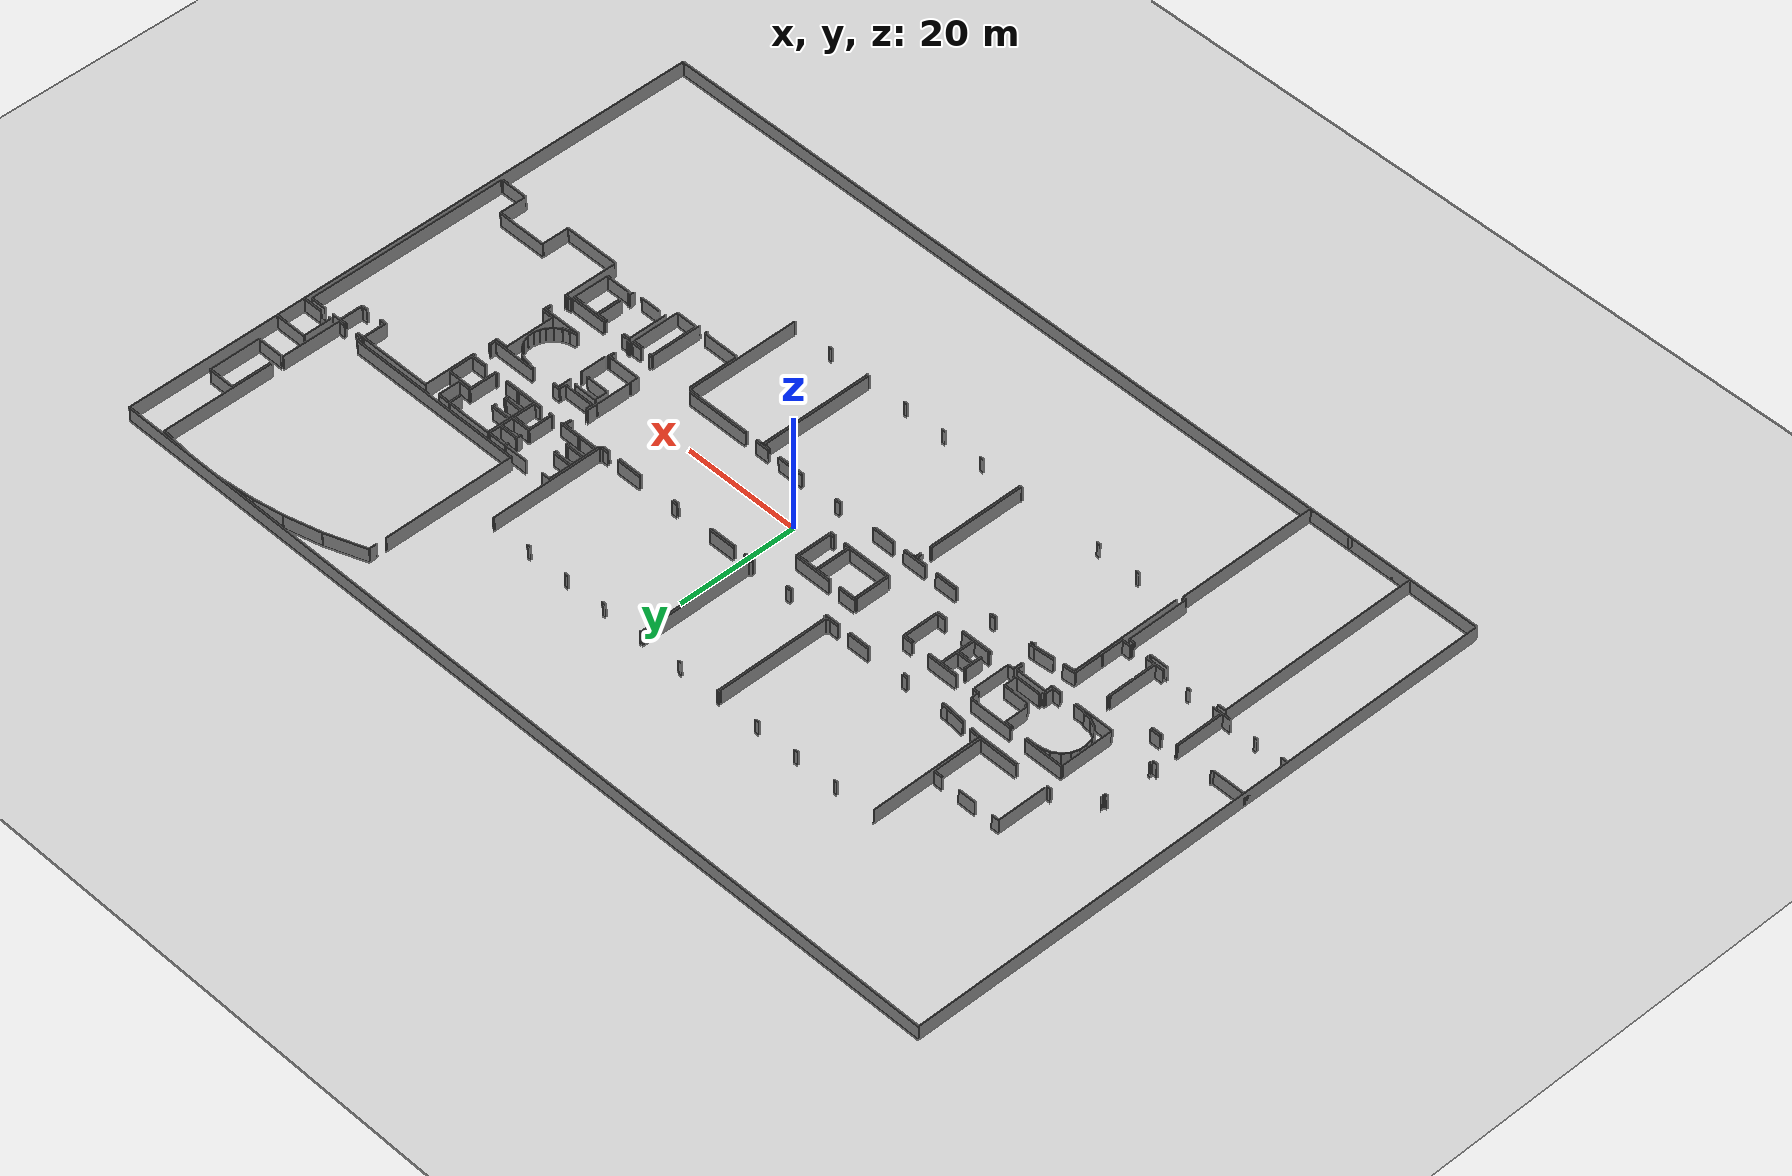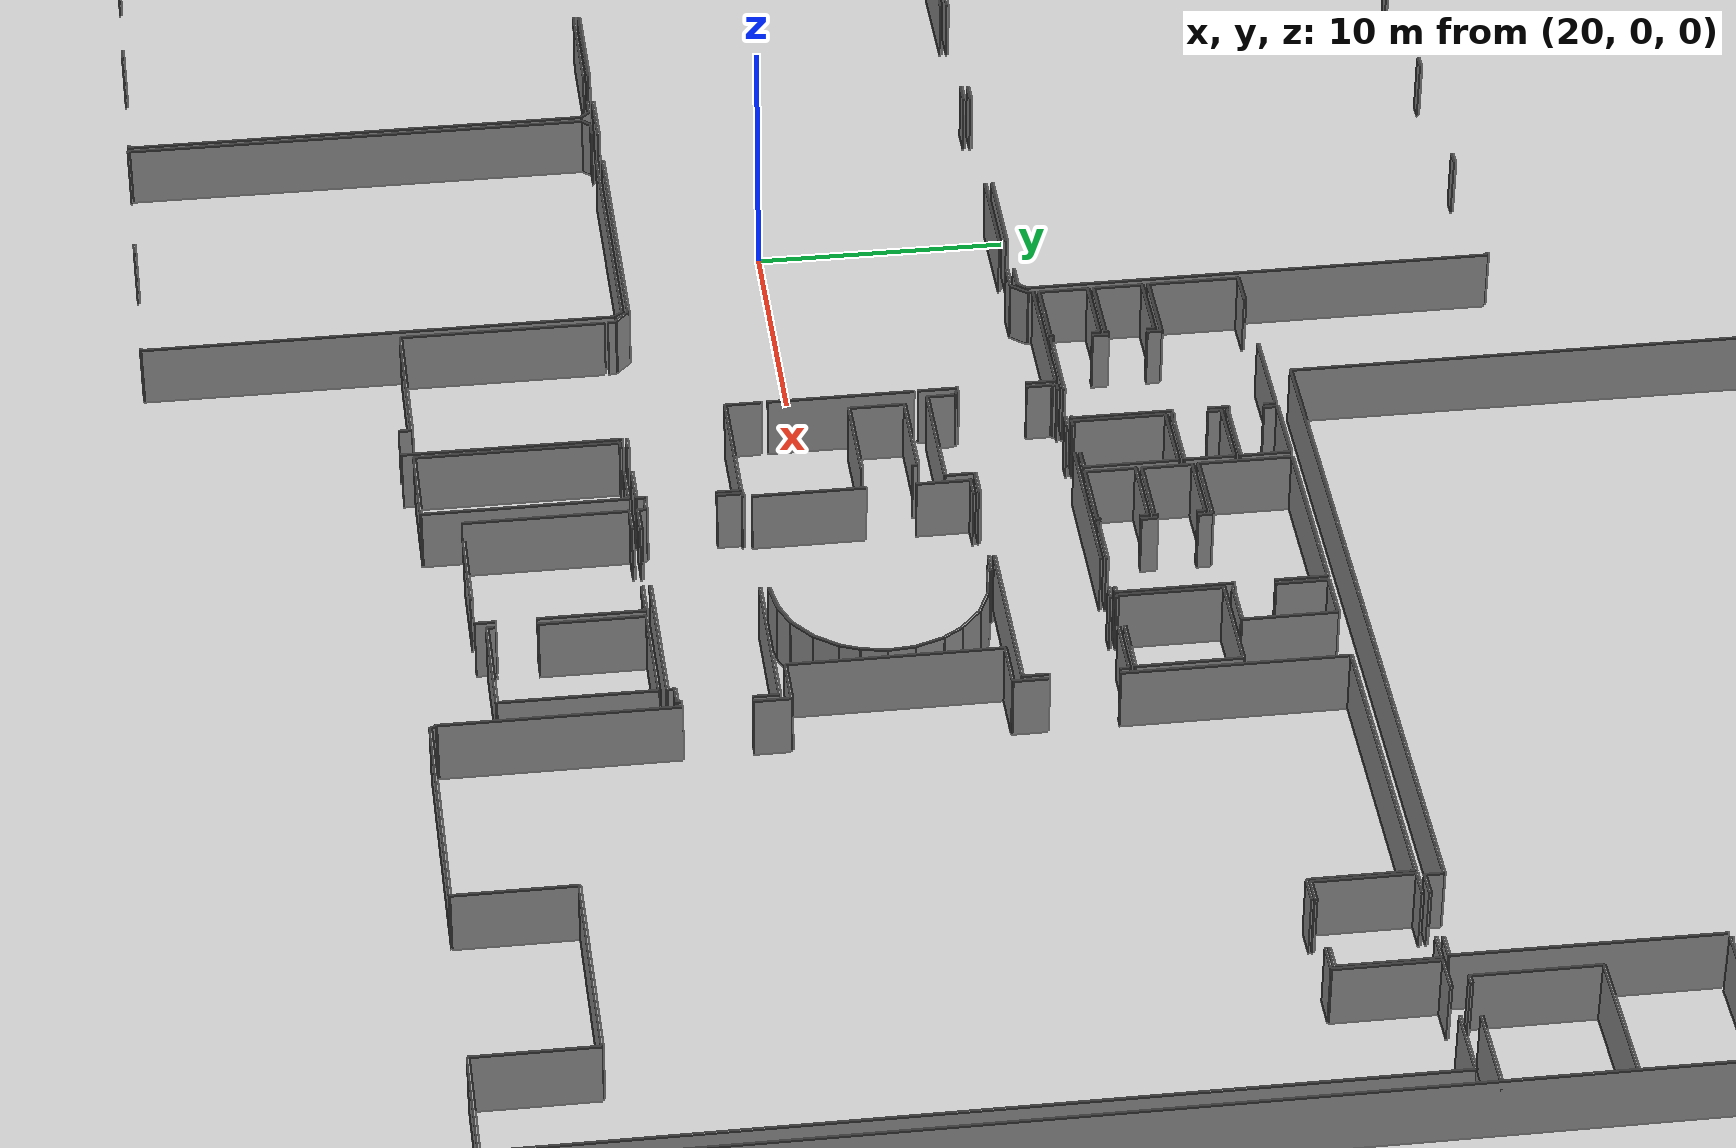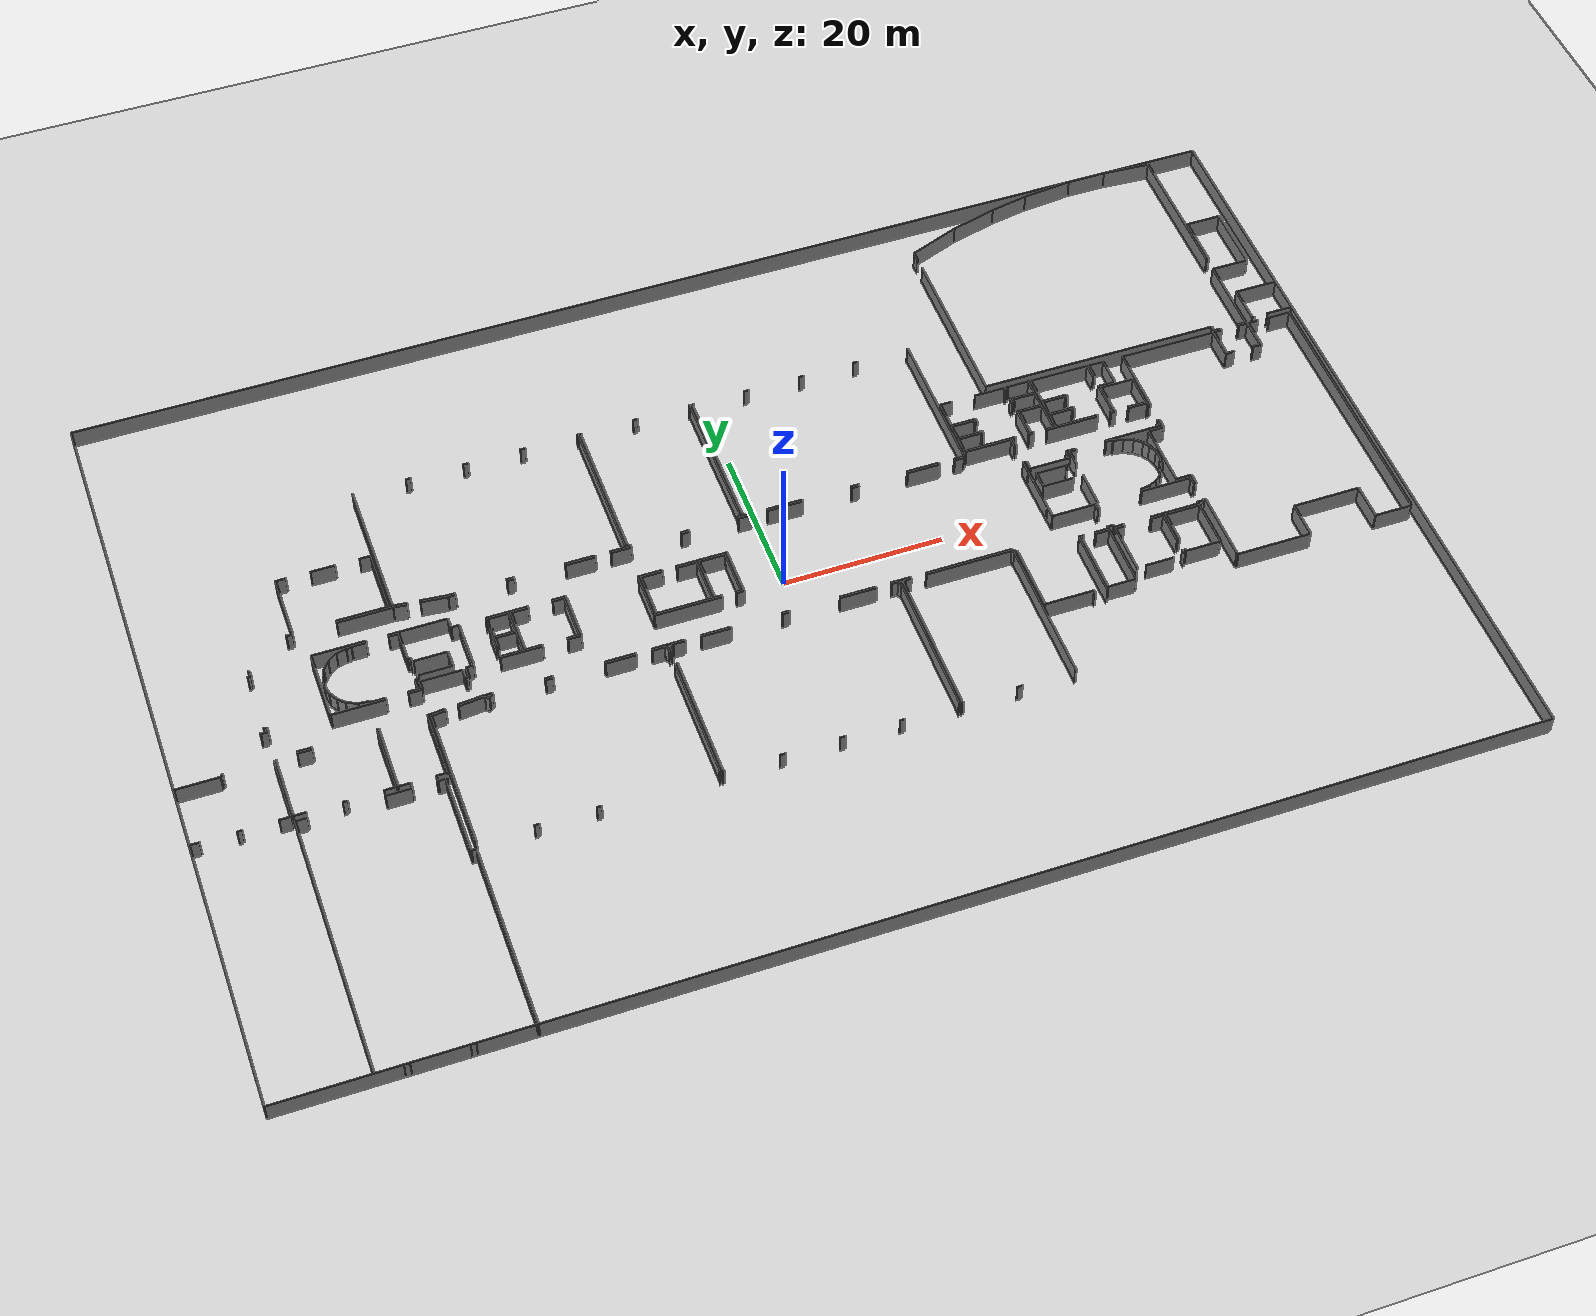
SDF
<sdf version="1.6">
  <world name="default">
    <light name="sun" type="directional">
      <cast_shadows>1</cast_shadows>
      <pose frame="">0 0 10 0 -0 0</pose>
      <diffuse>0.8 0.8 0.8 1</diffuse>
      <specular>0.1 0.1 0.1 1</specular>
      <attenuation>
        <range>1000</range>
        <constant>0.9</constant>
        <linear>0.01</linear>
        <quadratic>0.001</quadratic>
      </attenuation>
      <direction>-0.5 0.5 -1</direction>
    </light>
    <model name="ground_plane">
      <static>1</static>
      <link name="link">
        <collision name="collision">
          <geometry>
            <plane>
              <normal>0 0 1</normal>
              <size>100 100</size>
            </plane>
          </geometry>
          <surface>
            <friction>
              <ode>
                <mu>100</mu>
                <mu2>50</mu2>
              </ode>
              <torsional>
                <ode />
              </torsional>
            </friction>
            <contact>
              <ode />
            </contact>
            <bounce />
          </surface>
          <max_contacts>10</max_contacts>
        </collision>
        <visual name="visual">
          <cast_shadows>0</cast_shadows>
          <geometry>
            <plane>
              <normal>0 0 1</normal>
              <size>100 100</size>
            </plane>
          </geometry>
          <material>
            <script>
              <uri>file://media/materials/scripts/gazebo.material</uri>
              <name>Gazebo/Grey</name>
            </script>
          </material>
        </visual>
        <self_collide>0</self_collide>
        <kinematic>0</kinematic>
        <gravity>1</gravity>
      </link>
    </model>
    <gravity>0 0 -9.8</gravity>
    <magnetic_field>6e-06 2.3e-05 -4.2e-05</magnetic_field>
    <atmosphere type="adiabatic" />
    <physics default="0" name="default_physics" type="ode">
      <max_step_size>0.001</max_step_size>
      <real_time_factor>1</real_time_factor>
      <real_time_update_rate>1000</real_time_update_rate>
    </physics>
    <scene>
      <ambient>0.4 0.4 0.4 1</ambient>
      <background>0.7 0.7 0.7 1</background>
      <shadows>1</shadows>
    </scene>
    <spherical_coordinates>
      <surface_model>EARTH_WGS84</surface_model>
      <latitude_deg>0</latitude_deg>
      <longitude_deg>0</longitude_deg>
      <elevation>0</elevation>
      <heading_deg>0</heading_deg>
    </spherical_coordinates>
  <model name="0510032218_A-40">
		<static>1</static>
		<link name="Wall_0">
			<collision name="Wall_0_Collision">
				<geometry>
					<box>
						<size>6.36778472376 0.1 2.5</size>
					</box>
				</geometry>
				<pose frame="">3.18389236188 0 1.25 0 0 0</pose>
			</collision>
			<visual name="Wall_0_Visual">
				<pose frame="">3.18389236188 0 1.25 0 0 0</pose>
				<geometry>
					<box>
						<size>6.36778472376 0.1 2.5</size>
					</box>
				</geometry>
				<material>
					<script>
						<uri>file://media/materials/scripts/gazebo.material</uri>
						<name>Gazebo/Grey</name>
					</script>
					<ambient>1 1 1 1</ambient>
				</material>
			</visual>
			<pose frame="">29.4983911402 -39.4225875036 0 0 0 3.14159265359</pose>
		</link>
		<link name="Wall_1">
			<collision name="Wall_1_Collision">
				<geometry>
					<box>
						<size>8.17681591724 0.1 2.5</size>
					</box>
				</geometry>
				<pose frame="">4.08840795862 0 1.25 0 0 0</pose>
			</collision>
			<visual name="Wall_1_Visual">
				<pose frame="">4.08840795862 0 1.25 0 0 0</pose>
				<geometry>
					<box>
						<size>8.17681591724 0.1 2.5</size>
					</box>
				</geometry>
				<material>
					<script>
						<uri>file://media/materials/scripts/gazebo.material</uri>
						<name>Gazebo/Grey</name>
					</script>
					<ambient>1 1 1 1</ambient>
				</material>
			</visual>
			<pose frame="">17.9029226034 -39.4225875036 0 0 0 1.57079632679</pose>
		</link>
		<link name="Wall_2">
			<collision name="Wall_2_Collision">
				<geometry>
					<box>
						<size>1.27655253387 0.1 2.5</size>
					</box>
				</geometry>
				<pose frame="">0.638276266937 0 1.25 0 0 0</pose>
			</collision>
			<visual name="Wall_2_Visual">
				<pose frame="">0.638276266937 0 1.25 0 0 0</pose>
				<geometry>
					<box>
						<size>1.27655253387 0.1 2.5</size>
					</box>
				</geometry>
				<material>
					<script>
						<uri>file://media/materials/scripts/gazebo.material</uri>
						<name>Gazebo/Grey</name>
					</script>
					<ambient>1 1 1 1</ambient>
				</material>
			</visual>
			<pose frame="">17.9029226034 -31.2457715863 0 0 0 0.0</pose>
		</link>
		<link name="Wall_3">
			<collision name="Wall_3_Collision">
				<geometry>
					<box>
						<size>3.0208485387 0.1 2.5</size>
					</box>
				</geometry>
				<pose frame="">1.51042426935 0 1.25 0 0 0</pose>
			</collision>
			<visual name="Wall_3_Visual">
				<pose frame="">1.51042426935 0 1.25 0 0 0</pose>
				<geometry>
					<box>
						<size>3.0208485387 0.1 2.5</size>
					</box>
				</geometry>
				<material>
					<script>
						<uri>file://media/materials/scripts/gazebo.material</uri>
						<name>Gazebo/Grey</name>
					</script>
					<ambient>1 1 1 1</ambient>
				</material>
			</visual>
			<pose frame="">22.1080442992 -31.2457715863 0 0 0 0.0</pose>
		</link>
		<link name="Wall_4">
			<collision name="Wall_4_Collision">
				<geometry>
					<box>
						<size>1.42328562815 0.1 2.5</size>
					</box>
				</geometry>
				<pose frame="">0.711642814077 0 1.25 0 0 0</pose>
			</collision>
			<visual name="Wall_4_Visual">
				<pose frame="">0.711642814077 0 1.25 0 0 0</pose>
				<geometry>
					<box>
						<size>1.42328562815 0.1 2.5</size>
					</box>
				</geometry>
				<material>
					<script>
						<uri>file://media/materials/scripts/gazebo.material</uri>
						<name>Gazebo/Grey</name>
					</script>
					<ambient>1 1 1 1</ambient>
				</material>
			</visual>
			<pose frame="">28.0666010853 -31.2457715863 0 0 0 0.0</pose>
		</link>
		<link name="Wall_5">
			<collision name="Wall_5_Collision">
				<geometry>
					<box>
						<size>8.17682033982 0.1 2.5</size>
					</box>
				</geometry>
				<pose frame="">4.08841016991 0 1.25 0 0 0</pose>
			</collision>
			<visual name="Wall_5_Visual">
				<pose frame="">4.08841016991 0 1.25 0 0 0</pose>
				<geometry>
					<box>
						<size>8.17682033982 0.1 2.5</size>
					</box>
				</geometry>
				<material>
					<script>
						<uri>file://media/materials/scripts/gazebo.material</uri>
						<name>Gazebo/Grey</name>
					</script>
					<ambient>1 1 1 1</ambient>
				</material>
			</visual>
			<pose frame="">29.4898867134 -31.2457715863 0 0 0 -1.56975626135</pose>
		</link>
		<link name="Wall_6">
			<collision name="Wall_6_Collision">
				<geometry>
					<box>
						<size>0.0691777996382 0.1 2.5</size>
					</box>
				</geometry>
				<pose frame="">0.0345888998191 0 1.25 0 0 0</pose>
			</collision>
			<visual name="Wall_6_Visual">
				<pose frame="">0.0345888998191 0 1.25 0 0 0</pose>
				<geometry>
					<box>
						<size>0.0691777996382 0.1 2.5</size>
					</box>
				</geometry>
				<material>
					<script>
						<uri>file://media/materials/scripts/gazebo.material</uri>
						<name>Gazebo/Grey</name>
					</script>
					<ambient>1 1 1 1</ambient>
				</material>
			</visual>
			<pose frame="">11.902605274 -43.4868149653 0 0 0 1.57079632679</pose>
		</link>
		<link name="Wall_7">
			<collision name="Wall_7_Collision">
				<geometry>
					<box>
						<size>0.183405167647 0.1 2.5</size>
					</box>
				</geometry>
				<pose frame="">0.0917025838233 0 1.25 0 0 0</pose>
			</collision>
			<visual name="Wall_7_Visual">
				<pose frame="">0.0917025838233 0 1.25 0 0 0</pose>
				<geometry>
					<box>
						<size>0.183405167647 0.1 2.5</size>
					</box>
				</geometry>
				<material>
					<script>
						<uri>file://media/materials/scripts/gazebo.material</uri>
						<name>Gazebo/Grey</name>
					</script>
					<ambient>1 1 1 1</ambient>
				</material>
			</visual>
			<pose frame="">11.902605274 -43.4176371656 0 0 0 2.39339573267</pose>
		</link>
		<link name="Wall_8">
			<collision name="Wall_8_Collision">
				<geometry>
					<box>
						<size>0.176562053756 0.1 2.5</size>
					</box>
				</geometry>
				<pose frame="">0.0882810268778 0 1.25 0 0 0</pose>
			</collision>
			<visual name="Wall_8_Visual">
				<pose frame="">0.0882810268778 0 1.25 0 0 0</pose>
				<geometry>
					<box>
						<size>0.176562053756 0.1 2.5</size>
					</box>
				</geometry>
				<material>
					<script>
						<uri>file://media/materials/scripts/gazebo.material</uri>
						<name>Gazebo/Grey</name>
					</script>
					<ambient>1 1 1 1</ambient>
				</material>
			</visual>
			<pose frame="">17.1399358995 -39.5501539047 0 0 0 -1.57079632679</pose>
		</link>
		<link name="Wall_9">
			<collision name="Wall_9_Collision">
				<geometry>
					<box>
						<size>0.744454669501 0.1 2.5</size>
					</box>
				</geometry>
				<pose frame="">0.372227334751 0 1.25 0 0 0</pose>
			</collision>
			<visual name="Wall_9_Visual">
				<pose frame="">0.372227334751 0 1.25 0 0 0</pose>
				<geometry>
					<box>
						<size>0.744454669501 0.1 2.5</size>
					</box>
				</geometry>
				<material>
					<script>
						<uri>file://media/materials/scripts/gazebo.material</uri>
						<name>Gazebo/Grey</name>
					</script>
					<ambient>1 1 1 1</ambient>
				</material>
			</visual>
			<pose frame="">17.1399358995 -39.7267159585 0 0 0 0.0</pose>
		</link>
		<link name="Wall_10">
			<collision name="Wall_10_Collision">
				<geometry>
					<box>
						<size>6.75683051439 0.1 2.5</size>
					</box>
				</geometry>
				<pose frame="">3.3784152572 0 1.25 0 0 0</pose>
			</collision>
			<visual name="Wall_10_Visual">
				<pose frame="">3.3784152572 0 1.25 0 0 0</pose>
				<geometry>
					<box>
						<size>6.75683051439 0.1 2.5</size>
					</box>
				</geometry>
				<material>
					<script>
						<uri>file://media/materials/scripts/gazebo.material</uri>
						<name>Gazebo/Grey</name>
					</script>
					<ambient>1 1 1 1</ambient>
				</material>
			</visual>
			<pose frame="">23.1224827849 -39.7267159585 0 0 0 0.0</pose>
		</link>
		<link name="Wall_11">
			<collision name="Wall_11_Collision">
				<geometry>
					<box>
						<size>1.70718420619 0.1 2.5</size>
					</box>
				</geometry>
				<pose frame="">0.853592103096 0 1.25 0 0 0</pose>
			</collision>
			<visual name="Wall_11_Visual">
				<pose frame="">0.853592103096 0 1.25 0 0 0</pose>
				<geometry>
					<box>
						<size>1.70718420619 0.1 2.5</size>
					</box>
				</geometry>
				<material>
					<script>
						<uri>file://media/materials/scripts/gazebo.material</uri>
						<name>Gazebo/Grey</name>
					</script>
					<ambient>1 1 1 1</ambient>
				</material>
			</visual>
			<pose frame="">29.8793132993 -39.7267159585 0 0 0 -0.0988252515651</pose>
		</link>
		<link name="Wall_12">
			<collision name="Wall_12_Collision">
				<geometry>
					<box>
						<size>3.27533991613 0.1 2.5</size>
					</box>
				</geometry>
				<pose frame="">1.63766995807 0 1.25 0 0 0</pose>
			</collision>
			<visual name="Wall_12_Visual">
				<pose frame="">1.63766995807 0 1.25 0 0 0</pose>
				<geometry>
					<box>
						<size>3.27533991613 0.1 2.5</size>
					</box>
				</geometry>
				<material>
					<script>
						<uri>file://media/materials/scripts/gazebo.material</uri>
						<name>Gazebo/Grey</name>
					</script>
					<ambient>1 1 1 1</ambient>
				</material>
			</visual>
			<pose frame="">33.1113762574 -40.0347792974 0 0 0 -0.0931825737967</pose>
		</link>
		<link name="Wall_13">
			<collision name="Wall_13_Collision">
				<geometry>
					<box>
						<size>0.943102846444 0.1 2.5</size>
					</box>
				</geometry>
				<pose frame="">0.471551423222 0 1.25 0 0 0</pose>
			</collision>
			<visual name="Wall_13_Visual">
				<pose frame="">0.471551423222 0 1.25 0 0 0</pose>
				<geometry>
					<box>
						<size>0.943102846444 0.1 2.5</size>
					</box>
				</geometry>
				<material>
					<script>
						<uri>file://media/materials/scripts/gazebo.material</uri>
						<name>Gazebo/Grey</name>
					</script>
					<ambient>1 1 1 1</ambient>
				</material>
			</visual>
			<pose frame="">36.3725065846 -40.3395424111 0 0 0 0.0</pose>
		</link>
		<link name="Wall_14">
			<collision name="Wall_14_Collision">
				<geometry>
					<box>
						<size>0.940691143338 0.1 2.5</size>
					</box>
				</geometry>
				<pose frame="">0.470345571669 0 1.25 0 0 0</pose>
			</collision>
			<visual name="Wall_14_Visual">
				<pose frame="">0.470345571669 0 1.25 0 0 0</pose>
				<geometry>
					<box>
						<size>0.940691143338 0.1 2.5</size>
					</box>
				</geometry>
				<material>
					<script>
						<uri>file://media/materials/scripts/gazebo.material</uri>
						<name>Gazebo/Grey</name>
					</script>
					<ambient>1 1 1 1</ambient>
				</material>
			</visual>
			<pose frame="">43.5658553613 -40.3395424111 0 0 0 0.0</pose>
		</link>
		<link name="Wall_15">
			<collision name="Wall_15_Collision">
				<geometry>
					<box>
						<size>3.72303493796 0.1 2.5</size>
					</box>
				</geometry>
				<pose frame="">1.86151746898 0 1.25 0 0 0</pose>
			</collision>
			<visual name="Wall_15_Visual">
				<pose frame="">1.86151746898 0 1.25 0 0 0</pose>
				<geometry>
					<box>
						<size>3.72303493796 0.1 2.5</size>
					</box>
				</geometry>
				<material>
					<script>
						<uri>file://media/materials/scripts/gazebo.material</uri>
						<name>Gazebo/Grey</name>
					</script>
					<ambient>1 1 1 1</ambient>
				</material>
			</visual>
			<pose frame="">50.7551423222 -40.3395424111 0 0 0 0.0</pose>
		</link>
		<link name="Wall_16">
			<collision name="Wall_16_Collision">
				<geometry>
					<box>
						<size>2.55412052169 0.1 2.5</size>
					</box>
				</geometry>
				<pose frame="">1.27706026084 0 1.25 0 0 0</pose>
			</collision>
			<visual name="Wall_16_Visual">
				<pose frame="">1.27706026084 0 1.25 0 0 0</pose>
				<geometry>
					<box>
						<size>2.55412052169 0.1 2.5</size>
					</box>
				</geometry>
				<material>
					<script>
						<uri>file://media/materials/scripts/gazebo.material</uri>
						<name>Gazebo/Grey</name>
					</script>
					<ambient>1 1 1 1</ambient>
				</material>
			</visual>
			<pose frame="">56.3851997588 -40.3395424111 0 0 0 0.0</pose>
		</link>
		<link name="Wall_17">
			<collision name="Wall_17_Collision">
				<geometry>
					<box>
						<size>0.99819122267 0.1 2.5</size>
					</box>
				</geometry>
				<pose frame="">0.499095611335 0 1.25 0 0 0</pose>
			</collision>
			<visual name="Wall_17_Visual">
				<pose frame="">0.499095611335 0 1.25 0 0 0</pose>
				<geometry>
					<box>
						<size>0.99819122267 0.1 2.5</size>
					</box>
				</geometry>
				<material>
					<script>
						<uri>file://media/materials/scripts/gazebo.material</uri>
						<name>Gazebo/Grey</name>
					</script>
					<ambient>1 1 1 1</ambient>
				</material>
			</visual>
			<pose frame="">65.1226731825 -40.3395424111 0 0 0 0.0</pose>
		</link>
		<link name="Wall_18">
			<collision name="Wall_18_Collision">
				<geometry>
					<box>
						<size>1.7439152096 0.1 2.5</size>
					</box>
				</geometry>
				<pose frame="">0.871957604798 0 1.25 0 0 0</pose>
			</collision>
			<visual name="Wall_18_Visual">
				<pose frame="">0.871957604798 0 1.25 0 0 0</pose>
				<geometry>
					<box>
						<size>1.7439152096 0.1 2.5</size>
					</box>
				</geometry>
				<material>
					<script>
						<uri>file://media/materials/scripts/gazebo.material</uri>
						<name>Gazebo/Grey</name>
					</script>
					<ambient>1 1 1 1</ambient>
				</material>
			</visual>
			<pose frame="">72.3388696728 -40.3395424111 0 0 0 0.0</pose>
		</link>
		<link name="Wall_19">
			<collision name="Wall_19_Collision">
				<geometry>
					<box>
						<size>4.49249516073 0.1 2.5</size>
					</box>
				</geometry>
				<pose frame="">2.24624758036 0 1.25 0 0 0</pose>
			</collision>
			<visual name="Wall_19_Visual">
				<pose frame="">2.24624758036 0 1.25 0 0 0</pose>
				<geometry>
					<box>
						<size>4.49249516073 0.1 2.5</size>
					</box>
				</geometry>
				<material>
					<script>
						<uri>file://media/materials/scripts/gazebo.material</uri>
						<name>Gazebo/Grey</name>
					</script>
					<ambient>1 1 1 1</ambient>
				</material>
			</visual>
			<pose frame="">76.003135214 -40.3395424111 0 0 0 0.0</pose>
		</link>
		<link name="Wall_20">
			<collision name="Wall_20_Collision">
				<geometry>
					<box>
						<size>0.982324754863 0.1 2.5</size>
					</box>
				</geometry>
				<pose frame="">0.491162377432 0 1.25 0 0 0</pose>
			</collision>
			<visual name="Wall_20_Visual">
				<pose frame="">0.491162377432 0 1.25 0 0 0</pose>
				<geometry>
					<box>
						<size>0.982324754863 0.1 2.5</size>
					</box>
				</geometry>
				<material>
					<script>
						<uri>file://media/materials/scripts/gazebo.material</uri>
						<name>Gazebo/Grey</name>
					</script>
					<ambient>1 1 1 1</ambient>
				</material>
			</visual>
			<pose frame="">86.7097007584 -40.3395424111 0 0 0 0.0</pose>
		</link>
		<link name="Wall_21">
			<collision name="Wall_21_Collision">
				<geometry>
					<box>
						<size>4.19420556596 0.1 2.5</size>
					</box>
				</geometry>
				<pose frame="">2.09710278298 0 1.25 0 0 0</pose>
			</collision>
			<visual name="Wall_21_Visual">
				<pose frame="">2.09710278298 0 1.25 0 0 0</pose>
				<geometry>
					<box>
						<size>4.19420556596 0.1 2.5</size>
					</box>
				</geometry>
				<material>
					<script>
						<uri>file://media/materials/scripts/gazebo.material</uri>
						<name>Gazebo/Grey</name>
					</script>
					<ambient>1 1 1 1</ambient>
				</material>
			</visual>
			<pose frame="">93.9283089519 -40.3395424111 0 0 0 0.0</pose>
		</link>
		<link name="Wall_22">
			<collision name="Wall_22_Collision">
				<geometry>
					<box>
						<size>1.15507885634 0.1 2.5</size>
					</box>
				</geometry>
				<pose frame="">0.577539428172 0 1.25 0 0 0</pose>
			</collision>
			<visual name="Wall_22_Visual">
				<pose frame="">0.577539428172 0 1.25 0 0 0</pose>
				<geometry>
					<box>
						<size>1.15507885634 0.1 2.5</size>
					</box>
				</geometry>
				<material>
					<script>
						<uri>file://media/materials/scripts/gazebo.material</uri>
						<name>Gazebo/Grey</name>
					</script>
					<ambient>1 1 1 1</ambient>
				</material>
			</visual>
			<pose frame="">100.037025989 -40.3395424111 0 0 0 0.0</pose>
		</link>
		<link name="Wall_23">
			<collision name="Wall_23_Collision">
				<geometry>
					<box>
						<size>0.819658962709 0.1 2.5</size>
					</box>
				</geometry>
				<pose frame="">0.409829481354 0 1.25 0 0 0</pose>
			</collision>
			<visual name="Wall_23_Visual">
				<pose frame="">0.409829481354 0 1.25 0 0 0</pose>
				<geometry>
					<box>
						<size>0.819658962709 0.1 2.5</size>
					</box>
				</geometry>
				<material>
					<script>
						<uri>file://media/materials/scripts/gazebo.material</uri>
						<name>Gazebo/Grey</name>
					</script>
					<ambient>1 1 1 1</ambient>
				</material>
			</visual>
			<pose frame="">101.192104846 -40.3395424111 0 0 0 0.86267395989</pose>
		</link>
		<link name="Wall_24">
			<collision name="Wall_24_Collision">
				<geometry>
					<box>
						<size>0.203090787929 0.1 2.5</size>
					</box>
				</geometry>
				<pose frame="">0.101545393964 0 1.25 0 0 0</pose>
			</collision>
			<visual name="Wall_24_Visual">
				<pose frame="">0.101545393964 0 1.25 0 0 0</pose>
				<geometry>
					<box>
						<size>0.203090787929 0.1 2.5</size>
					</box>
				</geometry>
				<material>
					<script>
						<uri>file://media/materials/scripts/gazebo.material</uri>
						<name>Gazebo/Grey</name>
					</script>
					<ambient>1 1 1 1</ambient>
				</material>
			</visual>
			<pose frame="">101.725218164 -39.7169422143 0 0 0 1.57079632679</pose>
		</link>
		<link name="Wall_25">
			<collision name="Wall_25_Collision">
				<geometry>
					<box>
						<size>6.0408085552 0.1 2.5</size>
					</box>
				</geometry>
				<pose frame="">3.0204042776 0 1.25 0 0 0</pose>
			</collision>
			<visual name="Wall_25_Visual">
				<pose frame="">3.0204042776 0 1.25 0 0 0</pose>
				<geometry>
					<box>
						<size>6.0408085552 0.1 2.5</size>
					</box>
				</geometry>
				<material>
					<script>
						<uri>file://media/materials/scripts/gazebo.material</uri>
						<name>Gazebo/Grey</name>
					</script>
					<ambient>1 1 1 1</ambient>
				</material>
			</visual>
			<pose frame="">101.725218164 -39.5138514264 0 0 0 0.0</pose>
		</link>
		<link name="Wall_26">
			<collision name="Wall_26_Collision">
				<geometry>
					<box>
						<size>1.1684066893 0.1 2.5</size>
					</box>
				</geometry>
				<pose frame="">0.584203344651 0 1.25 0 0 0</pose>
			</collision>
			<visual name="Wall_26_Visual">
				<pose frame="">0.584203344651 0 1.25 0 0 0</pose>
				<geometry>
					<box>
						<size>1.1684066893 0.1 2.5</size>
					</box>
				</geometry>
				<material>
					<script>
						<uri>file://media/materials/scripts/gazebo.material</uri>
						<name>Gazebo/Grey</name>
					</script>
					<ambient>1 1 1 1</ambient>
				</material>
			</visual>
			<pose frame="">107.766026719 -39.5138514264 0 0 0 -1.57079632679</pose>
		</link>
		<link name="Wall_27">
			<collision name="Wall_27_Collision">
				<geometry>
					<box>
						<size>1.55922952432 0.1 2.5</size>
					</box>
				</geometry>
				<pose frame="">0.779614762162 0 1.25 0 0 0</pose>
			</collision>
			<visual name="Wall_27_Visual">
				<pose frame="">0.779614762162 0 1.25 0 0 0</pose>
				<geometry>
					<box>
						<size>1.55922952432 0.1 2.5</size>
					</box>
				</geometry>
				<material>
					<script>
						<uri>file://media/materials/scripts/gazebo.material</uri>
						<name>Gazebo/Grey</name>
					</script>
					<ambient>1 1 1 1</ambient>
				</material>
			</visual>
			<pose frame="">107.766026719 -43.3983435408 0 0 0 -1.57079632679</pose>
		</link>
		<link name="Wall_28">
			<collision name="Wall_28_Collision">
				<geometry>
					<box>
						<size>0.110430615936 0.1 2.5</size>
					</box>
				</geometry>
				<pose frame="">0.0552153079681 0 1.25 0 0 0</pose>
			</collision>
			<visual name="Wall_28_Visual">
				<pose frame="">0.0552153079681 0 1.25 0 0 0</pose>
				<geometry>
					<box>
						<size>0.110430615936 0.1 2.5</size>
					</box>
				</geometry>
				<material>
					<script>
						<uri>file://media/materials/scripts/gazebo.material</uri>
						<name>Gazebo/Grey</name>
					</script>
					<ambient>1 1 1 1</ambient>
				</material>
			</visual>
			<pose frame="">69.3035509155 -44.9575730651 0 0 0 1.57079632679</pose>
		</link>
		<link name="Wall_29">
			<collision name="Wall_29_Collision">
				<geometry>
					<box>
						<size>6.3024148764 0.1 2.5</size>
					</box>
				</geometry>
				<pose frame="">3.1512074382 0 1.25 0 0 0</pose>
			</collision>
			<visual name="Wall_29_Visual">
				<pose frame="">3.1512074382 0 1.25 0 0 0</pose>
				<geometry>
					<box>
						<size>6.3024148764 0.1 2.5</size>
					</box>
				</geometry>
				<material>
					<script>
						<uri>file://media/materials/scripts/gazebo.material</uri>
						<name>Gazebo/Grey</name>
					</script>
					<ambient>1 1 1 1</ambient>
				</material>
			</visual>
			<pose frame="">69.3035509155 -44.8471424491 0 0 0 3.14159265359</pose>
		</link>
		<link name="Wall_30">
			<collision name="Wall_30_Collision">
				<geometry>
					<box>
						<size>2.98023038111 0.1 2.5</size>
					</box>
				</geometry>
				<pose frame="">1.49011519056 0 1.25 0 0 0</pose>
			</collision>
			<visual name="Wall_30_Visual">
				<pose frame="">1.49011519056 0 1.25 0 0 0</pose>
				<geometry>
					<box>
						<size>2.98023038111 0.1 2.5</size>
					</box>
				</geometry>
				<material>
					<script>
						<uri>file://media/materials/scripts/gazebo.material</uri>
						<name>Gazebo/Grey</name>
					</script>
					<ambient>1 1 1 1</ambient>
				</material>
			</visual>
			<pose frame="">61.2461777679 -44.8471424491 0 0 0 3.14159265359</pose>
		</link>
		<link name="Wall_31">
			<collision name="Wall_31_Collision">
				<geometry>
					<box>
						<size>1.65772855647 0.1 2.5</size>
					</box>
				</geometry>
				<pose frame="">0.828864278234 0 1.25 0 0 0</pose>
			</collision>
			<visual name="Wall_31_Visual">
				<pose frame="">0.828864278234 0 1.25 0 0 0</pose>
				<geometry>
					<box>
						<size>1.65772855647 0.1 2.5</size>
					</box>
				</geometry>
				<material>
					<script>
						<uri>file://media/materials/scripts/gazebo.material</uri>
						<name>Gazebo/Grey</name>
					</script>
					<ambient>1 1 1 1</ambient>
				</material>
			</visual>
			<pose frame="">49.3807254149 -44.8471424491 0 0 0 3.14159265359</pose>
		</link>
		<link name="Wall_32">
			<collision name="Wall_32_Collision">
				<geometry>
					<box>
						<size>5.12372671596 0.1 2.5</size>
					</box>
				</geometry>
				<pose frame="">2.56186335798 0 1.25 0 0 0</pose>
			</collision>
			<visual name="Wall_32_Visual">
				<pose frame="">2.56186335798 0 1.25 0 0 0</pose>
				<geometry>
					<box>
						<size>5.12372671596 0.1 2.5</size>
					</box>
				</geometry>
				<material>
					<script>
						<uri>file://media/materials/scripts/gazebo.material</uri>
						<name>Gazebo/Grey</name>
					</script>
					<ambient>1 1 1 1</ambient>
				</material>
			</visual>
			<pose frame="">44.7388315933 -44.8471424491 0 0 0 3.14159265359</pose>
		</link>
		<link name="Wall_33">
			<collision name="Wall_33_Collision">
				<geometry>
					<box>
						<size>0.971789420239 0.1 2.5</size>
					</box>
				</geometry>
				<pose frame="">0.48589471012 0 1.25 0 0 0</pose>
			</collision>
			<visual name="Wall_33_Visual">
				<pose frame="">0.48589471012 0 1.25 0 0 0</pose>
				<geometry>
					<box>
						<size>0.971789420239 0.1 2.5</size>
					</box>
				</geometry>
				<material>
					<script>
						<uri>file://media/materials/scripts/gazebo.material</uri>
						<name>Gazebo/Grey</name>
					</script>
					<ambient>1 1 1 1</ambient>
				</material>
			</visual>
			<pose frame="">36.4382572272 -44.8471424491 0 0 0 3.14159265359</pose>
		</link>
		<link name="Wall_34">
			<collision name="Wall_34_Collision">
				<geometry>
					<box>
						<size>1.37771713261 0.1 2.5</size>
					</box>
				</geometry>
				<pose frame="">0.688858566306 0 1.25 0 0 0</pose>
			</collision>
			<visual name="Wall_34_Visual">
				<pose frame="">0.688858566306 0 1.25 0 0 0</pose>
				<geometry>
					<box>
						<size>1.37771713261 0.1 2.5</size>
					</box>
				</geometry>
				<material>
					<script>
						<uri>file://media/materials/scripts/gazebo.material</uri>
						<name>Gazebo/Grey</name>
					</script>
					<ambient>1 1 1 1</ambient>
				</material>
			</visual>
			<pose frame="">35.4664678069 -44.8471424491 0 0 0 1.57079632679</pose>
		</link>
		<link name="Wall_35">
			<collision name="Wall_35_Collision">
				<geometry>
					<box>
						<size>7.17532446927 0.1 2.5</size>
					</box>
				</geometry>
				<pose frame="">3.58766223463 0 1.25 0 0 0</pose>
			</collision>
			<visual name="Wall_35_Visual">
				<pose frame="">3.58766223463 0 1.25 0 0 0</pose>
				<geometry>
					<box>
						<size>7.17532446927 0.1 2.5</size>
					</box>
				</geometry>
				<material>
					<script>
						<uri>file://media/materials/scripts/gazebo.material</uri>
						<name>Gazebo/Grey</name>
					</script>
					<ambient>1 1 1 1</ambient>
				</material>
			</visual>
			<pose frame="">35.4664678069 -43.4694253165 0 0 0 3.14159265359</pose>
		</link>
		<link name="Wall_36">
			<collision name="Wall_36_Collision">
				<geometry>
					<box>
						<size>6.56239412535 0.1 2.5</size>
					</box>
				</geometry>
				<pose frame="">3.28119706268 0 1.25 0 0 0</pose>
			</collision>
			<visual name="Wall_36_Visual">
				<pose frame="">3.28119706268 0 1.25 0 0 0</pose>
				<geometry>
					<box>
						<size>6.56239412535 0.1 2.5</size>
					</box>
				</geometry>
				<material>
					<script>
						<uri>file://media/materials/scripts/gazebo.material</uri>
						<name>Gazebo/Grey</name>
					</script>
					<ambient>1 1 1 1</ambient>
				</material>
			</visual>
			<pose frame="">25.6754609209 -43.4694253165 0 0 0 -3.1389427565</pose>
		</link>
		<link name="Wall_37">
			<collision name="Wall_37_Collision">
				<geometry>
					<box>
						<size>1.5723034938 0.1 2.5</size>
					</box>
				</geometry>
				<pose frame="">0.786151746898 0 1.25 0 0 0</pose>
			</collision>
			<visual name="Wall_37_Visual">
				<pose frame="">0.786151746898 0 1.25 0 0 0</pose>
				<geometry>
					<box>
						<size>1.5723034938 0.1 2.5</size>
					</box>
				</geometry>
				<material>
					<script>
						<uri>file://media/materials/scripts/gazebo.material</uri>
						<name>Gazebo/Grey</name>
					</script>
					<ambient>1 1 1 1</ambient>
				</material>
			</visual>
			<pose frame="">57.930212928 -40.0724780249 0 0 0 3.14159265359</pose>
		</link>
		<link name="Wall_38">
			<collision name="Wall_38_Collision">
				<geometry>
					<box>
						<size>3.73585504395 0.1 2.5</size>
					</box>
				</geometry>
				<pose frame="">1.86792752198 0 1.25 0 0 0</pose>
			</collision>
			<visual name="Wall_38_Visual">
				<pose frame="">1.86792752198 0 1.25 0 0 0</pose>
				<geometry>
					<box>
						<size>3.73585504395 0.1 2.5</size>
					</box>
				</geometry>
				<material>
					<script>
						<uri>file://media/materials/scripts/gazebo.material</uri>
						<name>Gazebo/Grey</name>
					</script>
					<ambient>1 1 1 1</ambient>
				</material>
			</visual>
			<pose frame="">54.4800812363 -40.0724780249 0 0 0 3.14159265359</pose>
		</link>
		<link name="Wall_39">
			<collision name="Wall_39_Collision">
				<geometry>
					<box>
						<size>0.926474788183 0.1 2.5</size>
					</box>
				</geometry>
				<pose frame="">0.463237394091 0 1.25 0 0 0</pose>
			</collision>
			<visual name="Wall_39_Visual">
				<pose frame="">0.463237394091 0 1.25 0 0 0</pose>
				<geometry>
					<box>
						<size>0.926474788183 0.1 2.5</size>
					</box>
				</geometry>
				<material>
					<script>
						<uri>file://media/materials/scripts/gazebo.material</uri>
						<name>Gazebo/Grey</name>
					</script>
					<ambient>1 1 1 1</ambient>
				</material>
			</visual>
			<pose frame="">44.4848411767 -40.0724780249 0 0 0 3.14159265359</pose>
		</link>
		<link name="Wall_40">
			<collision name="Wall_40_Collision">
				<geometry>
					<box>
						<size>0.959730904706 0.1 2.5</size>
					</box>
				</geometry>
				<pose frame="">0.479865452353 0 1.25 0 0 0</pose>
			</collision>
			<visual name="Wall_40_Visual">
				<pose frame="">0.479865452353 0 1.25 0 0 0</pose>
				<geometry>
					<box>
						<size>0.959730904706 0.1 2.5</size>
					</box>
				</geometry>
				<material>
					<script>
						<uri>file://media/materials/scripts/gazebo.material</uri>
						<name>Gazebo/Grey</name>
					</script>
					<ambient>1 1 1 1</ambient>
				</material>
			</visual>
			<pose frame="">37.307231936 -40.0724780249 0 0 0 3.14159265359</pose>
		</link>
		<link name="Wall_41">
			<collision name="Wall_41_Collision">
				<geometry>
					<box>
						<size>3.22628318611 0.1 2.5</size>
					</box>
				</geometry>
				<pose frame="">1.61314159305 0 1.25 0 0 0</pose>
			</collision>
			<visual name="Wall_41_Visual">
				<pose frame="">1.61314159305 0 1.25 0 0 0</pose>
				<geometry>
					<box>
						<size>3.22628318611 0.1 2.5</size>
					</box>
				</geometry>
				<material>
					<script>
						<uri>file://media/materials/scripts/gazebo.material</uri>
						<name>Gazebo/Grey</name>
					</script>
					<ambient>1 1 1 1</ambient>
				</material>
			</visual>
			<pose frame="">36.3475010313 -40.0724780249 0 0 0 3.04022890168</pose>
		</link>
		<link name="Wall_42">
			<collision name="Wall_42_Collision">
				<geometry>
					<box>
						<size>1.73604413763 0.1 2.5</size>
					</box>
				</geometry>
				<pose frame="">0.868022068814 0 1.25 0 0 0</pose>
			</collision>
			<visual name="Wall_42_Visual">
				<pose frame="">0.868022068814 0 1.25 0 0 0</pose>
				<geometry>
					<box>
						<size>1.73604413763 0.1 2.5</size>
					</box>
				</geometry>
				<material>
					<script>
						<uri>file://media/materials/scripts/gazebo.material</uri>
						<name>Gazebo/Grey</name>
					</script>
					<ambient>1 1 1 1</ambient>
				</material>
			</visual>
			<pose frame="">31.6247516898 -39.6113350046 0 0 0 3.04110917137</pose>
		</link>
		<link name="Wall_43">
			<collision name="Wall_43_Collision">
				<geometry>
					<box>
						<size>18.4257925301 0.1 2.5</size>
					</box>
				</geometry>
				<pose frame="">9.21289626503 0 1.25 0 0 0</pose>
			</collision>
			<visual name="Wall_43_Visual">
				<pose frame="">9.21289626503 0 1.25 0 0 0</pose>
				<geometry>
					<box>
						<size>18.4257925301 0.1 2.5</size>
					</box>
				</geometry>
				<material>
					<script>
						<uri>file://media/materials/scripts/gazebo.material</uri>
						<name>Gazebo/Grey</name>
					</script>
					<ambient>1 1 1 1</ambient>
				</material>
			</visual>
			<pose frame="">29.8974645384 -39.437184654 0 0 0 1.57079632679</pose>
		</link>
		<link name="Wall_44">
			<collision name="Wall_44_Collision">
				<geometry>
					<box>
						<size>0.651540634024 0.1 2.5</size>
					</box>
				</geometry>
				<pose frame="">0.325770317012 0 1.25 0 0 0</pose>
			</collision>
			<visual name="Wall_44_Visual">
				<pose frame="">0.325770317012 0 1.25 0 0 0</pose>
				<geometry>
					<box>
						<size>0.651540634024 0.1 2.5</size>
					</box>
				</geometry>
				<material>
					<script>
						<uri>file://media/materials/scripts/gazebo.material</uri>
						<name>Gazebo/Grey</name>
					</script>
					<ambient>1 1 1 1</ambient>
				</material>
			</visual>
			<pose frame="">36.4941071939 -21.0113921239 0 0 0 0.0</pose>
		</link>
		<link name="Wall_45">
			<collision name="Wall_45_Collision">
				<geometry>
					<box>
						<size>0.659791197284 0.1 2.5</size>
					</box>
				</geometry>
				<pose frame="">0.329895598642 0 1.25 0 0 0</pose>
			</collision>
			<visual name="Wall_45_Visual">
				<pose frame="">0.329895598642 0 1.25 0 0 0</pose>
				<geometry>
					<box>
						<size>0.659791197284 0.1 2.5</size>
					</box>
				</geometry>
				<material>
					<script>
						<uri>file://media/materials/scripts/gazebo.material</uri>
						<name>Gazebo/Grey</name>
					</script>
					<ambient>1 1 1 1</ambient>
				</material>
			</visual>
			<pose frame="">43.6850442674 -21.0113921239 0 0 0 0.0</pose>
		</link>
		<link name="Wall_46">
			<collision name="Wall_46_Collision">
				<geometry>
					<box>
						<size>0.658521879859 0.1 2.5</size>
					</box>
				</geometry>
				<pose frame="">0.32926093993 0 1.25 0 0 0</pose>
			</collision>
			<visual name="Wall_46_Visual">
				<pose frame="">0.32926093993 0 1.25 0 0 0</pose>
				<geometry>
					<box>
						<size>0.658521879859 0.1 2.5</size>
					</box>
				</geometry>
				<material>
					<script>
						<uri>file://media/materials/scripts/gazebo.material</uri>
						<name>Gazebo/Grey</name>
					</script>
					<ambient>1 1 1 1</ambient>
				</material>
			</visual>
			<pose frame="">50.8959096246 -21.0113921239 0 0 0 0.0</pose>
		</link>
		<link name="Wall_47">
			<collision name="Wall_47_Collision">
				<geometry>
					<box>
						<size>0.220861231873 0.1 2.5</size>
					</box>
				</geometry>
				<pose frame="">0.110430615936 0 1.25 0 0 0</pose>
			</collision>
			<visual name="Wall_47_Visual">
				<pose frame="">0.110430615936 0 1.25 0 0 0</pose>
				<geometry>
					<box>
						<size>0.220861231873 0.1 2.5</size>
					</box>
				</geometry>
				<material>
					<script>
						<uri>file://media/materials/scripts/gazebo.material</uri>
						<name>Gazebo/Grey</name>
					</script>
					<ambient>1 1 1 1</ambient>
				</material>
			</visual>
			<pose frame="">58.0967473741 -21.0113921239 0 0 0 0.0</pose>
		</link>
		<link name="Wall_48">
			<collision name="Wall_48_Collision">
				<geometry>
					<box>
						<size>18.7206549678 0.1 2.5</size>
					</box>
				</geometry>
				<pose frame="">9.3603274839 0 1.25 0 0 0</pose>
			</collision>
			<visual name="Wall_48_Visual">
				<pose frame="">9.3603274839 0 1.25 0 0 0</pose>
				<geometry>
					<box>
						<size>18.7206549678 0.1 2.5</size>
					</box>
				</geometry>
				<material>
					<script>
						<uri>file://media/materials/scripts/gazebo.material</uri>
						<name>Gazebo/Grey</name>
					</script>
					<ambient>1 1 1 1</ambient>
				</material>
			</visual>
			<pose frame="">58.317608606 -21.0113921239 0 0 0 -1.57079632679</pose>
		</link>
		<link name="Wall_49">
			<collision name="Wall_49_Collision">
				<geometry>
					<box>
						<size>0.515721467109 0.1 2.5</size>
					</box>
				</geometry>
				<pose frame="">0.257860733555 0 1.25 0 0 0</pose>
			</collision>
			<visual name="Wall_49_Visual">
				<pose frame="">0.257860733555 0 1.25 0 0 0</pose>
				<geometry>
					<box>
						<size>0.515721467109 0.1 2.5</size>
					</box>
				</geometry>
				<material>
					<script>
						<uri>file://media/materials/scripts/gazebo.material</uri>
						<name>Gazebo/Grey</name>
					</script>
					<ambient>1 1 1 1</ambient>
				</material>
			</visual>
			<pose frame="">58.317608606 -39.7320470917 0 0 0 -2.42063253448</pose>
		</link>
		<link name="Wall_50">
			<collision name="Wall_50_Collision">
				<geometry>
					<box>
						<size>0.561299929679 0.1 2.5</size>
					</box>
				</geometry>
				<pose frame="">0.280649964839 0 1.25 0 0 0</pose>
			</collision>
			<visual name="Wall_50_Visual">
				<pose frame="">0.280649964839 0 1.25 0 0 0</pose>
				<geometry>
					<box>
						<size>0.561299929679 0.1 2.5</size>
					</box>
				</geometry>
				<material>
					<script>
						<uri>file://media/materials/scripts/gazebo.material</uri>
						<name>Gazebo/Grey</name>
					</script>
					<ambient>1 1 1 1</ambient>
				</material>
			</visual>
			<pose frame="">72.7282962587 -39.722019484 0 0 0 -2.46755805064</pose>
		</link>
		<link name="Wall_51">
			<collision name="Wall_51_Collision">
				<geometry>
					<box>
						<size>0.993367816457 0.1 2.5</size>
					</box>
				</geometry>
				<pose frame="">0.496683908228 0 1.25 0 0 0</pose>
			</collision>
			<visual name="Wall_51_Visual">
				<pose frame="">0.496683908228 0 1.25 0 0 0</pose>
				<geometry>
					<box>
						<size>0.993367816457 0.1 2.5</size>
					</box>
				</geometry>
				<material>
					<script>
						<uri>file://media/materials/scripts/gazebo.material</uri>
						<name>Gazebo/Grey</name>
					</script>
					<ambient>1 1 1 1</ambient>
				</material>
			</visual>
			<pose frame="">66.1246723574 -40.0723510932 0 0 0 3.14159265359</pose>
		</link>
		<link name="Wall_52">
			<collision name="Wall_52_Collision">
				<geometry>
					<box>
						<size>0.511678212058 0.1 2.5</size>
					</box>
				</geometry>
				<pose frame="">0.255839106029 0 1.25 0 0 0</pose>
			</collision>
			<visual name="Wall_52_Visual">
				<pose frame="">0.255839106029 0 1.25 0 0 0</pose>
				<geometry>
					<box>
						<size>0.511678212058 0.1 2.5</size>
					</box>
				</geometry>
				<material>
					<script>
						<uri>file://media/materials/scripts/gazebo.material</uri>
						<name>Gazebo/Grey</name>
					</script>
					<ambient>1 1 1 1</ambient>
				</material>
			</visual>
			<pose frame="">58.9238346079 -40.0723510932 0 0 0 2.37373655025</pose>
		</link>
		<link name="Wall_53">
			<collision name="Wall_53_Collision">
				<geometry>
					<box>
						<size>18.7103734967 0.1 2.5</size>
					</box>
				</geometry>
				<pose frame="">9.35518674833 0 1.25 0 0 0</pose>
			</collision>
			<visual name="Wall_53_Visual">
				<pose frame="">9.35518674833 0 1.25 0 0 0</pose>
				<geometry>
					<box>
						<size>18.7103734967 0.1 2.5</size>
					</box>
				</geometry>
				<material>
					<script>
						<uri>file://media/materials/scripts/gazebo.material</uri>
						<name>Gazebo/Grey</name>
					</script>
					<ambient>1 1 1 1</ambient>
				</material>
			</visual>
			<pose frame="">58.5557325548 -39.7169422143 0 0 0 1.57079632679</pose>
		</link>
		<link name="Wall_54">
			<collision name="Wall_54_Collision">
				<geometry>
					<box>
						<size>0.203598514899 0.1 2.5</size>
					</box>
				</geometry>
				<pose frame="">0.101799257449 0 1.25 0 0 0</pose>
			</collision>
			<visual name="Wall_54_Visual">
				<pose frame="">0.101799257449 0 1.25 0 0 0</pose>
				<geometry>
					<box>
						<size>0.203598514899 0.1 2.5</size>
					</box>
				</geometry>
				<material>
					<script>
						<uri>file://media/materials/scripts/gazebo.material</uri>
						<name>Gazebo/Grey</name>
					</script>
					<ambient>1 1 1 1</ambient>
				</material>
			</visual>
			<pose frame="">58.5557325548 -21.0065687177 0 0 0 0.0</pose>
		</link>
		<link name="Wall_55">
			<collision name="Wall_55_Collision">
				<geometry>
					<box>
						<size>0.648875067432 0.1 2.5</size>
					</box>
				</geometry>
				<pose frame="">0.324437533716 0 1.25 0 0 0</pose>
			</collision>
			<visual name="Wall_55_Visual">
				<pose frame="">0.324437533716 0 1.25 0 0 0</pose>
				<geometry>
					<box>
						<size>0.648875067432 0.1 2.5</size>
					</box>
				</geometry>
				<material>
					<script>
						<uri>file://media/materials/scripts/gazebo.material</uri>
						<name>Gazebo/Grey</name>
					</script>
					<ambient>1 1 1 1</ambient>
				</material>
			</visual>
			<pose frame="">65.2859074033 -21.0065687177 0 0 0 0.0</pose>
		</link>
		<link name="Wall_56">
			<collision name="Wall_56_Collision">
				<geometry>
					<box>
						<size>0.195094088154 0.1 2.5</size>
					</box>
				</geometry>
				<pose frame="">0.097547044077 0 1.25 0 0 0</pose>
			</collision>
			<visual name="Wall_56_Visual">
				<pose frame="">0.097547044077 0 1.25 0 0 0</pose>
				<geometry>
					<box>
						<size>0.195094088154 0.1 2.5</size>
					</box>
				</geometry>
				<material>
					<script>
						<uri>file://media/materials/scripts/gazebo.material</uri>
						<name>Gazebo/Grey</name>
					</script>
					<ambient>1 1 1 1</ambient>
				</material>
			</visual>
			<pose frame="">72.4778599308 -21.0065687177 0 0 0 0.0</pose>
		</link>
		<link name="Wall_57">
			<collision name="Wall_57_Collision">
				<geometry>
					<box>
						<size>18.7155325906 0.1 2.5</size>
					</box>
				</geometry>
				<pose frame="">9.35776629532 0 1.25 0 0 0</pose>
			</collision>
			<visual name="Wall_57_Visual">
				<pose frame="">9.35776629532 0 1.25 0 0 0</pose>
				<geometry>
					<box>
						<size>18.7155325906 0.1 2.5</size>
					</box>
				</geometry>
				<material>
					<script>
						<uri>file://media/materials/scripts/gazebo.material</uri>
						<name>Gazebo/Grey</name>
					</script>
					<ambient>1 1 1 1</ambient>
				</material>
			</visual>
			<pose frame="">72.672954019 -21.0065687177 0 0 0 -1.56783930059</pose>
		</link>
		<link name="Wall_58">
			<collision name="Wall_58_Collision">
				<geometry>
					<box>
						<size>0.425149207355 0.1 2.5</size>
					</box>
				</geometry>
				<pose frame="">0.212574603678 0 1.25 0 0 0</pose>
			</collision>
			<visual name="Wall_58_Visual">
				<pose frame="">0.212574603678 0 1.25 0 0 0</pose>
				<geometry>
					<box>
						<size>0.425149207355 0.1 2.5</size>
					</box>
				</geometry>
				<material>
					<script>
						<uri>file://media/materials/scripts/gazebo.material</uri>
						<name>Gazebo/Grey</name>
					</script>
					<ambient>1 1 1 1</ambient>
				</material>
			</visual>
			<pose frame="">101.404334719 -39.7554025323 0 0 0 -2.3285352311</pose>
		</link>
		<link name="Wall_59">
			<collision name="Wall_59_Collision">
				<geometry>
					<box>
						<size>1.0598800495 0.1 2.5</size>
					</box>
				</geometry>
				<pose frame="">0.529940024752 0 1.25 0 0 0</pose>
			</collision>
			<visual name="Wall_59_Visual">
				<pose frame="">0.529940024752 0 1.25 0 0 0</pose>
				<geometry>
					<box>
						<size>1.0598800495 0.1 2.5</size>
					</box>
				</geometry>
				<material>
					<script>
						<uri>file://media/materials/scripts/gazebo.material</uri>
						<name>Gazebo/Grey</name>
					</script>
					<ambient>1 1 1 1</ambient>
				</material>
			</visual>
			<pose frame="">101.112137848 -40.0642274617 0 0 0 3.14159265359</pose>
		</link>
		<link name="Wall_60">
			<collision name="Wall_60_Collision">
				<geometry>
					<box>
						<size>4.20918351157 0.1 2.5</size>
					</box>
				</geometry>
				<pose frame="">2.10459175578 0 1.25 0 0 0</pose>
			</collision>
			<visual name="Wall_60_Visual">
				<pose frame="">2.10459175578 0 1.25 0 0 0</pose>
				<geometry>
					<box>
						<size>4.20918351157 0.1 2.5</size>
					</box>
				</geometry>
				<material>
					<script>
						<uri>file://media/materials/scripts/gazebo.material</uri>
						<name>Gazebo/Grey</name>
					</script>
					<ambient>1 1 1 1</ambient>
				</material>
			</visual>
			<pose frame="">98.1280995145 -40.0642274617 0 0 0 3.14159265359</pose>
		</link>
		<link name="Wall_61">
			<collision name="Wall_61_Collision">
				<geometry>
					<box>
						<size>1.0078380351 0.1 2.5</size>
					</box>
				</geometry>
				<pose frame="">0.503919017548 0 1.25 0 0 0</pose>
			</collision>
			<visual name="Wall_61_Visual">
				<pose frame="">0.503919017548 0 1.25 0 0 0</pose>
				<geometry>
					<box>
						<size>1.0078380351 0.1 2.5</size>
					</box>
				</geometry>
				<material>
					<script>
						<uri>file://media/materials/scripts/gazebo.material</uri>
						<name>Gazebo/Grey</name>
					</script>
					<ambient>1 1 1 1</ambient>
				</material>
			</visual>
			<pose frame="">87.7353092375 -40.0642274617 0 0 0 3.14159265359</pose>
		</link>
		<link name="Wall_62">
			<collision name="Wall_62_Collision">
				<geometry>
					<box>
						<size>4.51102719513 0.1 2.5</size>
					</box>
				</geometry>
				<pose frame="">2.25551359756 0 1.25 0 0 0</pose>
			</collision>
			<visual name="Wall_62_Visual">
				<pose frame="">2.25551359756 0 1.25 0 0 0</pose>
				<geometry>
					<box>
						<size>4.51102719513 0.1 2.5</size>
					</box>
				</geometry>
				<material>
					<script>
						<uri>file://media/materials/scripts/gazebo.material</uri>
						<name>Gazebo/Grey</name>
					</script>
					<ambient>1 1 1 1</ambient>
				</material>
			</visual>
			<pose frame="">80.4985498048 -40.0642274617 0 0 0 3.14159265359</pose>
		</link>
		<link name="Wall_63">
			<collision name="Wall_63_Collision">
				<geometry>
					<box>
						<size>0.750547393139 0.1 2.5</size>
					</box>
				</geometry>
				<pose frame="">0.37527369657 0 1.25 0 0 0</pose>
			</collision>
			<visual name="Wall_63_Visual">
				<pose frame="">0.37527369657 0 1.25 0 0 0</pose>
				<geometry>
					<box>
						<size>0.750547393139 0.1 2.5</size>
					</box>
				</geometry>
				<material>
					<script>
						<uri>file://media/materials/scripts/gazebo.material</uri>
						<name>Gazebo/Grey</name>
					</script>
					<ambient>1 1 1 1</ambient>
				</material>
			</visual>
			<pose frame="">74.0827848824 -40.0642274617 0 0 0 3.14159265359</pose>
		</link>
		<link name="Wall_64">
			<collision name="Wall_64_Collision">
				<geometry>
					<box>
						<size>0.50440146294 0.1 2.5</size>
					</box>
				</geometry>
				<pose frame="">0.25220073147 0 1.25 0 0 0</pose>
			</collision>
			<visual name="Wall_64_Visual">
				<pose frame="">0.25220073147 0 1.25 0 0 0</pose>
				<geometry>
					<box>
						<size>0.50440146294 0.1 2.5</size>
					</box>
				</geometry>
				<material>
					<script>
						<uri>file://media/materials/scripts/gazebo.material</uri>
						<name>Gazebo/Grey</name>
					</script>
					<ambient>1 1 1 1</ambient>
				</material>
			</visual>
			<pose frame="">73.3322374893 -40.0642274617 0 0 0 2.37309980249</pose>
		</link>
		<link name="Wall_65">
			<collision name="Wall_65_Collision">
				<geometry>
					<box>
						<size>18.6967918002 0.1 2.5</size>
					</box>
				</geometry>
				<pose frame="">9.3483959001 0 1.25 0 0 0</pose>
			</collision>
			<visual name="Wall_65_Visual">
				<pose frame="">9.3483959001 0 1.25 0 0 0</pose>
				<geometry>
					<box>
						<size>18.6967918002 0.1 2.5</size>
					</box>
				</geometry>
				<material>
					<script>
						<uri>file://media/materials/scripts/gazebo.material</uri>
						<name>Gazebo/Grey</name>
					</script>
					<ambient>1 1 1 1</ambient>
				</material>
			</visual>
			<pose frame="">72.9695935011 -39.713641989 0 0 0 1.57079632679</pose>
		</link>
		<link name="Wall_66">
			<collision name="Wall_66_Collision">
				<geometry>
					<box>
						<size>0.163995811252 0.1 2.5</size>
					</box>
				</geometry>
				<pose frame="">0.0819979056262 0 1.25 0 0 0</pose>
			</collision>
			<visual name="Wall_66_Visual">
				<pose frame="">0.0819979056262 0 1.25 0 0 0</pose>
				<geometry>
					<box>
						<size>0.163995811252 0.1 2.5</size>
					</box>
				</geometry>
				<material>
					<script>
						<uri>file://media/materials/scripts/gazebo.material</uri>
						<name>Gazebo/Grey</name>
					</script>
					<ambient>1 1 1 1</ambient>
				</material>
			</visual>
			<pose frame="">72.9695935011 -21.0168501888 0 0 0 0.0</pose>
		</link>
		<link name="Wall_67">
			<collision name="Wall_67_Collision">
				<geometry>
					<box>
						<size>0.649001999175 0.1 2.5</size>
					</box>
				</geometry>
				<pose frame="">0.324500999587 0 1.25 0 0 0</pose>
			</collision>
			<visual name="Wall_67_Visual">
				<pose frame="">0.324500999587 0 1.25 0 0 0</pose>
				<geometry>
					<box>
						<size>0.649001999175 0.1 2.5</size>
					</box>
				</geometry>
				<material>
					<script>
						<uri>file://media/materials/scripts/gazebo.material</uri>
						<name>Gazebo/Grey</name>
					</script>
					<ambient>1 1 1 1</ambient>
				</material>
			</visual>
			<pose frame="">79.6700663218 -21.0168501888 0 0 0 0.0</pose>
		</link>
		<link name="Wall_68">
			<collision name="Wall_68_Collision">
				<geometry>
					<box>
						<size>0.635039507505 0.1 2.5</size>
					</box>
				</geometry>
				<pose frame="">0.317519753752 0 1.25 0 0 0</pose>
			</collision>
			<visual name="Wall_68_Visual">
				<pose frame="">0.317519753752 0 1.25 0 0 0</pose>
				<geometry>
					<box>
						<size>0.635039507505 0.1 2.5</size>
					</box>
				</geometry>
				<material>
					<script>
						<uri>file://media/materials/scripts/gazebo.material</uri>
						<name>Gazebo/Grey</name>
					</script>
					<ambient>1 1 1 1</ambient>
				</material>
			</visual>
			<pose frame="">86.8921016723 -21.0168501888 0 0 0 0.0</pose>
		</link>
		<link name="Wall_69">
			<collision name="Wall_69_Collision">
				<geometry>
					<box>
						<size>0.637451210611 0.1 2.5</size>
					</box>
				</geometry>
				<pose frame="">0.318725605306 0 1.25 0 0 0</pose>
			</collision>
			<visual name="Wall_69_Visual">
				<pose frame="">0.318725605306 0 1.25 0 0 0</pose>
				<geometry>
					<box>
						<size>0.637451210611 0.1 2.5</size>
					</box>
				</geometry>
				<material>
					<script>
						<uri>file://media/materials/scripts/gazebo.material</uri>
						<name>Gazebo/Grey</name>
					</script>
					<ambient>1 1 1 1</ambient>
				</material>
			</visual>
			<pose frame="">94.0869736299 -21.0168501888 0 0 0 0.0</pose>
		</link>
		<link name="Wall_70">
			<collision name="Wall_70_Collision">
				<geometry>
					<box>
						<size>0.111826865103 0.1 2.5</size>
					</box>
				</geometry>
				<pose frame="">0.0559134325516 0 1.25 0 0 0</pose>
			</collision>
			<visual name="Wall_70_Visual">
				<pose frame="">0.0559134325516 0 1.25 0 0 0</pose>
				<geometry>
					<box>
						<size>0.111826865103 0.1 2.5</size>
					</box>
				</geometry>
				<material>
					<script>
						<uri>file://media/materials/scripts/gazebo.material</uri>
						<name>Gazebo/Grey</name>
					</script>
					<ambient>1 1 1 1</ambient>
				</material>
			</visual>
			<pose frame="">101.249097198 -21.0168501888 0 0 0 0.0</pose>
		</link>
		<link name="Wall_71">
			<collision name="Wall_71_Collision">
				<geometry>
					<box>
						<size>18.738602627 0.1 2.5</size>
					</box>
				</geometry>
				<pose frame="">9.36930131352 0 1.25 0 0 0</pose>
			</collision>
			<visual name="Wall_71_Visual">
				<pose frame="">9.36930131352 0 1.25 0 0 0</pose>
				<geometry>
					<box>
						<size>18.738602627 0.1 2.5</size>
					</box>
				</geometry>
				<material>
					<script>
						<uri>file://media/materials/scripts/gazebo.material</uri>
						<name>Gazebo/Grey</name>
					</script>
					<ambient>1 1 1 1</ambient>
				</material>
			</visual>
			<pose frame="">101.360924063 -21.0168501888 0 0 0 -1.56847968155</pose>
		</link>
		<link name="Wall_72">
			<collision name="Wall_72_Collision">
				<geometry>
					<box>
						<size>7.32015358741 0.1 2.5</size>
					</box>
				</geometry>
				<pose frame="">3.6600767937 0 1.25 0 0 0</pose>
			</collision>
			<visual name="Wall_72_Visual">
				<pose frame="">3.6600767937 0 1.25 0 0 0</pose>
				<geometry>
					<box>
						<size>7.32015358741 0.1 2.5</size>
					</box>
				</geometry>
				<material>
					<script>
						<uri>file://media/materials/scripts/gazebo.material</uri>
						<name>Gazebo/Grey</name>
					</script>
					<ambient>1 1 1 1</ambient>
				</material>
			</visual>
			<pose frame="">125.880328753 -43.4868149653 0 0 0 3.14159265359</pose>
		</link>
		<link name="Wall_73">
			<collision name="Wall_73_Collision">
				<geometry>
					<box>
						<size>1.28607241456 0.1 2.5</size>
					</box>
				</geometry>
				<pose frame="">0.64303620728 0 1.25 0 0 0</pose>
			</collision>
			<visual name="Wall_73_Visual">
				<pose frame="">0.64303620728 0 1.25 0 0 0</pose>
				<geometry>
					<box>
						<size>1.28607241456 0.1 2.5</size>
					</box>
				</geometry>
				<material>
					<script>
						<uri>file://media/materials/scripts/gazebo.material</uri>
						<name>Gazebo/Grey</name>
					</script>
					<ambient>1 1 1 1</ambient>
				</material>
			</visual>
			<pose frame="">114.628464443 -43.4868149653 0 0 0 3.14159265359</pose>
		</link>
		<link name="Wall_74">
			<collision name="Wall_74_Collision">
				<geometry>
					<box>
						<size>0.17008853489 0.1 2.5</size>
					</box>
				</geometry>
				<pose frame="">0.0850442674452 0 1.25 0 0 0</pose>
			</collision>
			<visual name="Wall_74_Visual">
				<pose frame="">0.0850442674452 0 1.25 0 0 0</pose>
				<geometry>
					<box>
						<size>0.17008853489 0.1 2.5</size>
					</box>
				</geometry>
				<material>
					<script>
						<uri>file://media/materials/scripts/gazebo.material</uri>
						<name>Gazebo/Grey</name>
					</script>
					<ambient>1 1 1 1</ambient>
				</material>
			</visual>
			<pose frame="">108.182997493 -43.4868149653 0 0 0 3.14159265359</pose>
		</link>
		<link name="Wall_75">
			<collision name="Wall_75_Collision">
				<geometry>
					<box>
						<size>0.096975851236 0.1 2.5</size>
					</box>
				</geometry>
				<pose frame="">0.048487925618 0 1.25 0 0 0</pose>
			</collision>
			<visual name="Wall_75_Visual">
				<pose frame="">0.048487925618 0 1.25 0 0 0</pose>
				<geometry>
					<box>
						<size>0.096975851236 0.1 2.5</size>
					</box>
				</geometry>
				<material>
					<script>
						<uri>file://media/materials/scripts/gazebo.material</uri>
						<name>Gazebo/Grey</name>
					</script>
					<ambient>1 1 1 1</ambient>
				</material>
			</visual>
			<pose frame="">108.012908958 -43.4868149653 0 0 0 1.57079632679</pose>
		</link>
		<link name="Wall_76">
			<collision name="Wall_76_Collision">
				<geometry>
					<box>
						<size>1.02332370768 0.1 2.5</size>
					</box>
				</geometry>
				<pose frame="">0.511661853838 0 1.25 0 0 0</pose>
			</collision>
			<visual name="Wall_76_Visual">
				<pose frame="">0.511661853838 0 1.25 0 0 0</pose>
				<geometry>
					<box>
						<size>1.02332370768 0.1 2.5</size>
					</box>
				</geometry>
				<material>
					<script>
						<uri>file://media/materials/scripts/gazebo.material</uri>
						<name>Gazebo/Grey</name>
					</script>
					<ambient>1 1 1 1</ambient>
				</material>
			</visual>
			<pose frame="">108.012908958 -40.7144987783 0 0 0 1.57079632679</pose>
		</link>
		<link name="Wall_77">
			<collision name="Wall_77_Collision">
				<geometry>
					<box>
						<size>0.0548345127408 0.1 2.5</size>
					</box>
				</geometry>
				<pose frame="">0.0274172563704 0 1.25 0 0 0</pose>
			</collision>
			<visual name="Wall_77_Visual">
				<pose frame="">0.0274172563704 0 1.25 0 0 0</pose>
				<geometry>
					<box>
						<size>0.0548345127408 0.1 2.5</size>
					</box>
				</geometry>
				<material>
					<script>
						<uri>file://media/materials/scripts/gazebo.material</uri>
						<name>Gazebo/Grey</name>
					</script>
					<ambient>1 1 1 1</ambient>
				</material>
			</visual>
			<pose frame="">108.012908958 -39.6911750706 0 0 0 0.0</pose>
		</link>
		<link name="Wall_78">
			<collision name="Wall_78_Collision">
				<geometry>
					<box>
						<size>0.18658966141 0.1 2.5</size>
					</box>
				</geometry>
				<pose frame="">0.0932948307048 0 1.25 0 0 0</pose>
			</collision>
			<visual name="Wall_78_Visual">
				<pose frame="">0.0932948307048 0 1.25 0 0 0</pose>
				<geometry>
					<box>
						<size>0.18658966141 0.1 2.5</size>
					</box>
				</geometry>
				<material>
					<script>
						<uri>file://media/materials/scripts/gazebo.material</uri>
						<name>Gazebo/Grey</name>
					</script>
					<ambient>1 1 1 1</ambient>
				</material>
			</visual>
			<pose frame="">108.067743471 -39.6911750706 0 0 0 1.57079632679</pose>
		</link>
		<link name="Wall_79">
			<collision name="Wall_79_Collision">
				<geometry>
					<box>
						<size>0.31275981341 0.1 2.5</size>
					</box>
				</geometry>
				<pose frame="">0.156379906705 0 1.25 0 0 0</pose>
			</collision>
			<visual name="Wall_79_Visual">
				<pose frame="">0.156379906705 0 1.25 0 0 0</pose>
				<geometry>
					<box>
						<size>0.31275981341 0.1 2.5</size>
					</box>
				</geometry>
				<material>
					<script>
						<uri>file://media/materials/scripts/gazebo.material</uri>
						<name>Gazebo/Grey</name>
					</script>
					<ambient>1 1 1 1</ambient>
				</material>
			</visual>
			<pose frame="">108.067743471 -39.5045854092 0 0 0 0.0</pose>
		</link>
		<link name="Wall_80">
			<collision name="Wall_80_Collision">
				<geometry>
					<box>
						<size>0.638720528036 0.1 2.5</size>
					</box>
				</geometry>
				<pose frame="">0.319360264018 0 1.25 0 0 0</pose>
			</collision>
			<visual name="Wall_80_Visual">
				<pose frame="">0.319360264018 0 1.25 0 0 0</pose>
				<geometry>
					<box>
						<size>0.638720528036 0.1 2.5</size>
					</box>
				</geometry>
				<material>
					<script>
						<uri>file://media/materials/scripts/gazebo.material</uri>
						<name>Gazebo/Grey</name>
					</script>
					<ambient>1 1 1 1</ambient>
				</material>
			</visual>
			<pose frame="">110.127591788 -39.5045854092 0 0 0 0.0</pose>
		</link>
		<link name="Wall_81">
			<collision name="Wall_81_Collision">
				<geometry>
					<box>
						<size>6.72992098499 0.1 2.5</size>
					</box>
				</geometry>
				<pose frame="">3.3649604925 0 1.25 0 0 0</pose>
			</collision>
			<visual name="Wall_81_Visual">
				<pose frame="">3.3649604925 0 1.25 0 0 0</pose>
				<geometry>
					<box>
						<size>6.72992098499 0.1 2.5</size>
					</box>
				</geometry>
				<material>
					<script>
						<uri>file://media/materials/scripts/gazebo.material</uri>
						<name>Gazebo/Grey</name>
					</script>
					<ambient>1 1 1 1</ambient>
				</material>
			</visual>
			<pose frame="">112.518224225 -39.5045854092 0 0 0 0.0</pose>
		</link>
		<link name="Wall_82">
			<collision name="Wall_82_Collision">
				<geometry>
					<box>
						<size>0.630850760004 0.1 2.5</size>
					</box>
				</geometry>
				<pose frame="">0.315425380002 0 1.25 0 0 0</pose>
			</collision>
			<visual name="Wall_82_Visual">
				<pose frame="">0.315425380002 0 1.25 0 0 0</pose>
				<geometry>
					<box>
						<size>0.630850760004 0.1 2.5</size>
					</box>
				</geometry>
				<material>
					<script>
						<uri>file://media/materials/scripts/gazebo.material</uri>
						<name>Gazebo/Grey</name>
					</script>
					<ambient>1 1 1 1</ambient>
				</material>
			</visual>
			<pose frame="">120.999803256 -39.5045854092 0 0 0 0.0</pose>
		</link>
		<link name="Wall_83">
			<collision name="Wall_83_Collision">
				<geometry>
					<box>
						<size>2.49547805668 0.1 2.5</size>
					</box>
				</geometry>
				<pose frame="">1.24773902834 0 1.25 0 0 0</pose>
			</collision>
			<visual name="Wall_83_Visual">
				<pose frame="">1.24773902834 0 1.25 0 0 0</pose>
				<geometry>
					<box>
						<size>2.49547805668 0.1 2.5</size>
					</box>
				</geometry>
				<material>
					<script>
						<uri>file://media/materials/scripts/gazebo.material</uri>
						<name>Gazebo/Grey</name>
					</script>
					<ambient>1 1 1 1</ambient>
				</material>
			</visual>
			<pose frame="">123.379773427 -39.5045854092 0 0 0 0.0</pose>
		</link>
		<link name="Wall_84">
			<collision name="Wall_84_Collision">
				<geometry>
					<box>
						<size>0.340304001523 0.1 2.5</size>
					</box>
				</geometry>
				<pose frame="">0.170152000762 0 1.25 0 0 0</pose>
			</collision>
			<visual name="Wall_84_Visual">
				<pose frame="">0.170152000762 0 1.25 0 0 0</pose>
				<geometry>
					<box>
						<size>0.340304001523 0.1 2.5</size>
					</box>
				</geometry>
				<material>
					<script>
						<uri>file://media/materials/scripts/gazebo.material</uri>
						<name>Gazebo/Grey</name>
					</script>
					<ambient>1 1 1 1</ambient>
				</material>
			</visual>
			<pose frame="">125.875251484 -39.5045854092 0 0 0 -1.57079632679</pose>
		</link>
		<link name="Wall_85">
			<collision name="Wall_85_Collision">
				<geometry>
					<box>
						<size>0.99439623245 0.1 2.5</size>
					</box>
				</geometry>
				<pose frame="">0.497198116225 0 1.25 0 0 0</pose>
			</collision>
			<visual name="Wall_85_Visual">
				<pose frame="">0.497198116225 0 1.25 0 0 0</pose>
				<geometry>
					<box>
						<size>0.99439623245 0.1 2.5</size>
					</box>
				</geometry>
				<material>
					<script>
						<uri>file://media/materials/scripts/gazebo.material</uri>
						<name>Gazebo/Grey</name>
					</script>
					<ambient>1 1 1 1</ambient>
				</material>
			</visual>
			<pose frame="">125.875251484 -42.4924316949 0 0 0 -1.56569042274</pose>
		</link>
		<link name="Wall_86">
			<collision name="Wall_86_Collision">
				<geometry>
					<box>
						<size>0.104337892298 0.1 2.5</size>
					</box>
				</geometry>
				<pose frame="">0.0521689461492 0 1.25 0 0 0</pose>
			</collision>
			<visual name="Wall_86_Visual">
				<pose frame="">0.0521689461492 0 1.25 0 0 0</pose>
				<geometry>
					<box>
						<size>0.104337892298 0.1 2.5</size>
					</box>
				</geometry>
				<material>
					<script>
						<uri>file://media/materials/scripts/gazebo.material</uri>
						<name>Gazebo/Grey</name>
					</script>
					<ambient>1 1 1 1</ambient>
				</material>
			</visual>
			<pose frame="">110.251857963 -39.2851204265 0 0 0 3.14159265359</pose>
		</link>
		<link name="Wall_87">
			<collision name="Wall_87_Collision">
				<geometry>
					<box>
						<size>3.44238885539 0.1 2.5</size>
					</box>
				</geometry>
				<pose frame="">1.7211944277 0 1.25 0 0 0</pose>
			</collision>
			<visual name="Wall_87_Visual">
				<pose frame="">1.7211944277 0 1.25 0 0 0</pose>
				<geometry>
					<box>
						<size>3.44238885539 0.1 2.5</size>
					</box>
				</geometry>
				<material>
					<script>
						<uri>file://media/materials/scripts/gazebo.material</uri>
						<name>Gazebo/Grey</name>
					</script>
					<ambient>1 1 1 1</ambient>
				</material>
			</visual>
			<pose frame="">108.393196459 -39.2851204265 0 0 0 3.14159265359</pose>
		</link>
		<link name="Wall_88">
			<collision name="Wall_88_Collision">
				<geometry>
					<box>
						<size>0.0987528956304 0.1 2.5</size>
					</box>
				</geometry>
				<pose frame="">0.0493764478152 0 1.25 0 0 0</pose>
			</collision>
			<visual name="Wall_88_Visual">
				<pose frame="">0.0493764478152 0 1.25 0 0 0</pose>
				<geometry>
					<box>
						<size>0.0987528956304 0.1 2.5</size>
					</box>
				</geometry>
				<material>
					<script>
						<uri>file://media/materials/scripts/gazebo.material</uri>
						<name>Gazebo/Grey</name>
					</script>
					<ambient>1 1 1 1</ambient>
				</material>
			</visual>
			<pose frame="">104.950807603 -39.2851204265 0 0 0 1.57079632679</pose>
		</link>
		<link name="Wall_89">
			<collision name="Wall_89_Collision">
				<geometry>
					<box>
						<size>0.647605750008 0.1 2.5</size>
					</box>
				</geometry>
				<pose frame="">0.323802875004 0 1.25 0 0 0</pose>
			</collision>
			<visual name="Wall_89_Visual">
				<pose frame="">0.323802875004 0 1.25 0 0 0</pose>
				<geometry>
					<box>
						<size>0.647605750008 0.1 2.5</size>
					</box>
				</geometry>
				<material>
					<script>
						<uri>file://media/materials/scripts/gazebo.material</uri>
						<name>Gazebo/Grey</name>
					</script>
					<ambient>1 1 1 1</ambient>
				</material>
			</visual>
			<pose frame="">104.950807603 -37.627899597 0 0 0 1.57079632679</pose>
		</link>
		<link name="Wall_90">
			<collision name="Wall_90_Collision">
				<geometry>
					<box>
						<size>0.559768984229 0.1 2.5</size>
					</box>
				</geometry>
				<pose frame="">0.279884492114 0 1.25 0 0 0</pose>
			</collision>
			<visual name="Wall_90_Visual">
				<pose frame="">0.279884492114 0 1.25 0 0 0</pose>
				<geometry>
					<box>
						<size>0.559768984229 0.1 2.5</size>
					</box>
				</geometry>
				<material>
					<script>
						<uri>file://media/materials/scripts/gazebo.material</uri>
						<name>Gazebo/Grey</name>
					</script>
					<ambient>1 1 1 1</ambient>
				</material>
			</visual>
			<pose frame="">104.950807603 -35.4383270396 0 0 0 1.57079632679</pose>
		</link>
		<link name="Wall_91">
			<collision name="Wall_91_Collision">
				<geometry>
					<box>
						<size>3.21568876337 0.1 2.5</size>
					</box>
				</geometry>
				<pose frame="">1.60784438168 0 1.25 0 0 0</pose>
			</collision>
			<visual name="Wall_91_Visual">
				<pose frame="">1.60784438168 0 1.25 0 0 0</pose>
				<geometry>
					<box>
						<size>3.21568876337 0.1 2.5</size>
					</box>
				</geometry>
				<material>
					<script>
						<uri>file://media/materials/scripts/gazebo.material</uri>
						<name>Gazebo/Grey</name>
					</script>
					<ambient>1 1 1 1</ambient>
				</material>
			</visual>
			<pose frame="">104.950807603 -34.8785580554 0 0 0 3.14159265359</pose>
		</link>
		<link name="Wall_92">
			<collision name="Wall_92_Collision">
				<geometry>
					<box>
						<size>3.638244534 0.1 2.5</size>
					</box>
				</geometry>
				<pose frame="">1.819122267 0 1.25 0 0 0</pose>
			</collision>
			<visual name="Wall_92_Visual">
				<pose frame="">1.819122267 0 1.25 0 0 0</pose>
				<geometry>
					<box>
						<size>3.638244534 0.1 2.5</size>
					</box>
				</geometry>
				<material>
					<script>
						<uri>file://media/materials/scripts/gazebo.material</uri>
						<name>Gazebo/Grey</name>
					</script>
					<ambient>1 1 1 1</ambient>
				</material>
			</visual>
			<pose frame="">101.73511884 -34.8785580554 0 0 0 1.57079632679</pose>
		</link>
		<link name="Wall_93">
			<collision name="Wall_93_Collision">
				<geometry>
					<box>
						<size>1.5528829372 0.1 2.5</size>
					</box>
				</geometry>
				<pose frame="">0.7764414686 0 1.25 0 0 0</pose>
			</collision>
			<visual name="Wall_93_Visual">
				<pose frame="">0.7764414686 0 1.25 0 0 0</pose>
				<geometry>
					<box>
						<size>1.5528829372 0.1 2.5</size>
					</box>
				</geometry>
				<material>
					<script>
						<uri>file://media/materials/scripts/gazebo.material</uri>
						<name>Gazebo/Grey</name>
					</script>
					<ambient>1 1 1 1</ambient>
				</material>
			</visual>
			<pose frame="">101.73511884 -31.2403135214 0 0 0 0.0</pose>
		</link>
		<link name="Wall_94">
			<collision name="Wall_94_Collision">
				<geometry>
					<box>
						<size>3.96407831689 0.1 2.5</size>
					</box>
				</geometry>
				<pose frame="">1.98203915844 0 1.25 0 0 0</pose>
			</collision>
			<visual name="Wall_94_Visual">
				<pose frame="">1.98203915844 0 1.25 0 0 0</pose>
				<geometry>
					<box>
						<size>3.96407831689 0.1 2.5</size>
					</box>
				</geometry>
				<material>
					<script>
						<uri>file://media/materials/scripts/gazebo.material</uri>
						<name>Gazebo/Grey</name>
					</script>
					<ambient>1 1 1 1</ambient>
				</material>
			</visual>
			<pose frame="">106.295268619 -31.2403135214 0 0 0 0.0</pose>
		</link>
		<link name="Wall_95">
			<collision name="Wall_95_Collision">
				<geometry>
					<box>
						<size>0.477898010345 0.1 2.5</size>
					</box>
				</geometry>
				<pose frame="">0.238949005172 0 1.25 0 0 0</pose>
			</collision>
			<visual name="Wall_95_Visual">
				<pose frame="">0.238949005172 0 1.25 0 0 0</pose>
				<geometry>
					<box>
						<size>0.477898010345 0.1 2.5</size>
					</box>
				</geometry>
				<material>
					<script>
						<uri>file://media/materials/scripts/gazebo.material</uri>
						<name>Gazebo/Grey</name>
					</script>
					<ambient>1 1 1 1</ambient>
				</material>
			</visual>
			<pose frame="">110.259346936 -31.2403135214 0 0 0 -1.57079632679</pose>
		</link>
		<link name="Wall_96">
			<collision name="Wall_96_Collision">
				<geometry>
					<box>
						<size>0.846507790436 0.1 2.5</size>
					</box>
				</geometry>
				<pose frame="">0.423253895218 0 1.25 0 0 0</pose>
			</collision>
			<visual name="Wall_96_Visual">
				<pose frame="">0.423253895218 0 1.25 0 0 0</pose>
				<geometry>
					<box>
						<size>0.846507790436 0.1 2.5</size>
					</box>
				</geometry>
				<material>
					<script>
						<uri>file://media/materials/scripts/gazebo.material</uri>
						<name>Gazebo/Grey</name>
					</script>
					<ambient>1 1 1 1</ambient>
				</material>
			</visual>
			<pose frame="">110.259346936 -33.0791736744 0 0 0 -1.57079632679</pose>
		</link>
		<link name="Wall_97">
			<collision name="Wall_97_Collision">
				<geometry>
					<box>
						<size>3.98667920106 0.1 2.5</size>
					</box>
				</geometry>
				<pose frame="">1.99333960053 0 1.25 0 0 0</pose>
			</collision>
			<visual name="Wall_97_Visual">
				<pose frame="">1.99333960053 0 1.25 0 0 0</pose>
				<geometry>
					<box>
						<size>3.98667920106 0.1 2.5</size>
					</box>
				</geometry>
				<material>
					<script>
						<uri>file://media/materials/scripts/gazebo.material</uri>
						<name>Gazebo/Grey</name>
					</script>
					<ambient>1 1 1 1</ambient>
				</material>
			</visual>
			<pose frame="">110.259346936 -35.2984482594 0 0 0 -1.57267482688</pose>
		</link>
		<link name="Wall_98">
			<collision name="Wall_98_Collision">
				<geometry>
					<box>
						<size>2.98086503982 0.1 2.5</size>
					</box>
				</geometry>
				<pose frame="">1.49043251991 0 1.25 0 0 0</pose>
			</collision>
			<visual name="Wall_98_Visual">
				<pose frame="">1.49043251991 0 1.25 0 0 0</pose>
				<geometry>
					<box>
						<size>2.98086503982 0.1 2.5</size>
					</box>
				</geometry>
				<material>
					<script>
						<uri>file://media/materials/scripts/gazebo.material</uri>
						<name>Gazebo/Grey</name>
					</script>
					<ambient>1 1 1 1</ambient>
				</material>
			</visual>
			<pose frame="">113.448380034 -33.1828769079 0 0 0 3.14159265359</pose>
		</link>
		<link name="Wall_99">
			<collision name="Wall_99_Collision">
				<geometry>
					<box>
						<size>0.0746358645638 0.1 2.5</size>
					</box>
				</geometry>
				<pose frame="">0.0373179322819 0 1.25 0 0 0</pose>
			</collision>
			<visual name="Wall_99_Visual">
				<pose frame="">0.0373179322819 0 1.25 0 0 0</pose>
				<geometry>
					<box>
						<size>0.0746358645638 0.1 2.5</size>
					</box>
				</geometry>
				<material>
					<script>
						<uri>file://media/materials/scripts/gazebo.material</uri>
						<name>Gazebo/Grey</name>
					</script>
					<ambient>1 1 1 1</ambient>
				</material>
			</visual>
			<pose frame="">110.467514994 -33.1828769079 0 0 0 1.57079632679</pose>
		</link>
		<link name="Wall_100">
			<collision name="Wall_100_Collision">
				<geometry>
					<box>
						<size>0.529813093009 0.1 2.5</size>
					</box>
				</geometry>
				<pose frame="">0.264906546505 0 1.25 0 0 0</pose>
			</collision>
			<visual name="Wall_100_Visual">
				<pose frame="">0.264906546505 0 1.25 0 0 0</pose>
				<geometry>
					<box>
						<size>0.529813093009 0.1 2.5</size>
					</box>
				</geometry>
				<material>
					<script>
						<uri>file://media/materials/scripts/gazebo.material</uri>
						<name>Gazebo/Grey</name>
					</script>
					<ambient>1 1 1 1</ambient>
				</material>
			</visual>
			<pose frame="">110.467514994 -31.7443594707 0 0 0 1.57079632679</pose>
		</link>
		<link name="Wall_101">
			<collision name="Wall_101_Collision">
				<geometry>
					<box>
						<size>2.969441183 0.1 2.5</size>
					</box>
				</geometry>
				<pose frame="">1.4847205915 0 1.25 0 0 0</pose>
			</collision>
			<visual name="Wall_101_Visual">
				<pose frame="">1.4847205915 0 1.25 0 0 0</pose>
				<geometry>
					<box>
						<size>2.969441183 0.1 2.5</size>
					</box>
				</geometry>
				<material>
					<script>
						<uri>file://media/materials/scripts/gazebo.material</uri>
						<name>Gazebo/Grey</name>
					</script>
					<ambient>1 1 1 1</ambient>
				</material>
			</visual>
			<pose frame="">110.467514994 -31.2145463777 0 0 0 0.0</pose>
		</link>
		<link name="Wall_102">
			<collision name="Wall_102_Collision">
				<geometry>
					<box>
						<size>1.96836368104 0.1 2.5</size>
					</box>
				</geometry>
				<pose frame="">0.984181840521 0 1.25 0 0 0</pose>
			</collision>
			<visual name="Wall_102_Visual">
				<pose frame="">0.984181840521 0 1.25 0 0 0</pose>
				<geometry>
					<box>
						<size>1.96836368104 0.1 2.5</size>
					</box>
				</geometry>
				<material>
					<script>
						<uri>file://media/materials/scripts/gazebo.material</uri>
						<name>Gazebo/Grey</name>
					</script>
					<ambient>1 1 1 1</ambient>
				</material>
			</visual>
			<pose frame="">113.436956177 -31.2145463777 0 0 0 -1.56499256143</pose>
		</link>
		<link name="Wall_103">
			<collision name="Wall_103_Collision">
				<geometry>
					<box>
						<size>2.95979437058 0.1 2.5</size>
					</box>
				</geometry>
				<pose frame="">1.47989718529 0 1.25 0 0 0</pose>
			</collision>
			<visual name="Wall_103_Visual">
				<pose frame="">1.47989718529 0 1.25 0 0 0</pose>
				<geometry>
					<box>
						<size>2.95979437058 0.1 2.5</size>
					</box>
				</geometry>
				<material>
					<script>
						<uri>file://media/materials/scripts/gazebo.material</uri>
						<name>Gazebo/Grey</name>
					</script>
					<ambient>1 1 1 1</ambient>
				</material>
			</visual>
			<pose frame="">113.429467204 -35.3790499159 0 0 0 3.14159265359</pose>
		</link>
		<link name="Wall_104">
			<collision name="Wall_104_Collision">
				<geometry>
					<box>
						<size>0.101037666995 0.1 2.5</size>
					</box>
				</geometry>
				<pose frame="">0.0505188334973 0 1.25 0 0 0</pose>
			</collision>
			<visual name="Wall_104_Visual">
				<pose frame="">0.0505188334973 0 1.25 0 0 0</pose>
				<geometry>
					<box>
						<size>0.101037666995 0.1 2.5</size>
					</box>
				</geometry>
				<material>
					<script>
						<uri>file://media/materials/scripts/gazebo.material</uri>
						<name>Gazebo/Grey</name>
					</script>
					<ambient>1 1 1 1</ambient>
				</material>
			</visual>
			<pose frame="">110.469672833 -35.3790499159 0 0 0 1.57079632679</pose>
		</link>
		<link name="Wall_105">
			<collision name="Wall_105_Collision">
				<geometry>
					<box>
						<size>0.537048202329 0.1 2.5</size>
					</box>
				</geometry>
				<pose frame="">0.268524101165 0 1.25 0 0 0</pose>
			</collision>
			<visual name="Wall_105_Visual">
				<pose frame="">0.268524101165 0 1.25 0 0 0</pose>
				<geometry>
					<box>
						<size>0.537048202329 0.1 2.5</size>
					</box>
				</geometry>
				<material>
					<script>
						<uri>file://media/materials/scripts/gazebo.material</uri>
						<name>Gazebo/Grey</name>
					</script>
					<ambient>1 1 1 1</ambient>
				</material>
			</visual>
			<pose frame="">110.469672833 -33.943324977 0 0 0 1.57079632679</pose>
		</link>
		<link name="Wall_106">
			<collision name="Wall_106_Collision">
				<geometry>
					<box>
						<size>2.96499857202 0.1 2.5</size>
					</box>
				</geometry>
				<pose frame="">1.48249928601 0 1.25 0 0 0</pose>
			</collision>
			<visual name="Wall_106_Visual">
				<pose frame="">1.48249928601 0 1.25 0 0 0</pose>
				<geometry>
					<box>
						<size>2.96499857202 0.1 2.5</size>
					</box>
				</geometry>
				<material>
					<script>
						<uri>file://media/materials/scripts/gazebo.material</uri>
						<name>Gazebo/Grey</name>
					</script>
					<ambient>1 1 1 1</ambient>
				</material>
			</visual>
			<pose frame="">110.469672833 -33.4062767747 0 0 0 0.0</pose>
		</link>
		<link name="Wall_107">
			<collision name="Wall_107_Collision">
				<geometry>
					<box>
						<size>1.97278000561 0.1 2.5</size>
					</box>
				</geometry>
				<pose frame="">0.986390002804 0 1.25 0 0 0</pose>
			</collision>
			<visual name="Wall_107_Visual">
				<pose frame="">0.986390002804 0 1.25 0 0 0</pose>
				<geometry>
					<box>
						<size>1.97278000561 0.1 2.5</size>
					</box>
				</geometry>
				<material>
					<script>
						<uri>file://media/materials/scripts/gazebo.material</uri>
						<name>Gazebo/Grey</name>
					</script>
					<ambient>1 1 1 1</ambient>
				</material>
			</visual>
			<pose frame="">113.434671405 -33.4062767747 0 0 0 -1.5734343338</pose>
		</link>
		<link name="Wall_108">
			<collision name="Wall_108_Collision">
				<geometry>
					<box>
						<size>2.98492685558 0.1 2.5</size>
					</box>
				</geometry>
				<pose frame="">1.49246342779 0 1.25 0 0 0</pose>
			</collision>
			<visual name="Wall_108_Visual">
				<pose frame="">1.49246342779 0 1.25 0 0 0</pose>
				<geometry>
					<box>
						<size>2.98492685558 0.1 2.5</size>
					</box>
				</geometry>
				<material>
					<script>
						<uri>file://media/materials/scripts/gazebo.material</uri>
						<name>Gazebo/Grey</name>
					</script>
					<ambient>1 1 1 1</ambient>
				</material>
			</visual>
			<pose frame="">104.72690001 -37.089201282 0 0 0 3.14159265359</pose>
		</link>
		<link name="Wall_109">
			<collision name="Wall_109_Collision">
				<geometry>
					<box>
						<size>1.96261860185 0.1 2.5</size>
					</box>
				</geometry>
				<pose frame="">0.981309300923 0 1.25 0 0 0</pose>
			</collision>
			<visual name="Wall_109_Visual">
				<pose frame="">0.981309300923 0 1.25 0 0 0</pose>
				<geometry>
					<box>
						<size>1.96261860185 0.1 2.5</size>
					</box>
				</geometry>
				<material>
					<script>
						<uri>file://media/materials/scripts/gazebo.material</uri>
						<name>Gazebo/Grey</name>
					</script>
					<ambient>1 1 1 1</ambient>
				</material>
			</visual>
			<pose frame="">101.741973154 -37.089201282 0 0 0 1.57079632679</pose>
		</link>
		<link name="Wall_110">
			<collision name="Wall_110_Collision">
				<geometry>
					<box>
						<size>2.98518071907 0.1 2.5</size>
					</box>
				</geometry>
				<pose frame="">1.49259035953 0 1.25 0 0 0</pose>
			</collision>
			<visual name="Wall_110_Visual">
				<pose frame="">1.49259035953 0 1.25 0 0 0</pose>
				<geometry>
					<box>
						<size>2.98518071907 0.1 2.5</size>
					</box>
				</geometry>
				<material>
					<script>
						<uri>file://media/materials/scripts/gazebo.material</uri>
						<name>Gazebo/Grey</name>
					</script>
					<ambient>1 1 1 1</ambient>
				</material>
			</visual>
			<pose frame="">101.741973154 -35.1265826802 0 0 0 0.0</pose>
		</link>
		<link name="Wall_111">
			<collision name="Wall_111_Collision">
				<geometry>
					<box>
						<size>0.305270840605 0.1 2.5</size>
					</box>
				</geometry>
				<pose frame="">0.152635420303 0 1.25 0 0 0</pose>
			</collision>
			<visual name="Wall_111_Visual">
				<pose frame="">0.152635420303 0 1.25 0 0 0</pose>
				<geometry>
					<box>
						<size>0.305270840605 0.1 2.5</size>
					</box>
				</geometry>
				<material>
					<script>
						<uri>file://media/materials/scripts/gazebo.material</uri>
						<name>Gazebo/Grey</name>
					</script>
					<ambient>1 1 1 1</ambient>
				</material>
			</visual>
			<pose frame="">104.727153873 -35.1265826802 0 0 0 -1.57079632679</pose>
		</link>
		<link name="Wall_112">
			<collision name="Wall_112_Collision">
				<geometry>
					<box>
						<size>0.121347011335 0.1 2.5</size>
					</box>
				</geometry>
				<pose frame="">0.0606735056674 0 1.25 0 0 0</pose>
			</collision>
			<visual name="Wall_112_Visual">
				<pose frame="">0.0606735056674 0 1.25 0 0 0</pose>
				<geometry>
					<box>
						<size>0.121347011335 0.1 2.5</size>
					</box>
				</geometry>
				<material>
					<script>
						<uri>file://media/materials/scripts/gazebo.material</uri>
						<name>Gazebo/Grey</name>
					</script>
					<ambient>1 1 1 1</ambient>
				</material>
			</visual>
			<pose frame="">104.727153873 -36.9678545362 0 0 0 -1.57288837395</pose>
		</link>
		<link name="Wall_113">
			<collision name="Wall_113_Collision">
				<geometry>
					<box>
						<size>2.99178116968 0.1 2.5</size>
					</box>
				</geometry>
				<pose frame="">1.49589058484 0 1.25 0 0 0</pose>
			</collision>
			<visual name="Wall_113_Visual">
				<pose frame="">1.49589058484 0 1.25 0 0 0</pose>
				<geometry>
					<box>
						<size>2.99178116968 0.1 2.5</size>
					</box>
				</geometry>
				<material>
					<script>
						<uri>file://media/materials/scripts/gazebo.material</uri>
						<name>Gazebo/Grey</name>
					</script>
					<ambient>1 1 1 1</ambient>
				</material>
			</visual>
			<pose frame="">104.735531368 -39.2866436074 0 0 0 3.14159265359</pose>
		</link>
		<link name="Wall_114">
			<collision name="Wall_114_Collision">
				<geometry>
					<box>
						<size>1.96985371117 0.1 2.5</size>
					</box>
				</geometry>
				<pose frame="">0.984926855583 0 1.25 0 0 0</pose>
			</collision>
			<visual name="Wall_114_Visual">
				<pose frame="">0.984926855583 0 1.25 0 0 0</pose>
				<geometry>
					<box>
						<size>1.96985371117 0.1 2.5</size>
					</box>
				</geometry>
				<material>
					<script>
						<uri>file://media/materials/scripts/gazebo.material</uri>
						<name>Gazebo/Grey</name>
					</script>
					<ambient>1 1 1 1</ambient>
				</material>
			</visual>
			<pose frame="">101.743750198 -39.2866436074 0 0 0 1.57079632679</pose>
		</link>
		<link name="Wall_115">
			<collision name="Wall_115_Collision">
				<geometry>
					<box>
						<size>2.9736299305 0.1 2.5</size>
					</box>
				</geometry>
				<pose frame="">1.48681496525 0 1.25 0 0 0</pose>
			</collision>
			<visual name="Wall_115_Visual">
				<pose frame="">1.48681496525 0 1.25 0 0 0</pose>
				<geometry>
					<box>
						<size>2.9736299305 0.1 2.5</size>
					</box>
				</geometry>
				<material>
					<script>
						<uri>file://media/materials/scripts/gazebo.material</uri>
						<name>Gazebo/Grey</name>
					</script>
					<ambient>1 1 1 1</ambient>
				</material>
			</visual>
			<pose frame="">101.743750198 -37.3167898962 0 0 0 0.0</pose>
		</link>
		<link name="Wall_116">
			<collision name="Wall_116_Collision">
				<geometry>
					<box>
						<size>0.301335956589 0.1 2.5</size>
					</box>
				</geometry>
				<pose frame="">0.150667978295 0 1.25 0 0 0</pose>
			</collision>
			<visual name="Wall_116_Visual">
				<pose frame="">0.150667978295 0 1.25 0 0 0</pose>
				<geometry>
					<box>
						<size>0.301335956589 0.1 2.5</size>
					</box>
				</geometry>
				<material>
					<script>
						<uri>file://media/materials/scripts/gazebo.material</uri>
						<name>Gazebo/Grey</name>
					</script>
					<ambient>1 1 1 1</ambient>
				</material>
			</visual>
			<pose frame="">104.717380129 -37.3167898962 0 0 0 -1.57079632679</pose>
		</link>
		<link name="Wall_117">
			<collision name="Wall_117_Collision">
				<geometry>
					<box>
						<size>0.116298433983 0.1 2.5</size>
					</box>
				</geometry>
				<pose frame="">0.0581492169917 0 1.25 0 0 0</pose>
			</collision>
			<visual name="Wall_117_Visual">
				<pose frame="">0.0581492169917 0 1.25 0 0 0</pose>
				<geometry>
					<box>
						<size>0.116298433983 0.1 2.5</size>
					</box>
				</geometry>
				<material>
					<script>
						<uri>file://media/materials/scripts/gazebo.material</uri>
						<name>Gazebo/Grey</name>
					</script>
					<ambient>1 1 1 1</ambient>
				</material>
			</visual>
			<pose frame="">104.717380129 -39.1717703805 0 0 0 -1.4140809682</pose>
		</link>
		<link name="Wall_118">
			<collision name="Wall_118_Collision">
				<geometry>
					<box>
						<size>0.907181163329 0.1 2.5</size>
					</box>
				</geometry>
				<pose frame="">0.453590581665 0 1.25 0 0 0</pose>
			</collision>
			<visual name="Wall_118_Visual">
				<pose frame="">0.453590581665 0 1.25 0 0 0</pose>
				<geometry>
					<box>
						<size>0.907181163329 0.1 2.5</size>
					</box>
				</geometry>
				<material>
					<script>
						<uri>file://media/materials/scripts/gazebo.material</uri>
						<name>Gazebo/Grey</name>
					</script>
					<ambient>1 1 1 1</ambient>
				</material>
			</visual>
			<pose frame="">113.458788437 -39.2847396313 0 0 0 3.14159265359</pose>
		</link>
		<link name="Wall_119">
			<collision name="Wall_119_Collision">
				<geometry>
					<box>
						<size>0.304763113636 0.1 2.5</size>
					</box>
				</geometry>
				<pose frame="">0.152381556818 0 1.25 0 0 0</pose>
			</collision>
			<visual name="Wall_119_Visual">
				<pose frame="">0.152381556818 0 1.25 0 0 0</pose>
				<geometry>
					<box>
						<size>0.304763113636 0.1 2.5</size>
					</box>
				</geometry>
				<material>
					<script>
						<uri>file://media/materials/scripts/gazebo.material</uri>
						<name>Gazebo/Grey</name>
					</script>
					<ambient>1 1 1 1</ambient>
				</material>
			</visual>
			<pose frame="">110.773547425 -39.2847396313 0 0 0 3.14159265359</pose>
		</link>
		<link name="Wall_120">
			<collision name="Wall_120_Collision">
				<geometry>
					<box>
						<size>3.6744200806 0.1 2.5</size>
					</box>
				</geometry>
				<pose frame="">1.8372100403 0 1.25 0 0 0</pose>
			</collision>
			<visual name="Wall_120_Visual">
				<pose frame="">1.8372100403 0 1.25 0 0 0</pose>
				<geometry>
					<box>
						<size>3.6744200806 0.1 2.5</size>
					</box>
				</geometry>
				<material>
					<script>
						<uri>file://media/materials/scripts/gazebo.material</uri>
						<name>Gazebo/Grey</name>
					</script>
					<ambient>1 1 1 1</ambient>
				</material>
			</visual>
			<pose frame="">110.468784311 -39.2847396313 0 0 0 1.57079632679</pose>
		</link>
		<link name="Wall_121">
			<collision name="Wall_121_Collision">
				<geometry>
					<box>
						<size>2.97223368134 0.1 2.5</size>
					</box>
				</geometry>
				<pose frame="">1.48611684067 0 1.25 0 0 0</pose>
			</collision>
			<visual name="Wall_121_Visual">
				<pose frame="">1.48611684067 0 1.25 0 0 0</pose>
				<geometry>
					<box>
						<size>2.97223368134 0.1 2.5</size>
					</box>
				</geometry>
				<material>
					<script>
						<uri>file://media/materials/scripts/gazebo.material</uri>
						<name>Gazebo/Grey</name>
					</script>
					<ambient>1 1 1 1</ambient>
				</material>
			</visual>
			<pose frame="">110.468784311 -35.6103195507 0 0 0 0.0</pose>
		</link>
		<link name="Wall_122">
			<collision name="Wall_122_Collision">
				<geometry>
					<box>
						<size>3.67446305158 0.1 2.5</size>
					</box>
				</geometry>
				<pose frame="">1.83723152579 0 1.25 0 0 0</pose>
			</collision>
			<visual name="Wall_122_Visual">
				<pose frame="">1.83723152579 0 1.25 0 0 0</pose>
				<geometry>
					<box>
						<size>3.67446305158 0.1 2.5</size>
					</box>
				</geometry>
				<material>
					<script>
						<uri>file://media/materials/scripts/gazebo.material</uri>
						<name>Gazebo/Grey</name>
					</script>
					<ambient>1 1 1 1</ambient>
				</material>
			</visual>
			<pose frame="">113.441017993 -35.6103195507 0 0 0 -1.56596010638</pose>
		</link>
		<link name="Wall_123">
			<collision name="Wall_123_Collision">
				<geometry>
					<box>
						<size>0.313521403865 0.1 2.5</size>
					</box>
				</geometry>
				<pose frame="">0.156760701933 0 1.25 0 0 0</pose>
			</collision>
			<visual name="Wall_123_Visual">
				<pose frame="">0.156760701933 0 1.25 0 0 0</pose>
				<geometry>
					<box>
						<size>0.313521403865 0.1 2.5</size>
					</box>
				</geometry>
				<material>
					<script>
						<uri>file://media/materials/scripts/gazebo.material</uri>
						<name>Gazebo/Grey</name>
					</script>
					<ambient>1 1 1 1</ambient>
				</material>
			</visual>
			<pose frame="">121.318401929 -39.28537429 0 0 0 3.14159265359</pose>
		</link>
		<link name="Wall_124">
			<collision name="Wall_124_Collision">
				<geometry>
					<box>
						<size>2.28604068162 0.1 2.5</size>
					</box>
				</geometry>
				<pose frame="">1.14302034081 0 1.25 0 0 0</pose>
			</collision>
			<visual name="Wall_124_Visual">
				<pose frame="">1.14302034081 0 1.25 0 0 0</pose>
				<geometry>
					<box>
						<size>2.28604068162 0.1 2.5</size>
					</box>
				</geometry>
				<material>
					<script>
						<uri>file://media/materials/scripts/gazebo.material</uri>
						<name>Gazebo/Grey</name>
					</script>
					<ambient>1 1 1 1</ambient>
				</material>
			</visual>
			<pose frame="">119.264646336 -39.28537429 0 0 0 3.14159265359</pose>
		</link>
		<link name="Wall_125">
			<collision name="Wall_125_Collision">
				<geometry>
					<box>
						<size>0.102180052677 0.1 2.5</size>
					</box>
				</geometry>
				<pose frame="">0.0510900263383 0 1.25 0 0 0</pose>
			</collision>
			<visual name="Wall_125_Visual">
				<pose frame="">0.0510900263383 0 1.25 0 0 0</pose>
				<geometry>
					<box>
						<size>0.102180052677 0.1 2.5</size>
					</box>
				</geometry>
				<material>
					<script>
						<uri>file://media/materials/scripts/gazebo.material</uri>
						<name>Gazebo/Grey</name>
					</script>
					<ambient>1 1 1 1</ambient>
				</material>
			</visual>
			<pose frame="">116.978605655 -39.28537429 0 0 0 1.57079632679</pose>
		</link>
		<link name="Wall_126">
			<collision name="Wall_126_Collision">
				<geometry>
					<box>
						<size>0.64252848031 0.1 2.5</size>
					</box>
				</geometry>
				<pose frame="">0.321264240155 0 1.25 0 0 0</pose>
			</collision>
			<visual name="Wall_126_Visual">
				<pose frame="">0.321264240155 0 1.25 0 0 0</pose>
				<geometry>
					<box>
						<size>0.64252848031 0.1 2.5</size>
					</box>
				</geometry>
				<material>
					<script>
						<uri>file://media/materials/scripts/gazebo.material</uri>
						<name>Gazebo/Grey</name>
					</script>
					<ambient>1 1 1 1</ambient>
				</material>
			</visual>
			<pose frame="">116.978605655 -37.6187605115 0 0 0 1.57079632679</pose>
		</link>
		<link name="Wall_127">
			<collision name="Wall_127_Collision">
				<geometry>
					<box>
						<size>0.542506267255 0.1 2.5</size>
					</box>
				</geometry>
				<pose frame="">0.271253133627 0 1.25 0 0 0</pose>
			</collision>
			<visual name="Wall_127_Visual">
				<pose frame="">0.271253133627 0 1.25 0 0 0</pose>
				<geometry>
					<box>
						<size>0.542506267255 0.1 2.5</size>
					</box>
				</geometry>
				<material>
					<script>
						<uri>file://media/materials/scripts/gazebo.material</uri>
						<name>Gazebo/Grey</name>
					</script>
					<ambient>1 1 1 1</ambient>
				</material>
			</visual>
			<pose frame="">116.978605655 -35.423856821 0 0 0 1.57079632679</pose>
		</link>
		<link name="Wall_128">
			<collision name="Wall_128_Collision">
				<geometry>
					<box>
						<size>3.22228921398 0.1 2.5</size>
					</box>
				</geometry>
				<pose frame="">1.61114460699 0 1.25 0 0 0</pose>
			</collision>
			<visual name="Wall_128_Visual">
				<pose frame="">1.61114460699 0 1.25 0 0 0</pose>
				<geometry>
					<box>
						<size>3.22228921398 0.1 2.5</size>
					</box>
				</geometry>
				<material>
					<script>
						<uri>file://media/materials/scripts/gazebo.material</uri>
						<name>Gazebo/Grey</name>
					</script>
					<ambient>1 1 1 1</ambient>
				</material>
			</visual>
			<pose frame="">116.978605655 -34.8813505537 0 0 0 3.14159265359</pose>
		</link>
		<link name="Wall_129">
			<collision name="Wall_129_Collision">
				<geometry>
					<box>
						<size>3.66109224764 0.1 2.5</size>
					</box>
				</geometry>
				<pose frame="">1.83054612382 0 1.25 0 0 0</pose>
			</collision>
			<visual name="Wall_129_Visual">
				<pose frame="">1.83054612382 0 1.25 0 0 0</pose>
				<geometry>
					<box>
						<size>3.66109224764 0.1 2.5</size>
					</box>
				</geometry>
				<material>
					<script>
						<uri>file://media/materials/scripts/gazebo.material</uri>
						<name>Gazebo/Grey</name>
					</script>
					<ambient>1 1 1 1</ambient>
				</material>
			</visual>
			<pose frame="">113.756316441 -34.8813505537 0 0 0 1.57079632679</pose>
		</link>
		<link name="Wall_130">
			<collision name="Wall_130_Collision">
				<geometry>
					<box>
						<size>7.54939231428 0.1 2.5</size>
					</box>
				</geometry>
				<pose frame="">3.77469615714 0 1.25 0 0 0</pose>
			</collision>
			<visual name="Wall_130_Visual">
				<pose frame="">3.77469615714 0 1.25 0 0 0</pose>
				<geometry>
					<box>
						<size>7.54939231428 0.1 2.5</size>
					</box>
				</geometry>
				<material>
					<script>
						<uri>file://media/materials/scripts/gazebo.material</uri>
						<name>Gazebo/Grey</name>
					</script>
					<ambient>1 1 1 1</ambient>
				</material>
			</visual>
			<pose frame="">113.756316441 -31.2202583061 0 0 0 0.0</pose>
		</link>
		<link name="Wall_131">
			<collision name="Wall_131_Collision">
				<geometry>
					<box>
						<size>2.01313743534 0.1 2.5</size>
					</box>
				</geometry>
				<pose frame="">1.00656871767 0 1.25 0 0 0</pose>
			</collision>
			<visual name="Wall_131_Visual">
				<pose frame="">1.00656871767 0 1.25 0 0 0</pose>
				<geometry>
					<box>
						<size>2.01313743534 0.1 2.5</size>
					</box>
				</geometry>
				<material>
					<script>
						<uri>file://media/materials/scripts/gazebo.material</uri>
						<name>Gazebo/Grey</name>
					</script>
					<ambient>1 1 1 1</ambient>
				</material>
			</visual>
			<pose frame="">121.305708755 -31.2202583061 0 0 0 -1.57079632679</pose>
		</link>
		<link name="Wall_132">
			<collision name="Wall_132_Collision">
				<geometry>
					<box>
						<size>4.51853399639 0.1 2.5</size>
					</box>
				</geometry>
				<pose frame="">2.25926699819 0 1.25 0 0 0</pose>
			</collision>
			<visual name="Wall_132_Visual">
				<pose frame="">2.25926699819 0 1.25 0 0 0</pose>
				<geometry>
					<box>
						<size>4.51853399639 0.1 2.5</size>
					</box>
				</geometry>
				<material>
					<script>
						<uri>file://media/materials/scripts/gazebo.material</uri>
						<name>Gazebo/Grey</name>
					</script>
					<ambient>1 1 1 1</ambient>
				</material>
			</visual>
			<pose frame="">121.305708755 -34.766858122 0 0 0 -1.5679871876</pose>
		</link>
		<link name="Wall_133">
			<collision name="Wall_133_Collision">
				<geometry>
					<box>
						<size>1.97378859518 0.1 2.5</size>
					</box>
				</geometry>
				<pose frame="">0.986894297591 0 1.25 0 0 0</pose>
			</collision>
			<visual name="Wall_133_Visual">
				<pose frame="">0.986894297591 0 1.25 0 0 0</pose>
				<geometry>
					<box>
						<size>1.97378859518 0.1 2.5</size>
					</box>
				</geometry>
				<material>
					<script>
						<uri>file://media/materials/scripts/gazebo.material</uri>
						<name>Gazebo/Grey</name>
					</script>
					<ambient>1 1 1 1</ambient>
				</material>
			</visual>
			<pose frame="">123.506705169 -34.8850315743 0 0 0 3.14159265359</pose>
		</link>
		<link name="Wall_134">
			<collision name="Wall_134_Collision">
				<geometry>
					<box>
						<size>0.0929140354774 0.1 2.5</size>
					</box>
				</geometry>
				<pose frame="">0.0464570177387 0 1.25 0 0 0</pose>
			</collision>
			<visual name="Wall_134_Visual">
				<pose frame="">0.0464570177387 0 1.25 0 0 0</pose>
				<geometry>
					<box>
						<size>0.0929140354774 0.1 2.5</size>
					</box>
				</geometry>
				<material>
					<script>
						<uri>file://media/materials/scripts/gazebo.material</uri>
						<name>Gazebo/Grey</name>
					</script>
					<ambient>1 1 1 1</ambient>
				</material>
			</visual>
			<pose frame="">121.532916574 -34.8850315743 0 0 0 1.57079632679</pose>
		</link>
		<link name="Wall_135">
			<collision name="Wall_135_Collision">
				<geometry>
					<box>
						<size>2.00310982769 0.1 2.5</size>
					</box>
				</geometry>
				<pose frame="">1.00155491385 0 1.25 0 0 0</pose>
			</collision>
			<visual name="Wall_135_Visual">
				<pose frame="">1.00155491385 0 1.25 0 0 0</pose>
				<geometry>
					<box>
						<size>2.00310982769 0.1 2.5</size>
					</box>
				</geometry>
				<material>
					<script>
						<uri>file://media/materials/scripts/gazebo.material</uri>
						<name>Gazebo/Grey</name>
					</script>
					<ambient>1 1 1 1</ambient>
				</material>
			</visual>
			<pose frame="">121.532916574 -33.2372036937 0 0 0 1.57079632679</pose>
		</link>
		<link name="Wall_136">
			<collision name="Wall_136_Collision">
				<geometry>
					<box>
						<size>1.97124996033 0.1 2.5</size>
					</box>
				</geometry>
				<pose frame="">0.985624980167 0 1.25 0 0 0</pose>
			</collision>
			<visual name="Wall_136_Visual">
				<pose frame="">0.985624980167 0 1.25 0 0 0</pose>
				<geometry>
					<box>
						<size>1.97124996033 0.1 2.5</size>
					</box>
				</geometry>
				<material>
					<script>
						<uri>file://media/materials/scripts/gazebo.material</uri>
						<name>Gazebo/Grey</name>
					</script>
					<ambient>1 1 1 1</ambient>
				</material>
			</visual>
			<pose frame="">121.532916574 -31.234093866 0 0 0 0.0</pose>
		</link>
		<link name="Wall_137">
			<collision name="Wall_137_Collision">
				<geometry>
					<box>
						<size>3.65093859085 0.1 2.5</size>
					</box>
				</geometry>
				<pose frame="">1.82546929543 0 1.25 0 0 0</pose>
			</collision>
			<visual name="Wall_137_Visual">
				<pose frame="">1.82546929543 0 1.25 0 0 0</pose>
				<geometry>
					<box>
						<size>3.65093859085 0.1 2.5</size>
					</box>
				</geometry>
				<material>
					<script>
						<uri>file://media/materials/scripts/gazebo.material</uri>
						<name>Gazebo/Grey</name>
					</script>
					<ambient>1 1 1 1</ambient>
				</material>
			</visual>
			<pose frame="">123.504166534 -31.234093866 0 0 0 -1.57010098915</pose>
		</link>
		<link name="Wall_138">
			<collision name="Wall_138_Collision">
				<geometry>
					<box>
						<size>2.96601402596 0.1 2.5</size>
					</box>
				</geometry>
				<pose frame="">1.48300701298 0 1.25 0 0 0</pose>
			</collision>
			<visual name="Wall_138_Visual">
				<pose frame="">1.48300701298 0 1.25 0 0 0</pose>
				<geometry>
					<box>
						<size>2.96601402596 0.1 2.5</size>
					</box>
				</geometry>
				<material>
					<script>
						<uri>file://media/materials/scripts/gazebo.material</uri>
						<name>Gazebo/Grey</name>
					</script>
					<ambient>1 1 1 1</ambient>
				</material>
			</visual>
			<pose frame="">116.748859201 -37.089201282 0 0 0 3.14159265359</pose>
		</link>
		<link name="Wall_139">
			<collision name="Wall_139_Collision">
				<geometry>
					<box>
						<size>1.9726462095 0.1 2.5</size>
					</box>
				</geometry>
				<pose frame="">0.98632310475 0 1.25 0 0 0</pose>
			</collision>
			<visual name="Wall_139_Visual">
				<pose frame="">0.98632310475 0 1.25 0 0 0</pose>
				<geometry>
					<box>
						<size>1.9726462095 0.1 2.5</size>
					</box>
				</geometry>
				<material>
					<script>
						<uri>file://media/materials/scripts/gazebo.material</uri>
						<name>Gazebo/Grey</name>
					</script>
					<ambient>1 1 1 1</ambient>
				</material>
			</visual>
			<pose frame="">113.782845175 -37.089201282 0 0 0 1.57079632679</pose>
		</link>
		<link name="Wall_140">
			<collision name="Wall_140_Collision">
				<geometry>
					<box>
						<size>2.95712880399 0.1 2.5</size>
					</box>
				</geometry>
				<pose frame="">1.47856440199 0 1.25 0 0 0</pose>
			</collision>
			<visual name="Wall_140_Visual">
				<pose frame="">1.47856440199 0 1.25 0 0 0</pose>
				<geometry>
					<box>
						<size>2.95712880399 0.1 2.5</size>
					</box>
				</geometry>
				<material>
					<script>
						<uri>file://media/materials/scripts/gazebo.material</uri>
						<name>Gazebo/Grey</name>
					</script>
					<ambient>1 1 1 1</ambient>
				</material>
			</visual>
			<pose frame="">113.782845175 -35.1165550725 0 0 0 0.0</pose>
		</link>
		<link name="Wall_141">
			<collision name="Wall_141_Collision">
				<geometry>
					<box>
						<size>0.307047885 0.1 2.5</size>
					</box>
				</geometry>
				<pose frame="">0.1535239425 0 1.25 0 0 0</pose>
			</collision>
			<visual name="Wall_141_Visual">
				<pose frame="">0.1535239425 0 1.25 0 0 0</pose>
				<geometry>
					<box>
						<size>0.307047885 0.1 2.5</size>
					</box>
				</geometry>
				<material>
					<script>
						<uri>file://media/materials/scripts/gazebo.material</uri>
						<name>Gazebo/Grey</name>
					</script>
					<ambient>1 1 1 1</ambient>
				</material>
			</visual>
			<pose frame="">116.739973979 -35.1165550725 0 0 0 -1.57079632679</pose>
		</link>
		<link name="Wall_142">
			<collision name="Wall_142_Collision">
				<geometry>
					<box>
						<size>0.120152544166 0.1 2.5</size>
					</box>
				</geometry>
				<pose frame="">0.060076272083 0 1.25 0 0 0</pose>
			</collision>
			<visual name="Wall_142_Visual">
				<pose frame="">0.060076272083 0 1.25 0 0 0</pose>
				<geometry>
					<box>
						<size>0.120152544166 0.1 2.5</size>
					</box>
				</geometry>
				<material>
					<script>
						<uri>file://media/materials/scripts/gazebo.material</uri>
						<name>Gazebo/Grey</name>
					</script>
					<ambient>1 1 1 1</ambient>
				</material>
			</visual>
			<pose frame="">116.739973979 -36.9693777171 0 0 0 -1.49677924949</pose>
		</link>
		<link name="Wall_143">
			<collision name="Wall_143_Collision">
				<geometry>
					<box>
						<size>3.00180877733 0.1 2.5</size>
					</box>
				</geometry>
				<pose frame="">1.50090438866 0 1.25 0 0 0</pose>
			</collision>
			<visual name="Wall_143_Visual">
				<pose frame="">1.50090438866 0 1.25 0 0 0</pose>
				<geometry>
					<box>
						<size>3.00180877733 0.1 2.5</size>
					</box>
				</geometry>
				<material>
					<script>
						<uri>file://media/materials/scripts/gazebo.material</uri>
						<name>Gazebo/Grey</name>
					</script>
					<ambient>1 1 1 1</ambient>
				</material>
			</visual>
			<pose frame="">116.760283058 -39.2905784914 0 0 0 3.14159265359</pose>
		</link>
		<link name="Wall_144">
			<collision name="Wall_144_Collision">
				<geometry>
					<box>
						<size>1.97493098087 0.1 2.5</size>
					</box>
				</geometry>
				<pose frame="">0.987465490433 0 1.25 0 0 0</pose>
			</collision>
			<visual name="Wall_144_Visual">
				<pose frame="">0.987465490433 0 1.25 0 0 0</pose>
				<geometry>
					<box>
						<size>1.97493098087 0.1 2.5</size>
					</box>
				</geometry>
				<material>
					<script>
						<uri>file://media/materials/scripts/gazebo.material</uri>
						<name>Gazebo/Grey</name>
					</script>
					<ambient>1 1 1 1</ambient>
				</material>
			</visual>
			<pose frame="">113.75847428 -39.2905784914 0 0 0 1.57079632679</pose>
		</link>
		<link name="Wall_145">
			<collision name="Wall_145_Collision">
				<geometry>
					<box>
						<size>2.98911560308 0.1 2.5</size>
					</box>
				</geometry>
				<pose frame="">1.49455780154 0 1.25 0 0 0</pose>
			</collision>
			<visual name="Wall_145_Visual">
				<pose frame="">1.49455780154 0 1.25 0 0 0</pose>
				<geometry>
					<box>
						<size>2.98911560308 0.1 2.5</size>
					</box>
				</geometry>
				<material>
					<script>
						<uri>file://media/materials/scripts/gazebo.material</uri>
						<name>Gazebo/Grey</name>
					</script>
					<ambient>1 1 1 1</ambient>
				</material>
			</visual>
			<pose frame="">113.75847428 -37.3156475106 0 0 0 0.0</pose>
		</link>
		<link name="Wall_146">
			<collision name="Wall_146_Collision">
				<geometry>
					<box>
						<size>0.302986069241 0.1 2.5</size>
					</box>
				</geometry>
				<pose frame="">0.151493034621 0 1.25 0 0 0</pose>
			</collision>
			<visual name="Wall_146_Visual">
				<pose frame="">0.151493034621 0 1.25 0 0 0</pose>
				<geometry>
					<box>
						<size>0.302986069241 0.1 2.5</size>
					</box>
				</geometry>
				<material>
					<script>
						<uri>file://media/materials/scripts/gazebo.material</uri>
						<name>Gazebo/Grey</name>
					</script>
					<ambient>1 1 1 1</ambient>
				</material>
			</visual>
			<pose frame="">116.747589884 -37.3156475106 0 0 0 -1.57079632679</pose>
		</link>
		<link name="Wall_147">
			<collision name="Wall_147_Collision">
				<geometry>
					<box>
						<size>0.115950878798 0.1 2.5</size>
					</box>
				</geometry>
				<pose frame="">0.0579754393991 0 1.25 0 0 0</pose>
			</collision>
			<visual name="Wall_147_Visual">
				<pose frame="">0.0579754393991 0 1.25 0 0 0</pose>
				<geometry>
					<box>
						<size>0.115950878798 0.1 2.5</size>
					</box>
				</geometry>
				<material>
					<script>
						<uri>file://media/materials/scripts/gazebo.material</uri>
						<name>Gazebo/Grey</name>
					</script>
					<ambient>1 1 1 1</ambient>
				</material>
			</visual>
			<pose frame="">116.747589884 -39.1753244693 0 0 0 -1.46110622331</pose>
		</link>
		<link name="Wall_148">
			<collision name="Wall_148_Collision">
				<geometry>
					<box>
						<size>2.45105194682 0.1 2.5</size>
					</box>
				</geometry>
				<pose frame="">1.22552597341 0 1.25 0 0 0</pose>
			</collision>
			<visual name="Wall_148_Visual">
				<pose frame="">1.22552597341 0 1.25 0 0 0</pose>
				<geometry>
					<box>
						<size>2.45105194682 0.1 2.5</size>
					</box>
				</geometry>
				<material>
					<script>
						<uri>file://media/materials/scripts/gazebo.material</uri>
						<name>Gazebo/Grey</name>
					</script>
					<ambient>1 1 1 1</ambient>
				</material>
			</visual>
			<pose frame="">125.815593565 -39.2731888427 0 0 0 3.14159265359</pose>
		</link>
		<link name="Wall_149">
			<collision name="Wall_149_Collision">
				<geometry>
					<box>
						<size>0.124393107606 0.1 2.5</size>
					</box>
				</geometry>
				<pose frame="">0.0621965538032 0 1.25 0 0 0</pose>
			</collision>
			<visual name="Wall_149_Visual">
				<pose frame="">0.0621965538032 0 1.25 0 0 0</pose>
				<geometry>
					<box>
						<size>0.124393107606 0.1 2.5</size>
					</box>
				</geometry>
				<material>
					<script>
						<uri>file://media/materials/scripts/gazebo.material</uri>
						<name>Gazebo/Grey</name>
					</script>
					<ambient>1 1 1 1</ambient>
				</material>
			</visual>
			<pose frame="">121.644616507 -39.2731888427 0 0 0 3.14159265359</pose>
		</link>
		<link name="Wall_150">
			<collision name="Wall_150_Collision">
				<geometry>
					<box>
						<size>4.05584996668 0.1 2.5</size>
					</box>
				</geometry>
				<pose frame="">2.02792498334 0 1.25 0 0 0</pose>
			</collision>
			<visual name="Wall_150_Visual">
				<pose frame="">2.02792498334 0 1.25 0 0 0</pose>
				<geometry>
					<box>
						<size>4.05584996668 0.1 2.5</size>
					</box>
				</geometry>
				<material>
					<script>
						<uri>file://media/materials/scripts/gazebo.material</uri>
						<name>Gazebo/Grey</name>
					</script>
					<ambient>1 1 1 1</ambient>
				</material>
			</visual>
			<pose frame="">121.5202234 -39.2731888427 0 0 0 1.57079632679</pose>
		</link>
		<link name="Wall_151">
			<collision name="Wall_151_Collision">
				<geometry>
					<box>
						<size>4.2649065465 0.1 2.5</size>
					</box>
				</geometry>
				<pose frame="">2.13245327325 0 1.25 0 0 0</pose>
			</collision>
			<visual name="Wall_151_Visual">
				<pose frame="">2.13245327325 0 1.25 0 0 0</pose>
				<geometry>
					<box>
						<size>4.2649065465 0.1 2.5</size>
					</box>
				</geometry>
				<material>
					<script>
						<uri>file://media/materials/scripts/gazebo.material</uri>
						<name>Gazebo/Grey</name>
					</script>
					<ambient>1 1 1 1</ambient>
				</material>
			</visual>
			<pose frame="">121.5202234 -35.217338876 0 0 0 0.0</pose>
		</link>
		<link name="Wall_152">
			<collision name="Wall_152_Collision">
				<geometry>
					<box>
						<size>4.05596437167 0.1 2.5</size>
					</box>
				</geometry>
				<pose frame="">2.02798218583 0 1.25 0 0 0</pose>
			</collision>
			<visual name="Wall_152_Visual">
				<pose frame="">2.02798218583 0 1.25 0 0 0</pose>
				<geometry>
					<box>
						<size>4.05596437167 0.1 2.5</size>
					</box>
				</geometry>
				<material>
					<script>
						<uri>file://media/materials/scripts/gazebo.material</uri>
						<name>Gazebo/Grey</name>
					</script>
					<ambient>1 1 1 1</ambient>
				</material>
			</visual>
			<pose frame="">125.785129946 -35.217338876 0 0 0 -1.56328543621</pose>
		</link>
		<link name="Wall_153">
			<collision name="Wall_153_Collision">
				<geometry>
					<box>
						<size>5.14022784248 0.1 2.5</size>
					</box>
				</geometry>
				<pose frame="">2.57011392124 0 1.25 0 0 0</pose>
			</collision>
			<visual name="Wall_153_Visual">
				<pose frame="">2.57011392124 0 1.25 0 0 0</pose>
				<geometry>
					<box>
						<size>5.14022784248 0.1 2.5</size>
					</box>
				</geometry>
				<material>
					<script>
						<uri>file://media/materials/scripts/gazebo.material</uri>
						<name>Gazebo/Grey</name>
					</script>
					<ambient>1 1 1 1</ambient>
				</material>
			</visual>
			<pose frame="">113.341122711 -44.6495097261 0 0 0 3.14159265359</pose>
		</link>
		<link name="Wall_154">
			<collision name="Wall_154_Collision">
				<geometry>
					<box>
						<size>1.09580173262 0.1 2.5</size>
					</box>
				</geometry>
				<pose frame="">0.547900866309 0 1.25 0 0 0</pose>
			</collision>
			<visual name="Wall_154_Visual">
				<pose frame="">0.547900866309 0 1.25 0 0 0</pose>
				<geometry>
					<box>
						<size>1.09580173262 0.1 2.5</size>
					</box>
				</geometry>
				<material>
					<script>
						<uri>file://media/materials/scripts/gazebo.material</uri>
						<name>Gazebo/Grey</name>
					</script>
					<ambient>1 1 1 1</ambient>
				</material>
			</visual>
			<pose frame="">108.200894869 -44.6495097261 0 0 0 1.57079632679</pose>
		</link>
		<link name="Wall_155">
			<collision name="Wall_155_Collision">
				<geometry>
					<box>
						<size>1.09590758973 0.1 2.5</size>
					</box>
				</geometry>
				<pose frame="">0.547953794863 0 1.25 0 0 0</pose>
			</collision>
			<visual name="Wall_155_Visual">
				<pose frame="">0.547953794863 0 1.25 0 0 0</pose>
				<geometry>
					<box>
						<size>1.09590758973 0.1 2.5</size>
					</box>
				</geometry>
				<material>
					<script>
						<uri>file://media/materials/scripts/gazebo.material</uri>
						<name>Gazebo/Grey</name>
					</script>
					<ambient>1 1 1 1</ambient>
				</material>
			</visual>
			<pose frame="">113.325890902 -43.5537079935 0 0 0 -1.55689707134</pose>
		</link>
		<link name="Wall_156">
			<collision name="Wall_156_Collision">
				<geometry>
					<box>
						<size>4.40326214578 0.1 2.5</size>
					</box>
				</geometry>
				<pose frame="">2.20163107289 0 1.25 0 0 0</pose>
			</collision>
			<visual name="Wall_156_Visual">
				<pose frame="">2.20163107289 0 1.25 0 0 0</pose>
				<geometry>
					<box>
						<size>4.40326214578 0.1 2.5</size>
					</box>
				</geometry>
				<material>
					<script>
						<uri>file://media/materials/scripts/gazebo.material</uri>
						<name>Gazebo/Grey</name>
					</script>
					<ambient>1 1 1 1</ambient>
				</material>
			</visual>
			<pose frame="">113.745527243 -52.1540951353 0 0 0 1.57079632679</pose>
		</link>
		<link name="Wall_157">
			<collision name="Wall_157_Collision">
				<geometry>
					<box>
						<size>2.11531748802 0.1 2.5</size>
					</box>
				</geometry>
				<pose frame="">1.05765874401 0 1.25 0 0 0</pose>
			</collision>
			<visual name="Wall_157_Visual">
				<pose frame="">1.05765874401 0 1.25 0 0 0</pose>
				<geometry>
					<box>
						<size>2.11531748802 0.1 2.5</size>
					</box>
				</geometry>
				<material>
					<script>
						<uri>file://media/materials/scripts/gazebo.material</uri>
						<name>Gazebo/Grey</name>
					</script>
					<ambient>1 1 1 1</ambient>
				</material>
			</visual>
			<pose frame="">113.745527243 -45.8170278933 0 0 0 1.57079632679</pose>
		</link>
		<link name="Wall_158">
			<collision name="Wall_158_Collision">
				<geometry>
					<box>
						<size>0.890553105068 0.1 2.5</size>
					</box>
				</geometry>
				<pose frame="">0.445276552534 0 1.25 0 0 0</pose>
			</collision>
			<visual name="Wall_158_Visual">
				<pose frame="">0.445276552534 0 1.25 0 0 0</pose>
				<geometry>
					<box>
						<size>0.890553105068 0.1 2.5</size>
					</box>
				</geometry>
				<material>
					<script>
						<uri>file://media/materials/scripts/gazebo.material</uri>
						<name>Gazebo/Grey</name>
					</script>
					<ambient>1 1 1 1</ambient>
				</material>
			</visual>
			<pose frame="">113.745527243 -43.7017104052 0 0 0 0.0</pose>
		</link>
		<link name="Wall_159">
			<collision name="Wall_159_Collision">
				<geometry>
					<box>
						<size>0.888522197188 0.1 2.5</size>
					</box>
				</geometry>
				<pose frame="">0.444261098594 0 1.25 0 0 0</pose>
			</collision>
			<visual name="Wall_159_Visual">
				<pose frame="">0.444261098594 0 1.25 0 0 0</pose>
				<geometry>
					<box>
						<size>0.888522197188 0.1 2.5</size>
					</box>
				</geometry>
				<material>
					<script>
						<uri>file://media/materials/scripts/gazebo.material</uri>
						<name>Gazebo/Grey</name>
					</script>
					<ambient>1 1 1 1</ambient>
				</material>
			</visual>
			<pose frame="">118.561444483 -43.7017104052 0 0 0 0.0</pose>
		</link>
		<link name="Wall_160">
			<collision name="Wall_160_Collision">
				<geometry>
					<box>
						<size>0.145209913369 0.1 2.5</size>
					</box>
				</geometry>
				<pose frame="">0.0726049566845 0 1.25 0 0 0</pose>
			</collision>
			<visual name="Wall_160_Visual">
				<pose frame="">0.0726049566845 0 1.25 0 0 0</pose>
				<geometry>
					<box>
						<size>0.145209913369 0.1 2.5</size>
					</box>
				</geometry>
				<material>
					<script>
						<uri>file://media/materials/scripts/gazebo.material</uri>
						<name>Gazebo/Grey</name>
					</script>
					<ambient>1 1 1 1</ambient>
				</material>
			</visual>
			<pose frame="">119.44996668 -43.7017104052 0 0 0 -1.57079632679</pose>
		</link>
		<link name="Wall_161">
			<collision name="Wall_161_Collision">
				<geometry>
					<box>
						<size>1.29701786086 0.1 2.5</size>
					</box>
				</geometry>
				<pose frame="">0.648508930432 0 1.25 0 0 0</pose>
			</collision>
			<visual name="Wall_161_Visual">
				<pose frame="">0.648508930432 0 1.25 0 0 0</pose>
				<geometry>
					<box>
						<size>1.29701786086 0.1 2.5</size>
					</box>
				</geometry>
				<material>
					<script>
						<uri>file://media/materials/scripts/gazebo.material</uri>
						<name>Gazebo/Grey</name>
					</script>
					<ambient>1 1 1 1</ambient>
				</material>
			</visual>
			<pose frame="">119.44996668 -43.8469203186 0 0 0 -0.123820897343</pose>
		</link>
		<link name="Wall_162">
			<collision name="Wall_162_Collision">
				<geometry>
					<box>
						<size>1.23232163786 0.1 2.5</size>
					</box>
				</geometry>
				<pose frame="">0.616160818931 0 1.25 0 0 0</pose>
			</collision>
			<visual name="Wall_162_Visual">
				<pose frame="">0.616160818931 0 1.25 0 0 0</pose>
				<geometry>
					<box>
						<size>1.23232163786 0.1 2.5</size>
					</box>
				</geometry>
				<material>
					<script>
						<uri>file://media/materials/scripts/gazebo.material</uri>
						<name>Gazebo/Grey</name>
					</script>
					<ambient>1 1 1 1</ambient>
				</material>
			</visual>
			<pose frame="">120.737054549 -44.0071081776 0 0 0 -0.418674035671</pose>
		</link>
		<link name="Wall_163">
			<collision name="Wall_163_Collision">
				<geometry>
					<box>
						<size>1.20014740458 0.1 2.5</size>
					</box>
				</geometry>
				<pose frame="">0.600073702289 0 1.25 0 0 0</pose>
			</collision>
			<visual name="Wall_163_Visual">
				<pose frame="">0.600073702289 0 1.25 0 0 0</pose>
				<geometry>
					<box>
						<size>1.20014740458 0.1 2.5</size>
					</box>
				</geometry>
				<material>
					<script>
						<uri>file://media/materials/scripts/gazebo.material</uri>
						<name>Gazebo/Grey</name>
					</script>
					<ambient>1 1 1 1</ambient>
				</material>
			</visual>
			<pose frame="">121.862939104 -44.508107765 0 0 0 -0.726132916375</pose>
		</link>
		<link name="Wall_164">
			<collision name="Wall_164_Collision">
				<geometry>
					<box>
						<size>0.910411231059 0.1 2.5</size>
					</box>
				</geometry>
				<pose frame="">0.455205615529 0 1.25 0 0 0</pose>
			</collision>
			<visual name="Wall_164_Visual">
				<pose frame="">0.455205615529 0 1.25 0 0 0</pose>
				<geometry>
					<box>
						<size>0.910411231059 0.1 2.5</size>
					</box>
				</geometry>
				<material>
					<script>
						<uri>file://media/materials/scripts/gazebo.material</uri>
						<name>Gazebo/Grey</name>
					</script>
					<ambient>1 1 1 1</ambient>
				</material>
			</visual>
			<pose frame="">122.760346524 -45.3049852442 0 0 0 -0.975833278811</pose>
		</link>
		<link name="Wall_165">
			<collision name="Wall_165_Collision">
				<geometry>
					<box>
						<size>1.16955224345 0.1 2.5</size>
					</box>
				</geometry>
				<pose frame="">0.584776121726 0 1.25 0 0 0</pose>
			</collision>
			<visual name="Wall_165_Visual">
				<pose frame="">0.584776121726 0 1.25 0 0 0</pose>
				<geometry>
					<box>
						<size>1.16955224345 0.1 2.5</size>
					</box>
				</geometry>
				<material>
					<script>
						<uri>file://media/materials/scripts/gazebo.material</uri>
						<name>Gazebo/Grey</name>
					</script>
					<ambient>1 1 1 1</ambient>
				</material>
			</visual>
			<pose frame="">123.270612128 -46.0589597944 0 0 0 -1.22996254757</pose>
		</link>
		<link name="Wall_166">
			<collision name="Wall_166_Collision">
				<geometry>
					<box>
						<size>1.06716528413 0.1 2.5</size>
					</box>
				</geometry>
				<pose frame="">0.533582642067 0 1.25 0 0 0</pose>
			</collision>
			<visual name="Wall_166_Visual">
				<pose frame="">0.533582642067 0 1.25 0 0 0</pose>
				<geometry>
					<box>
						<size>1.06716528413 0.1 2.5</size>
					</box>
				</geometry>
				<material>
					<script>
						<uri>file://media/materials/scripts/gazebo.material</uri>
						<name>Gazebo/Grey</name>
					</script>
					<ambient>1 1 1 1</ambient>
				</material>
			</visual>
			<pose frame="">123.661561895 -47.1612350459 0 0 0 -1.49459915335</pose>
		</link>
		<link name="Wall_167">
			<collision name="Wall_167_Collision">
				<geometry>
					<box>
						<size>1.0033344051 0.1 2.5</size>
					</box>
				</geometry>
				<pose frame="">0.501667202549 0 1.25 0 0 0</pose>
			</collision>
			<visual name="Wall_167_Visual">
				<pose frame="">0.501667202549 0 1.25 0 0 0</pose>
				<geometry>
					<box>
						<size>1.0033344051 0.1 2.5</size>
					</box>
				</geometry>
				<material>
					<script>
						<uri>file://media/materials/scripts/gazebo.material</uri>
						<name>Gazebo/Grey</name>
					</script>
					<ambient>1 1 1 1</ambient>
				</material>
			</visual>
			<pose frame="">123.74279821 -48.2253038429 0 0 0 -1.7720375444</pose>
		</link>
		<link name="Wall_168">
			<collision name="Wall_168_Collision">
				<geometry>
					<box>
						<size>0.809200599992 0.1 2.5</size>
					</box>
				</geometry>
				<pose frame="">0.404600299996 0 1.25 0 0 0</pose>
			</collision>
			<visual name="Wall_168_Visual">
				<pose frame="">0.404600299996 0 1.25 0 0 0</pose>
				<geometry>
					<box>
						<size>0.809200599992 0.1 2.5</size>
					</box>
				</geometry>
				<material>
					<script>
						<uri>file://media/materials/scripts/gazebo.material</uri>
						<name>Gazebo/Grey</name>
					</script>
					<ambient>1 1 1 1</ambient>
				</material>
			</visual>
			<pose frame="">123.542246057 -49.2083901882 0 0 0 -1.95846832551</pose>
		</link>
		<link name="Wall_169">
			<collision name="Wall_169_Collision">
				<geometry>
					<box>
						<size>1.10840777504 0.1 2.5</size>
					</box>
				</geometry>
				<pose frame="">0.554203887519 0 1.25 0 0 0</pose>
			</collision>
			<visual name="Wall_169_Visual">
				<pose frame="">0.554203887519 0 1.25 0 0 0</pose>
				<geometry>
					<box>
						<size>1.10840777504 0.1 2.5</size>
					</box>
				</geometry>
				<material>
					<script>
						<uri>file://media/materials/scripts/gazebo.material</uri>
						<name>Gazebo/Grey</name>
					</script>
					<ambient>1 1 1 1</ambient>
				</material>
			</visual>
			<pose frame="">123.236340558 -49.9575413321 0 0 0 -2.20582306219</pose>
		</link>
		<link name="Wall_170">
			<collision name="Wall_170_Collision">
				<geometry>
					<box>
						<size>1.16182925897 0.1 2.5</size>
					</box>
				</geometry>
				<pose frame="">0.580914629487 0 1.25 0 0 0</pose>
			</collision>
			<visual name="Wall_170_Visual">
				<pose frame="">0.580914629487 0 1.25 0 0 0</pose>
				<geometry>
					<box>
						<size>1.16182925897 0.1 2.5</size>
					</box>
				</geometry>
				<material>
					<script>
						<uri>file://media/materials/scripts/gazebo.material</uri>
						<name>Gazebo/Grey</name>
					</script>
					<ambient>1 1 1 1</ambient>
				</material>
			</visual>
			<pose frame="">122.578834132 -50.8498714816 0 0 0 -2.47256759233</pose>
		</link>
		<link name="Wall_171">
			<collision name="Wall_171_Collision">
				<geometry>
					<box>
						<size>1.05220308886 0.1 2.5</size>
					</box>
				</geometry>
				<pose frame="">0.526101544432 0 1.25 0 0 0</pose>
			</collision>
			<visual name="Wall_171_Visual">
				<pose frame="">0.526101544432 0 1.25 0 0 0</pose>
				<geometry>
					<box>
						<size>1.05220308886 0.1 2.5</size>
					</box>
				</geometry>
				<material>
					<script>
						<uri>file://media/materials/scripts/gazebo.material</uri>
						<name>Gazebo/Grey</name>
					</script>
					<ambient>1 1 1 1</ambient>
				</material>
			</visual>
			<pose frame="">121.667464221 -51.5704629835 0 0 0 -2.76545452826</pose>
		</link>
		<link name="Wall_172">
			<collision name="Wall_172_Collision">
				<geometry>
					<box>
						<size>1.20307127536 0.1 2.5</size>
					</box>
				</geometry>
				<pose frame="">0.601535637679 0 1.25 0 0 0</pose>
			</collision>
			<visual name="Wall_172_Visual">
				<pose frame="">0.601535637679 0 1.25 0 0 0</pose>
				<geometry>
					<box>
						<size>1.20307127536 0.1 2.5</size>
					</box>
				</geometry>
				<material>
					<script>
						<uri>file://media/materials/scripts/gazebo.material</uri>
						<name>Gazebo/Grey</name>
					</script>
					<ambient>1 1 1 1</ambient>
				</material>
			</visual>
			<pose frame="">120.688820487 -51.9569701393 0 0 0 -2.97699902096</pose>
		</link>
		<link name="Wall_173">
			<collision name="Wall_173_Collision">
				<geometry>
					<box>
						<size>3.98781455272 0.1 2.5</size>
					</box>
				</geometry>
				<pose frame="">1.99390727636 0 1.25 0 0 0</pose>
			</collision>
			<visual name="Wall_173_Visual">
				<pose frame="">1.99390727636 0 1.25 0 0 0</pose>
				<geometry>
					<box>
						<size>3.98781455272 0.1 2.5</size>
					</box>
				</geometry>
				<material>
					<script>
						<uri>file://media/materials/scripts/gazebo.material</uri>
						<name>Gazebo/Grey</name>
					</script>
					<ambient>1 1 1 1</ambient>
				</material>
			</visual>
			<pose frame="">112.562396471 -47.7686034335 0 0 0 3.14159265359</pose>
		</link>
		<link name="Wall_174">
			<collision name="Wall_174_Collision">
				<geometry>
					<box>
						<size>2.17484847523 0.1 2.5</size>
					</box>
				</geometry>
				<pose frame="">1.08742423762 0 1.25 0 0 0</pose>
			</collision>
			<visual name="Wall_174_Visual">
				<pose frame="">1.08742423762 0 1.25 0 0 0</pose>
				<geometry>
					<box>
						<size>2.17484847523 0.1 2.5</size>
					</box>
				</geometry>
				<material>
					<script>
						<uri>file://media/materials/scripts/gazebo.material</uri>
						<name>Gazebo/Grey</name>
					</script>
					<ambient>1 1 1 1</ambient>
				</material>
			</visual>
			<pose frame="">108.574581919 -47.7686034335 0 0 0 1.57079632679</pose>
		</link>
		<link name="Wall_175">
			<collision name="Wall_175_Collision">
				<geometry>
					<box>
						<size>3.96598229302 0.1 2.5</size>
					</box>
				</geometry>
				<pose frame="">1.98299114651 0 1.25 0 0 0</pose>
			</collision>
			<visual name="Wall_175_Visual">
				<pose frame="">1.98299114651 0 1.25 0 0 0</pose>
				<geometry>
					<box>
						<size>3.96598229302 0.1 2.5</size>
					</box>
				</geometry>
				<material>
					<script>
						<uri>file://media/materials/scripts/gazebo.material</uri>
						<name>Gazebo/Grey</name>
					</script>
					<ambient>1 1 1 1</ambient>
				</material>
			</visual>
			<pose frame="">108.574581919 -45.5937549583 0 0 0 0.0</pose>
		</link>
		<link name="Wall_176">
			<collision name="Wall_176_Collision">
				<geometry>
					<box>
						<size>0.222948225538 0.1 2.5</size>
					</box>
				</geometry>
				<pose frame="">0.111474112769 0 1.25 0 0 0</pose>
			</collision>
			<visual name="Wall_176_Visual">
				<pose frame="">0.111474112769 0 1.25 0 0 0</pose>
				<geometry>
					<box>
						<size>0.222948225538 0.1 2.5</size>
					</box>
				</geometry>
				<material>
					<script>
						<uri>file://media/materials/scripts/gazebo.material</uri>
						<name>Gazebo/Grey</name>
					</script>
					<ambient>1 1 1 1</ambient>
				</material>
			</visual>
			<pose frame="">112.540564212 -45.5937549583 0 0 0 -1.4727138955</pose>
		</link>
		<link name="Wall_177">
			<collision name="Wall_177_Collision">
				<geometry>
					<box>
						<size>6.24884968108 0.1 2.5</size>
					</box>
				</geometry>
				<pose frame="">3.12442484054 0 1.25 0 0 0</pose>
			</collision>
			<visual name="Wall_177_Visual">
				<pose frame="">3.12442484054 0 1.25 0 0 0</pose>
				<geometry>
					<box>
						<size>6.24884968108 0.1 2.5</size>
					</box>
				</geometry>
				<material>
					<script>
						<uri>file://media/materials/scripts/gazebo.material</uri>
						<name>Gazebo/Grey</name>
					</script>
					<ambient>1 1 1 1</ambient>
				</material>
			</visual>
			<pose frame="">125.078120141 -56.5499952401 0 0 0 3.14159265359</pose>
		</link>
		<link name="Wall_178">
			<collision name="Wall_178_Collision">
				<geometry>
					<box>
						<size>1.21016723257 0.1 2.5</size>
					</box>
				</geometry>
				<pose frame="">0.605083616285 0 1.25 0 0 0</pose>
			</collision>
			<visual name="Wall_178_Visual">
				<pose frame="">0.605083616285 0 1.25 0 0 0</pose>
				<geometry>
					<box>
						<size>1.21016723257 0.1 2.5</size>
					</box>
				</geometry>
				<material>
					<script>
						<uri>file://media/materials/scripts/gazebo.material</uri>
						<name>Gazebo/Grey</name>
					</script>
					<ambient>1 1 1 1</ambient>
				</material>
			</visual>
			<pose frame="">115.300314156 -56.5499952401 0 0 0 3.14159265359</pose>
		</link>
		<link name="Wall_179">
			<collision name="Wall_179_Collision">
				<geometry>
					<box>
						<size>0.311363564243 0.1 2.5</size>
					</box>
				</geometry>
				<pose frame="">0.155681782122 0 1.25 0 0 0</pose>
			</collision>
			<visual name="Wall_179_Visual">
				<pose frame="">0.155681782122 0 1.25 0 0 0</pose>
				<geometry>
					<box>
						<size>0.311363564243 0.1 2.5</size>
					</box>
				</geometry>
				<material>
					<script>
						<uri>file://media/materials/scripts/gazebo.material</uri>
						<name>Gazebo/Grey</name>
					</script>
					<ambient>1 1 1 1</ambient>
				</material>
			</visual>
			<pose frame="">114.090146923 -56.5499952401 0 0 0 1.57079632679</pose>
		</link>
		<link name="Wall_180">
			<collision name="Wall_180_Collision">
				<geometry>
					<box>
						<size>0.559134325516 0.1 2.5</size>
					</box>
				</geometry>
				<pose frame="">0.279567162758 0 1.25 0 0 0</pose>
			</collision>
			<visual name="Wall_180_Visual">
				<pose frame="">0.279567162758 0 1.25 0 0 0</pose>
				<geometry>
					<box>
						<size>0.559134325516 0.1 2.5</size>
					</box>
				</geometry>
				<material>
					<script>
						<uri>file://media/materials/scripts/gazebo.material</uri>
						<name>Gazebo/Grey</name>
					</script>
					<ambient>1 1 1 1</ambient>
				</material>
			</visual>
			<pose frame="">114.090146923 -56.2386316758 0 0 0 3.14159265359</pose>
		</link>
		<link name="Wall_181">
			<collision name="Wall_181_Collision">
				<geometry>
					<box>
						<size>0.066893028274 0.1 2.5</size>
					</box>
				</geometry>
				<pose frame="">0.033446514137 0 1.25 0 0 0</pose>
			</collision>
			<visual name="Wall_181_Visual">
				<pose frame="">0.033446514137 0 1.25 0 0 0</pose>
				<geometry>
					<box>
						<size>0.066893028274 0.1 2.5</size>
					</box>
				</geometry>
				<material>
					<script>
						<uri>file://media/materials/scripts/gazebo.material</uri>
						<name>Gazebo/Grey</name>
					</script>
					<ambient>1 1 1 1</ambient>
				</material>
			</visual>
			<pose frame="">113.531012598 -56.2386316758 0 0 0 1.57079632679</pose>
		</link>
		<link name="Wall_182">
			<collision name="Wall_182_Collision">
				<geometry>
					<box>
						<size>0.993113952972 0.1 2.5</size>
					</box>
				</geometry>
				<pose frame="">0.496556976486 0 1.25 0 0 0</pose>
			</collision>
			<visual name="Wall_182_Visual">
				<pose frame="">0.496556976486 0 1.25 0 0 0</pose>
				<geometry>
					<box>
						<size>0.993113952972 0.1 2.5</size>
					</box>
				</geometry>
				<material>
					<script>
						<uri>file://media/materials/scripts/gazebo.material</uri>
						<name>Gazebo/Grey</name>
					</script>
					<ambient>1 1 1 1</ambient>
				</material>
			</visual>
			<pose frame="">113.531012598 -53.476089233 0 0 0 1.57079632679</pose>
		</link>
		<link name="Wall_183">
			<collision name="Wall_183_Collision">
				<geometry>
					<box>
						<size>0.208675784597 0.1 2.5</size>
					</box>
				</geometry>
				<pose frame="">0.104337892298 0 1.25 0 0 0</pose>
			</collision>
			<visual name="Wall_183_Visual">
				<pose frame="">0.104337892298 0 1.25 0 0 0</pose>
				<geometry>
					<box>
						<size>0.208675784597 0.1 2.5</size>
					</box>
				</geometry>
				<material>
					<script>
						<uri>file://media/materials/scripts/gazebo.material</uri>
						<name>Gazebo/Grey</name>
					</script>
					<ambient>1 1 1 1</ambient>
				</material>
			</visual>
			<pose frame="">113.531012598 -52.48297528 0 0 0 0.0</pose>
		</link>
		<link name="Wall_184">
			<collision name="Wall_184_Collision">
				<geometry>
					<box>
						<size>6.41259162885 0.1 2.5</size>
					</box>
				</geometry>
				<pose frame="">3.20629581443 0 1.25 0 0 0</pose>
			</collision>
			<visual name="Wall_184_Visual">
				<pose frame="">3.20629581443 0 1.25 0 0 0</pose>
				<geometry>
					<box>
						<size>6.41259162885 0.1 2.5</size>
					</box>
				</geometry>
				<material>
					<script>
						<uri>file://media/materials/scripts/gazebo.material</uri>
						<name>Gazebo/Grey</name>
					</script>
					<ambient>1 1 1 1</ambient>
				</material>
			</visual>
			<pose frame="">119.447428046 -52.48297528 0 0 0 0.0</pose>
		</link>
		<link name="Wall_185">
			<collision name="Wall_185_Collision">
				<geometry>
					<box>
						<size>0.995525656078 0.1 2.5</size>
					</box>
				</geometry>
				<pose frame="">0.497762828039 0 1.25 0 0 0</pose>
			</collision>
			<visual name="Wall_185_Visual">
				<pose frame="">0.497762828039 0 1.25 0 0 0</pose>
				<geometry>
					<box>
						<size>0.995525656078 0.1 2.5</size>
					</box>
				</geometry>
				<material>
					<script>
						<uri>file://media/materials/scripts/gazebo.material</uri>
						<name>Gazebo/Grey</name>
					</script>
					<ambient>1 1 1 1</ambient>
				</material>
			</visual>
			<pose frame="">125.860019674 -52.48297528 0 0 0 -1.57079632679</pose>
		</link>
		<link name="Wall_186">
			<collision name="Wall_186_Collision">
				<geometry>
					<box>
						<size>0.164122742995 0.1 2.5</size>
					</box>
				</geometry>
				<pose frame="">0.0820613714975 0 1.25 0 0 0</pose>
			</collision>
			<visual name="Wall_186_Visual">
				<pose frame="">0.0820613714975 0 1.25 0 0 0</pose>
				<geometry>
					<box>
						<size>0.164122742995 0.1 2.5</size>
					</box>
				</geometry>
				<material>
					<script>
						<uri>file://media/materials/scripts/gazebo.material</uri>
						<name>Gazebo/Grey</name>
					</script>
					<ambient>1 1 1 1</ambient>
				</material>
			</visual>
			<pose frame="">125.860019674 -56.0972297147 0 0 0 -1.57079632679</pose>
		</link>
		<link name="Wall_187">
			<collision name="Wall_187_Collision">
				<geometry>
					<box>
						<size>0.786976803224 0.1 2.5</size>
					</box>
				</geometry>
				<pose frame="">0.393488401612 0 1.25 0 0 0</pose>
			</collision>
			<visual name="Wall_187_Visual">
				<pose frame="">0.393488401612 0 1.25 0 0 0</pose>
				<geometry>
					<box>
						<size>0.786976803224 0.1 2.5</size>
					</box>
				</geometry>
				<material>
					<script>
						<uri>file://media/materials/scripts/gazebo.material</uri>
						<name>Gazebo/Grey</name>
					</script>
					<ambient>1 1 1 1</ambient>
				</material>
			</visual>
			<pose frame="">125.860019674 -56.2613524577 0 0 0 3.14159265359</pose>
		</link>
		<link name="Wall_188">
			<collision name="Wall_188_Collision">
				<geometry>
					<box>
						<size>0.288687433857 0.1 2.5</size>
					</box>
				</geometry>
				<pose frame="">0.144343716928 0 1.25 0 0 0</pose>
			</collision>
			<visual name="Wall_188_Visual">
				<pose frame="">0.144343716928 0 1.25 0 0 0</pose>
				<geometry>
					<box>
						<size>0.288687433857 0.1 2.5</size>
					</box>
				</geometry>
				<material>
					<script>
						<uri>file://media/materials/scripts/gazebo.material</uri>
						<name>Gazebo/Grey</name>
					</script>
					<ambient>1 1 1 1</ambient>
				</material>
			</visual>
			<pose frame="">125.073042871 -56.2613524577 0 0 0 -1.55320799115</pose>
		</link>
		<link name="Wall_189">
			<collision name="Wall_189_Collision">
				<geometry>
					<box>
						<size>0.0863135848697 0.1 2.5</size>
					</box>
				</geometry>
				<pose frame="">0.0431567924349 0 1.25 0 0 0</pose>
			</collision>
			<visual name="Wall_189_Visual">
				<pose frame="">0.0431567924349 0 1.25 0 0 0</pose>
				<geometry>
					<box>
						<size>0.0863135848697 0.1 2.5</size>
					</box>
				</geometry>
				<material>
					<script>
						<uri>file://media/materials/scripts/gazebo.material</uri>
						<name>Gazebo/Grey</name>
					</script>
					<ambient>1 1 1 1</ambient>
				</material>
			</visual>
			<pose frame="">148.998407007 -65.1717069146 0 0 0 3.14159265359</pose>
		</link>
		<link name="Wall_190">
			<collision name="Wall_190_Collision">
				<geometry>
					<box>
						<size>0.190524545426 0.1 2.5</size>
					</box>
				</geometry>
				<pose frame="">0.0952622727128 0 1.25 0 0 0</pose>
			</collision>
			<visual name="Wall_190_Visual">
				<pose frame="">0.0952622727128 0 1.25 0 0 0</pose>
				<geometry>
					<box>
						<size>0.190524545426 0.1 2.5</size>
					</box>
				</geometry>
				<material>
					<script>
						<uri>file://media/materials/scripts/gazebo.material</uri>
						<name>Gazebo/Grey</name>
					</script>
					<ambient>1 1 1 1</ambient>
				</material>
			</visual>
			<pose frame="">148.912093422 -65.1717069146 0 0 0 -1.57079632679</pose>
		</link>
		<link name="Wall_191">
			<collision name="Wall_191_Collision">
				<geometry>
					<box>
						<size>4.69139720116 0.1 2.5</size>
					</box>
				</geometry>
				<pose frame="">2.34569860058 0 1.25 0 0 0</pose>
			</collision>
			<visual name="Wall_191_Visual">
				<pose frame="">2.34569860058 0 1.25 0 0 0</pose>
				<geometry>
					<box>
						<size>4.69139720116 0.1 2.5</size>
					</box>
				</geometry>
				<material>
					<script>
						<uri>file://media/materials/scripts/gazebo.material</uri>
						<name>Gazebo/Grey</name>
					</script>
					<ambient>1 1 1 1</ambient>
				</material>
			</visual>
			<pose frame="">148.912093422 -65.36223146 0 0 0 3.14159265359</pose>
		</link>
		<link name="Wall_192">
			<collision name="Wall_192_Collision">
				<geometry>
					<box>
						<size>4.61511122394 0.1 2.5</size>
					</box>
				</geometry>
				<pose frame="">2.30755561197 0 1.25 0 0 0</pose>
			</collision>
			<visual name="Wall_192_Visual">
				<pose frame="">2.30755561197 0 1.25 0 0 0</pose>
				<geometry>
					<box>
						<size>4.61511122394 0.1 2.5</size>
					</box>
				</geometry>
				<material>
					<script>
						<uri>file://media/materials/scripts/gazebo.material</uri>
						<name>Gazebo/Grey</name>
					</script>
					<ambient>1 1 1 1</ambient>
				</material>
			</visual>
			<pose frame="">144.220696221 -65.36223146 0 0 0 1.57079632679</pose>
		</link>
		<link name="Wall_193">
			<collision name="Wall_193_Collision">
				<geometry>
					<box>
						<size>8.53489036271 0.1 2.5</size>
					</box>
				</geometry>
				<pose frame="">4.26744518135 0 1.25 0 0 0</pose>
			</collision>
			<visual name="Wall_193_Visual">
				<pose frame="">4.26744518135 0 1.25 0 0 0</pose>
				<geometry>
					<box>
						<size>8.53489036271 0.1 2.5</size>
					</box>
				</geometry>
				<material>
					<script>
						<uri>file://media/materials/scripts/gazebo.material</uri>
						<name>Gazebo/Grey</name>
					</script>
					<ambient>1 1 1 1</ambient>
				</material>
			</visual>
			<pose frame="">144.220696221 -60.7471202361 0 0 0 3.14159265359</pose>
		</link>
		<link name="Wall_194">
			<collision name="Wall_194_Collision">
				<geometry>
					<box>
						<size>4.59861009742 0.1 2.5</size>
					</box>
				</geometry>
				<pose frame="">2.29930504871 0 1.25 0 0 0</pose>
			</collision>
			<visual name="Wall_194_Visual">
				<pose frame="">2.29930504871 0 1.25 0 0 0</pose>
				<geometry>
					<box>
						<size>4.59861009742 0.1 2.5</size>
					</box>
				</geometry>
				<material>
					<script>
						<uri>file://media/materials/scripts/gazebo.material</uri>
						<name>Gazebo/Grey</name>
					</script>
					<ambient>1 1 1 1</ambient>
				</material>
			</visual>
			<pose frame="">135.685805858 -60.7471202361 0 0 0 -1.57079632679</pose>
		</link>
		<link name="Wall_195">
			<collision name="Wall_195_Collision">
				<geometry>
					<box>
						<size>9.45895344778 0.1 2.5</size>
					</box>
				</geometry>
				<pose frame="">4.72947672389 0 1.25 0 0 0</pose>
			</collision>
			<visual name="Wall_195_Visual">
				<pose frame="">4.72947672389 0 1.25 0 0 0</pose>
				<geometry>
					<box>
						<size>9.45895344778 0.1 2.5</size>
					</box>
				</geometry>
				<material>
					<script>
						<uri>file://media/materials/scripts/gazebo.material</uri>
						<name>Gazebo/Grey</name>
					</script>
					<ambient>1 1 1 1</ambient>
				</material>
			</visual>
			<pose frame="">135.685805858 -65.3457303335 0 0 0 3.14159265359</pose>
		</link>
		<link name="Wall_196">
			<collision name="Wall_196_Collision">
				<geometry>
					<box>
						<size>0.18658966141 0.1 2.5</size>
					</box>
				</geometry>
				<pose frame="">0.0932948307048 0 1.25 0 0 0</pose>
			</collision>
			<visual name="Wall_196_Visual">
				<pose frame="">0.0932948307048 0 1.25 0 0 0</pose>
				<geometry>
					<box>
						<size>0.18658966141 0.1 2.5</size>
					</box>
				</geometry>
				<material>
					<script>
						<uri>file://media/materials/scripts/gazebo.material</uri>
						<name>Gazebo/Grey</name>
					</script>
					<ambient>1 1 1 1</ambient>
				</material>
			</visual>
			<pose frame="">126.22685241 -65.3457303335 0 0 0 1.57079632679</pose>
		</link>
		<link name="Wall_197">
			<collision name="Wall_197_Collision">
				<geometry>
					<box>
						<size>0.093929489417 0.1 2.5</size>
					</box>
				</geometry>
				<pose frame="">0.0469647447085 0 1.25 0 0 0</pose>
			</collision>
			<visual name="Wall_197_Visual">
				<pose frame="">0.0469647447085 0 1.25 0 0 0</pose>
				<geometry>
					<box>
						<size>0.093929489417 0.1 2.5</size>
					</box>
				</geometry>
				<material>
					<script>
						<uri>file://media/materials/scripts/gazebo.material</uri>
						<name>Gazebo/Grey</name>
					</script>
					<ambient>1 1 1 1</ambient>
				</material>
			</visual>
			<pose frame="">126.22685241 -65.1591406721 0 0 0 3.14159265359</pose>
		</link>
		<link name="Wall_198">
			<collision name="Wall_198_Collision">
				<geometry>
					<box>
						<size>9.06825754451 0.1 2.5</size>
					</box>
				</geometry>
				<pose frame="">4.53412877225 0 1.25 0 0 0</pose>
			</collision>
			<visual name="Wall_198_Visual">
				<pose frame="">4.53412877225 0 1.25 0 0 0</pose>
				<geometry>
					<box>
						<size>9.06825754451 0.1 2.5</size>
					</box>
				</geometry>
				<material>
					<script>
						<uri>file://media/materials/scripts/gazebo.material</uri>
						<name>Gazebo/Grey</name>
					</script>
					<ambient>1 1 1 1</ambient>
				</material>
			</visual>
			<pose frame="">126.132922921 -65.1591406721 0 0 0 1.57079632679</pose>
		</link>
		<link name="Wall_199">
			<collision name="Wall_199_Collision">
				<geometry>
					<box>
						<size>1.40627677466 0.1 2.5</size>
					</box>
				</geometry>
				<pose frame="">0.703138387332 0 1.25 0 0 0</pose>
			</collision>
			<visual name="Wall_199_Visual">
				<pose frame="">0.703138387332 0 1.25 0 0 0</pose>
				<geometry>
					<box>
						<size>1.40627677466 0.1 2.5</size>
					</box>
				</geometry>
				<material>
					<script>
						<uri>file://media/materials/scripts/gazebo.material</uri>
						<name>Gazebo/Grey</name>
					</script>
					<ambient>1 1 1 1</ambient>
				</material>
			</visual>
			<pose frame="">126.132922921 -53.4785009361 0 0 0 1.57079632679</pose>
		</link>
		<link name="Wall_200">
			<collision name="Wall_200_Collision">
				<geometry>
					<box>
						<size>1.99917494367 0.1 2.5</size>
					</box>
				</geometry>
				<pose frame="">0.999587471837 0 1.25 0 0 0</pose>
			</collision>
			<visual name="Wall_200_Visual">
				<pose frame="">0.999587471837 0 1.25 0 0 0</pose>
				<geometry>
					<box>
						<size>1.99917494367 0.1 2.5</size>
					</box>
				</geometry>
				<material>
					<script>
						<uri>file://media/materials/scripts/gazebo.material</uri>
						<name>Gazebo/Grey</name>
					</script>
					<ambient>1 1 1 1</ambient>
				</material>
			</visual>
			<pose frame="">126.132922921 -52.0722241615 0 0 0 3.14159265359</pose>
		</link>
		<link name="Wall_201">
			<collision name="Wall_201_Collision">
				<geometry>
					<box>
						<size>8.20347158316 0.1 2.5</size>
					</box>
				</geometry>
				<pose frame="">4.10173579158 0 1.25 0 0 0</pose>
			</collision>
			<visual name="Wall_201_Visual">
				<pose frame="">4.10173579158 0 1.25 0 0 0</pose>
				<geometry>
					<box>
						<size>8.20347158316 0.1 2.5</size>
					</box>
				</geometry>
				<material>
					<script>
						<uri>file://media/materials/scripts/gazebo.material</uri>
						<name>Gazebo/Grey</name>
					</script>
					<ambient>1 1 1 1</ambient>
				</material>
			</visual>
			<pose frame="">124.133747977 -52.0722241615 0 0 0 1.57079632679</pose>
		</link>
		<link name="Wall_202">
			<collision name="Wall_202_Collision">
				<geometry>
					<box>
						<size>1.99282835655 0.1 2.5</size>
					</box>
				</geometry>
				<pose frame="">0.996414178276 0 1.25 0 0 0</pose>
			</collision>
			<visual name="Wall_202_Visual">
				<pose frame="">0.996414178276 0 1.25 0 0 0</pose>
				<geometry>
					<box>
						<size>1.99282835655 0.1 2.5</size>
					</box>
				</geometry>
				<material>
					<script>
						<uri>file://media/materials/scripts/gazebo.material</uri>
						<name>Gazebo/Grey</name>
					</script>
					<ambient>1 1 1 1</ambient>
				</material>
			</visual>
			<pose frame="">124.133747977 -43.8687525783 0 0 0 0.0</pose>
		</link>
		<link name="Wall_203">
			<collision name="Wall_203_Collision">
				<geometry>
					<box>
						<size>1.36172373306 0.1 2.5</size>
					</box>
				</geometry>
				<pose frame="">0.680861866531 0 1.25 0 0 0</pose>
			</collision>
			<visual name="Wall_203_Visual">
				<pose frame="">0.680861866531 0 1.25 0 0 0</pose>
				<geometry>
					<box>
						<size>1.36172373306 0.1 2.5</size>
					</box>
				</geometry>
				<material>
					<script>
						<uri>file://media/materials/scripts/gazebo.material</uri>
						<name>Gazebo/Grey</name>
					</script>
					<ambient>1 1 1 1</ambient>
				</material>
			</visual>
			<pose frame="">126.126576334 -43.8687525783 0 0 0 1.57079632679</pose>
		</link>
		<link name="Wall_204">
			<collision name="Wall_204_Collision">
				<geometry>
					<box>
						<size>8.62031542538 0.1 2.5</size>
					</box>
				</geometry>
				<pose frame="">4.31015771269 0 1.25 0 0 0</pose>
			</collision>
			<visual name="Wall_204_Visual">
				<pose frame="">4.31015771269 0 1.25 0 0 0</pose>
				<geometry>
					<box>
						<size>8.62031542538 0.1 2.5</size>
					</box>
				</geometry>
				<material>
					<script>
						<uri>file://media/materials/scripts/gazebo.material</uri>
						<name>Gazebo/Grey</name>
					</script>
					<ambient>1 1 1 1</ambient>
				</material>
			</visual>
			<pose frame="">126.126576334 -39.8582172437 0 0 0 1.57079632679</pose>
		</link>
		<link name="Wall_205">
			<collision name="Wall_205_Collision">
				<geometry>
					<box>
						<size>12.3618823977 0.1 2.5</size>
					</box>
				</geometry>
				<pose frame="">6.18094119887 0 1.25 0 0 0</pose>
			</collision>
			<visual name="Wall_205_Visual">
				<pose frame="">6.18094119887 0 1.25 0 0 0</pose>
				<geometry>
					<box>
						<size>12.3618823977 0.1 2.5</size>
					</box>
				</geometry>
				<material>
					<script>
						<uri>file://media/materials/scripts/gazebo.material</uri>
						<name>Gazebo/Grey</name>
					</script>
					<ambient>1 1 1 1</ambient>
				</material>
			</visual>
			<pose frame="">126.126576334 -31.2379018183 0 0 0 0.0</pose>
		</link>
		<link name="Wall_206">
			<collision name="Wall_206_Collision">
				<geometry>
					<box>
						<size>3.92650652112 0.1 2.5</size>
					</box>
				</geometry>
				<pose frame="">1.96325326056 0 1.25 0 0 0</pose>
			</collision>
			<visual name="Wall_206_Visual">
				<pose frame="">1.96325326056 0 1.25 0 0 0</pose>
				<geometry>
					<box>
						<size>3.92650652112 0.1 2.5</size>
					</box>
				</geometry>
				<material>
					<script>
						<uri>file://media/materials/scripts/gazebo.material</uri>
						<name>Gazebo/Grey</name>
					</script>
					<ambient>1 1 1 1</ambient>
				</material>
			</visual>
			<pose frame="">138.488458731 -31.2379018183 0 0 0 -1.57079632679</pose>
		</link>
		<link name="Wall_207">
			<collision name="Wall_207_Collision">
				<geometry>
					<box>
						<size>1.10557547679 0.1 2.5</size>
					</box>
				</geometry>
				<pose frame="">0.552787738394 0 1.25 0 0 0</pose>
			</collision>
			<visual name="Wall_207_Visual">
				<pose frame="">0.552787738394 0 1.25 0 0 0</pose>
				<geometry>
					<box>
						<size>1.10557547679 0.1 2.5</size>
					</box>
				</geometry>
				<material>
					<script>
						<uri>file://media/materials/scripts/gazebo.material</uri>
						<name>Gazebo/Grey</name>
					</script>
					<ambient>1 1 1 1</ambient>
				</material>
			</visual>
			<pose frame="">138.488458731 -35.1644083394 0 0 0 0.0</pose>
		</link>
		<link name="Wall_208">
			<collision name="Wall_208_Collision">
				<geometry>
					<box>
						<size>1.13603909498 0.1 2.5</size>
					</box>
				</geometry>
				<pose frame="">0.568019547488 0 1.25 0 0 0</pose>
			</collision>
			<visual name="Wall_208_Visual">
				<pose frame="">0.568019547488 0 1.25 0 0 0</pose>
				<geometry>
					<box>
						<size>1.13603909498 0.1 2.5</size>
					</box>
				</geometry>
				<material>
					<script>
						<uri>file://media/materials/scripts/gazebo.material</uri>
						<name>Gazebo/Grey</name>
					</script>
					<ambient>1 1 1 1</ambient>
				</material>
			</visual>
			<pose frame="">142.182172437 -35.1644083394 0 0 0 0.0</pose>
		</link>
		<link name="Wall_209">
			<collision name="Wall_209_Collision">
				<geometry>
					<box>
						<size>3.94694253165 0.1 2.5</size>
					</box>
				</geometry>
				<pose frame="">1.97347126583 0 1.25 0 0 0</pose>
			</collision>
			<visual name="Wall_209_Visual">
				<pose frame="">1.97347126583 0 1.25 0 0 0</pose>
				<geometry>
					<box>
						<size>3.94694253165 0.1 2.5</size>
					</box>
				</geometry>
				<material>
					<script>
						<uri>file://media/materials/scripts/gazebo.material</uri>
						<name>Gazebo/Grey</name>
					</script>
					<ambient>1 1 1 1</ambient>
				</material>
			</visual>
			<pose frame="">143.318211532 -35.1644083394 0 0 0 1.57079632679</pose>
		</link>
		<link name="Wall_210">
			<collision name="Wall_210_Collision">
				<geometry>
					<box>
						<size>1.38482531019 0.1 2.5</size>
					</box>
				</geometry>
				<pose frame="">0.692412655095 0 1.25 0 0 0</pose>
			</collision>
			<visual name="Wall_210_Visual">
				<pose frame="">0.692412655095 0 1.25 0 0 0</pose>
				<geometry>
					<box>
						<size>1.38482531019 0.1 2.5</size>
					</box>
				</geometry>
				<material>
					<script>
						<uri>file://media/materials/scripts/gazebo.material</uri>
						<name>Gazebo/Grey</name>
					</script>
					<ambient>1 1 1 1</ambient>
				</material>
			</visual>
			<pose frame="">143.318211532 -31.2174658078 0 0 0 0.0</pose>
		</link>
		<link name="Wall_211">
			<collision name="Wall_211_Collision">
				<geometry>
					<box>
						<size>2.73791768477 0.1 2.5</size>
					</box>
				</geometry>
				<pose frame="">1.36895884238 0 1.25 0 0 0</pose>
			</collision>
			<visual name="Wall_211_Visual">
				<pose frame="">1.36895884238 0 1.25 0 0 0</pose>
				<geometry>
					<box>
						<size>2.73791768477 0.1 2.5</size>
					</box>
				</geometry>
				<material>
					<script>
						<uri>file://media/materials/scripts/gazebo.material</uri>
						<name>Gazebo/Grey</name>
					</script>
					<ambient>1 1 1 1</ambient>
				</material>
			</visual>
			<pose frame="">146.268105226 -31.2174658078 0 0 0 0.0</pose>
		</link>
		<link name="Wall_212">
			<collision name="Wall_212_Collision">
				<geometry>
					<box>
						<size>33.954241961 0.1 2.5</size>
					</box>
				</geometry>
				<pose frame="">16.9771209805 0 1.25 0 0 0</pose>
			</collision>
			<visual name="Wall_212_Visual">
				<pose frame="">16.9771209805 0 1.25 0 0 0</pose>
				<geometry>
					<box>
						<size>33.954241961 0.1 2.5</size>
					</box>
				</geometry>
				<material>
					<script>
						<uri>file://media/materials/scripts/gazebo.material</uri>
						<name>Gazebo/Grey</name>
					</script>
					<ambient>1 1 1 1</ambient>
				</material>
			</visual>
			<pose frame="">149.006022911 -31.2174658078 0 0 0 -1.57102062586</pose>
		</link>
		<link name="Wall_213">
			<collision name="Wall_213_Collision">
				<geometry>
					<box>
						<size>0.992606226002 0.1 2.5</size>
					</box>
				</geometry>
				<pose frame="">0.496303113001 0 1.25 0 0 0</pose>
			</collision>
			<visual name="Wall_213_Visual">
				<pose frame="">0.496303113001 0 1.25 0 0 0</pose>
				<geometry>
					<box>
						<size>0.992606226002 0.1 2.5</size>
					</box>
				</geometry>
				<material>
					<script>
						<uri>file://media/materials/scripts/gazebo.material</uri>
						<name>Gazebo/Grey</name>
					</script>
					<ambient>1 1 1 1</ambient>
				</material>
			</visual>
			<pose frame="">143.089734395 -30.9619522102 0 0 0 3.14159265359</pose>
		</link>
		<link name="Wall_214">
			<collision name="Wall_214_Collision">
				<geometry>
					<box>
						<size>0.979913051756 0.1 2.5</size>
					</box>
				</geometry>
				<pose frame="">0.489956525878 0 1.25 0 0 0</pose>
			</collision>
			<visual name="Wall_214_Visual">
				<pose frame="">0.489956525878 0 1.25 0 0 0</pose>
				<geometry>
					<box>
						<size>0.979913051756 0.1 2.5</size>
					</box>
				</geometry>
				<material>
					<script>
						<uri>file://media/materials/scripts/gazebo.material</uri>
						<name>Gazebo/Grey</name>
					</script>
					<ambient>1 1 1 1</ambient>
				</material>
			</visual>
			<pose frame="">139.708272776 -30.9619522102 0 0 0 3.14159265359</pose>
		</link>
		<link name="Wall_215">
			<collision name="Wall_215_Collision">
				<geometry>
					<box>
						<size>0.693428109034 0.1 2.5</size>
					</box>
				</geometry>
				<pose frame="">0.346714054517 0 1.25 0 0 0</pose>
			</collision>
			<visual name="Wall_215_Visual">
				<pose frame="">0.346714054517 0 1.25 0 0 0</pose>
				<geometry>
					<box>
						<size>0.693428109034 0.1 2.5</size>
					</box>
				</geometry>
				<material>
					<script>
						<uri>file://media/materials/scripts/gazebo.material</uri>
						<name>Gazebo/Grey</name>
					</script>
					<ambient>1 1 1 1</ambient>
				</material>
			</visual>
			<pose frame="">138.728359725 -30.9619522102 0 0 0 1.57079632679</pose>
		</link>
		<link name="Wall_216">
			<collision name="Wall_216_Collision">
				<geometry>
					<box>
						<size>30.5581823374 0.1 2.5</size>
					</box>
				</geometry>
				<pose frame="">15.2790911687 0 1.25 0 0 0</pose>
			</collision>
			<visual name="Wall_216_Visual">
				<pose frame="">15.2790911687 0 1.25 0 0 0</pose>
				<geometry>
					<box>
						<size>30.5581823374 0.1 2.5</size>
					</box>
				</geometry>
				<material>
					<script>
						<uri>file://media/materials/scripts/gazebo.material</uri>
						<name>Gazebo/Grey</name>
					</script>
					<ambient>1 1 1 1</ambient>
				</material>
			</visual>
			<pose frame="">138.728359725 -30.2685241012 0 0 0 3.14159265359</pose>
		</link>
		<link name="Wall_217">
			<collision name="Wall_217_Collision">
				<geometry>
					<box>
						<size>21.8452067401 0.1 2.5</size>
					</box>
				</geometry>
				<pose frame="">10.92260337 0 1.25 0 0 0</pose>
			</collision>
			<visual name="Wall_217_Visual">
				<pose frame="">10.92260337 0 1.25 0 0 0</pose>
				<geometry>
					<box>
						<size>21.8452067401 0.1 2.5</size>
					</box>
				</geometry>
				<material>
					<script>
						<uri>file://media/materials/scripts/gazebo.material</uri>
						<name>Gazebo/Grey</name>
					</script>
					<ambient>1 1 1 1</ambient>
				</material>
			</visual>
			<pose frame="">108.170177387 -30.2685241012 0 0 0 1.57079632679</pose>
		</link>
		<link name="Wall_218">
			<collision name="Wall_218_Collision">
				<geometry>
					<box>
						<size>1.24724399454 0.1 2.5</size>
					</box>
				</geometry>
				<pose frame="">0.623621997271 0 1.25 0 0 0</pose>
			</collision>
			<visual name="Wall_218_Visual">
				<pose frame="">0.623621997271 0 1.25 0 0 0</pose>
				<geometry>
					<box>
						<size>1.24724399454 0.1 2.5</size>
					</box>
				</geometry>
				<material>
					<script>
						<uri>file://media/materials/scripts/gazebo.material</uri>
						<name>Gazebo/Grey</name>
					</script>
					<ambient>1 1 1 1</ambient>
				</material>
			</visual>
			<pose frame="">108.170177387 -6.81181734522 0 0 0 1.57079632679</pose>
		</link>
		<link name="Wall_219">
			<collision name="Wall_219_Collision">
				<geometry>
					<box>
						<size>6.91586344845 0.1 2.5</size>
					</box>
				</geometry>
				<pose frame="">3.45793172422 0 1.25 0 0 0</pose>
			</collision>
			<visual name="Wall_219_Visual">
				<pose frame="">3.45793172422 0 1.25 0 0 0</pose>
				<geometry>
					<box>
						<size>6.91586344845 0.1 2.5</size>
					</box>
				</geometry>
				<material>
					<script>
						<uri>file://media/materials/scripts/gazebo.material</uri>
						<name>Gazebo/Grey</name>
					</script>
					<ambient>1 1 1 1</ambient>
				</material>
			</visual>
			<pose frame="">108.170177387 -5.56457335068 0 0 0 0.358760359203</pose>
		</link>
		<link name="Wall_220">
			<collision name="Wall_220_Collision">
				<geometry>
					<box>
						<size>6.16229994988 0.1 2.5</size>
					</box>
				</geometry>
				<pose frame="">3.08114997494 0 1.25 0 0 0</pose>
			</collision>
			<visual name="Wall_220_Visual">
				<pose frame="">3.08114997494 0 1.25 0 0 0</pose>
				<geometry>
					<box>
						<size>6.16229994988 0.1 2.5</size>
					</box>
				</geometry>
				<material>
					<script>
						<uri>file://media/materials/scripts/gazebo.material</uri>
						<name>Gazebo/Grey</name>
					</script>
					<ambient>1 1 1 1</ambient>
				</material>
			</visual>
			<pose frame="">114.64572716 -3.13631834481 0 0 0 0.260595094122</pose>
		</link>
		<link name="Wall_221">
			<collision name="Wall_221_Collision">
				<geometry>
					<box>
						<size>4.9919690111 0.1 2.5</size>
					</box>
				</geometry>
				<pose frame="">2.49598450555 0 1.25 0 0 0</pose>
			</collision>
			<visual name="Wall_221_Visual">
				<pose frame="">2.49598450555 0 1.25 0 0 0</pose>
				<geometry>
					<box>
						<size>4.9919690111 0.1 2.5</size>
					</box>
				</geometry>
				<material>
					<script>
						<uri>file://media/materials/scripts/gazebo.material</uri>
						<name>Gazebo/Grey</name>
					</script>
					<ambient>1 1 1 1</ambient>
				</material>
			</visual>
			<pose frame="">120.599968267 -1.54856725796 0 0 0 0.178943788877</pose>
		</link>
		<link name="Wall_222">
			<collision name="Wall_222_Collision">
				<geometry>
					<box>
						<size>6.46665842704 0.1 2.5</size>
					</box>
				</geometry>
				<pose frame="">3.23332921352 0 1.25 0 0 0</pose>
			</collision>
			<visual name="Wall_222_Visual">
				<pose frame="">3.23332921352 0 1.25 0 0 0</pose>
				<geometry>
					<box>
						<size>6.46665842704 0.1 2.5</size>
					</box>
				</geometry>
				<material>
					<script>
						<uri>file://media/materials/scripts/gazebo.material</uri>
						<name>Gazebo/Grey</name>
					</script>
					<ambient>1 1 1 1</ambient>
				</material>
			</visual>
			<pose frame="">125.5122267 -0.660045060769 0 0 0 0.098301465843</pose>
		</link>
		<link name="Wall_223">
			<collision name="Wall_223_Collision">
				<geometry>
					<box>
						<size>5.02656110777 0.1 2.5</size>
					</box>
				</geometry>
				<pose frame="">2.51328055388 0 1.25 0 0 0</pose>
			</collision>
			<visual name="Wall_223_Visual">
				<pose frame="">2.51328055388 0 1.25 0 0 0</pose>
				<geometry>
					<box>
						<size>5.02656110777 0.1 2.5</size>
					</box>
				</geometry>
				<material>
					<script>
						<uri>file://media/materials/scripts/gazebo.material</uri>
						<name>Gazebo/Grey</name>
					</script>
					<ambient>1 1 1 1</ambient>
				</material>
			</visual>
			<pose frame="">131.947666043 -0.0253863484911 0 0 0 0.00505046210907</pose>
		</link>
		<link name="Wall_224">
			<collision name="Wall_224_Collision">
				<geometry>
					<box>
						<size>6.15953854927 0.1 2.5</size>
					</box>
				</geometry>
				<pose frame="">3.07976927464 0 1.25 0 0 0</pose>
			</collision>
			<visual name="Wall_224_Visual">
				<pose frame="">3.07976927464 0 1.25 0 0 0</pose>
				<geometry>
					<box>
						<size>6.15953854927 0.1 2.5</size>
					</box>
				</geometry>
				<material>
					<script>
						<uri>file://media/materials/scripts/gazebo.material</uri>
						<name>Gazebo/Grey</name>
					</script>
					<ambient>1 1 1 1</ambient>
				</material>
			</visual>
			<pose frame="">136.974163044 -0.0 0 0 0 -0.0721883924681</pose>
		</link>
		<link name="Wall_225">
			<collision name="Wall_225_Collision">
				<geometry>
					<box>
						<size>18.6631548885 0.1 2.5</size>
					</box>
				</geometry>
				<pose frame="">9.33157744423 0 1.25 0 0 0</pose>
			</collision>
			<visual name="Wall_225_Visual">
				<pose frame="">9.33157744423 0 1.25 0 0 0</pose>
				<geometry>
					<box>
						<size>18.6631548885 0.1 2.5</size>
					</box>
				</geometry>
				<material>
					<script>
						<uri>file://media/materials/scripts/gazebo.material</uri>
						<name>Gazebo/Grey</name>
					</script>
					<ambient>1 1 1 1</ambient>
				</material>
			</visual>
			<pose frame="">143.117659379 -0.444261098594 0 0 0 -1.57079632679</pose>
		</link>
		<link name="Wall_226">
			<collision name="Wall_226_Collision">
				<geometry>
					<box>
						<size>9.9559303824 0.1 2.5</size>
					</box>
				</geometry>
				<pose frame="">4.9779651912 0 1.25 0 0 0</pose>
			</collision>
			<visual name="Wall_226_Visual">
				<pose frame="">4.9779651912 0 1.25 0 0 0</pose>
				<geometry>
					<box>
						<size>9.9559303824 0.1 2.5</size>
					</box>
				</geometry>
				<material>
					<script>
						<uri>file://media/materials/scripts/gazebo.material</uri>
						<name>Gazebo/Grey</name>
					</script>
					<ambient>1 1 1 1</ambient>
				</material>
			</visual>
			<pose frame="">143.117659379 -21.0060609907 0 0 0 -1.57360118971</pose>
		</link>
		<link name="Wall_227">
			<collision name="Wall_227_Collision">
				<geometry>
					<box>
						<size>1.00910735252 0.1 2.5</size>
					</box>
				</geometry>
				<pose frame="">0.504553676261 0 1.25 0 0 0</pose>
			</collision>
			<visual name="Wall_227_Visual">
				<pose frame="">0.504553676261 0 1.25 0 0 0</pose>
				<geometry>
					<box>
						<size>1.00910735252 0.1 2.5</size>
					</box>
				</geometry>
				<material>
					<script>
						<uri>file://media/materials/scripts/gazebo.material</uri>
						<name>Gazebo/Grey</name>
					</script>
					<ambient>1 1 1 1</ambient>
				</material>
			</visual>
			<pose frame="">143.183663885 -35.0398883001 0 0 0 3.14159265359</pose>
		</link>
		<link name="Wall_228">
			<collision name="Wall_228_Collision">
				<geometry>
					<box>
						<size>0.993875543426 0.1 2.5</size>
					</box>
				</geometry>
				<pose frame="">0.496937771713 0 1.25 0 0 0</pose>
			</collision>
			<visual name="Wall_228_Visual">
				<pose frame="">0.496937771713 0 1.25 0 0 0</pose>
				<geometry>
					<box>
						<size>0.993875543426 0.1 2.5</size>
					</box>
				</geometry>
				<material>
					<script>
						<uri>file://media/materials/scripts/gazebo.material</uri>
						<name>Gazebo/Grey</name>
					</script>
					<ambient>1 1 1 1</ambient>
				</material>
			</visual>
			<pose frame="">139.613073969 -35.0398883001 0 0 0 3.14159265359</pose>
		</link>
		<link name="Wall_229">
			<collision name="Wall_229_Collision">
				<geometry>
					<box>
						<size>3.81061784026 0.1 2.5</size>
					</box>
				</geometry>
				<pose frame="">1.90530892013 0 1.25 0 0 0</pose>
			</collision>
			<visual name="Wall_229_Visual">
				<pose frame="">1.90530892013 0 1.25 0 0 0</pose>
				<geometry>
					<box>
						<size>3.81061784026 0.1 2.5</size>
					</box>
				</geometry>
				<material>
					<script>
						<uri>file://media/materials/scripts/gazebo.material</uri>
						<name>Gazebo/Grey</name>
					</script>
					<ambient>1 1 1 1</ambient>
				</material>
			</visual>
			<pose frame="">138.619198426 -35.0398883001 0 0 0 1.57079632679</pose>
		</link>
		<link name="Wall_230">
			<collision name="Wall_230_Collision">
				<geometry>
					<box>
						<size>1.08526639799 0.1 2.5</size>
					</box>
				</geometry>
				<pose frame="">0.542633198997 0 1.25 0 0 0</pose>
			</collision>
			<visual name="Wall_230_Visual">
				<pose frame="">0.542633198997 0 1.25 0 0 0</pose>
				<geometry>
					<box>
						<size>1.08526639799 0.1 2.5</size>
					</box>
				</geometry>
				<material>
					<script>
						<uri>file://media/materials/scripts/gazebo.material</uri>
						<name>Gazebo/Grey</name>
					</script>
					<ambient>1 1 1 1</ambient>
				</material>
			</visual>
			<pose frame="">138.619198426 -31.2292704598 0 0 0 0.0</pose>
		</link>
		<link name="Wall_231">
			<collision name="Wall_231_Collision">
				<geometry>
					<box>
						<size>1.11319138133 0.1 2.5</size>
					</box>
				</geometry>
				<pose frame="">0.556595690667 0 1.25 0 0 0</pose>
			</collision>
			<visual name="Wall_231_Visual">
				<pose frame="">0.556595690667 0 1.25 0 0 0</pose>
				<geometry>
					<box>
						<size>1.11319138133 0.1 2.5</size>
					</box>
				</geometry>
				<material>
					<script>
						<uri>file://media/materials/scripts/gazebo.material</uri>
						<name>Gazebo/Grey</name>
					</script>
					<ambient>1 1 1 1</ambient>
				</material>
			</visual>
			<pose frame="">142.078088408 -31.2292704598 0 0 0 0.0</pose>
		</link>
		<link name="Wall_232">
			<collision name="Wall_232_Collision">
				<geometry>
					<box>
						<size>3.81062545083 0.1 2.5</size>
					</box>
				</geometry>
				<pose frame="">1.90531272541 0 1.25 0 0 0</pose>
			</collision>
			<visual name="Wall_232_Visual">
				<pose frame="">1.90531272541 0 1.25 0 0 0</pose>
				<geometry>
					<box>
						<size>3.81062545083 0.1 2.5</size>
					</box>
				</geometry>
				<material>
					<script>
						<uri>file://media/materials/scripts/gazebo.material</uri>
						<name>Gazebo/Grey</name>
					</script>
					<ambient>1 1 1 1</ambient>
				</material>
			</visual>
			<pose frame="">143.191279789 -31.2292704598 0 0 0 -1.57279492511</pose>
		</link>
		<link name="Wall_233">
			<collision name="Wall_233_Collision">
				<geometry>
					<box>
						<size>3.35861390537 0.1 2.5</size>
					</box>
				</geometry>
				<pose frame="">1.67930695269 0 1.25 0 0 0</pose>
			</collision>
			<visual name="Wall_233_Visual">
				<pose frame="">1.67930695269 0 1.25 0 0 0</pose>
				<geometry>
					<box>
						<size>3.35861390537 0.1 2.5</size>
					</box>
				</geometry>
				<material>
					<script>
						<uri>file://media/materials/scripts/gazebo.material</uri>
						<name>Gazebo/Grey</name>
					</script>
					<ambient>1 1 1 1</ambient>
				</material>
			</visual>
			<pose frame="">149.699070225 -30.4700917082 0 0 0 3.14159265359</pose>
		</link>
		<link name="Wall_234">
			<collision name="Wall_234_Collision">
				<geometry>
					<box>
						<size>0.41252816298 0.1 2.5</size>
					</box>
				</geometry>
				<pose frame="">0.20626408149 0 1.25 0 0 0</pose>
			</collision>
			<visual name="Wall_234_Visual">
				<pose frame="">0.20626408149 0 1.25 0 0 0</pose>
				<geometry>
					<box>
						<size>0.41252816298 0.1 2.5</size>
					</box>
				</geometry>
				<material>
					<script>
						<uri>file://media/materials/scripts/gazebo.material</uri>
						<name>Gazebo/Grey</name>
					</script>
					<ambient>1 1 1 1</ambient>
				</material>
			</visual>
			<pose frame="">144.640840288 -30.4700917082 0 0 0 3.14159265359</pose>
		</link>
		<link name="Wall_235">
			<collision name="Wall_235_Collision">
				<geometry>
					<box>
						<size>4.77009488148 0.1 2.5</size>
					</box>
				</geometry>
				<pose frame="">2.38504744074 0 1.25 0 0 0</pose>
			</collision>
			<visual name="Wall_235_Visual">
				<pose frame="">2.38504744074 0 1.25 0 0 0</pose>
				<geometry>
					<box>
						<size>4.77009488148 0.1 2.5</size>
					</box>
				</geometry>
				<material>
					<script>
						<uri>file://media/materials/scripts/gazebo.material</uri>
						<name>Gazebo/Grey</name>
					</script>
					<ambient>1 1 1 1</ambient>
				</material>
			</visual>
			<pose frame="">144.228312125 -30.4700917082 0 0 0 1.57079632679</pose>
		</link>
		<link name="Wall_236">
			<collision name="Wall_236_Collision">
				<geometry>
					<box>
						<size>5.46314219528 0.1 2.5</size>
					</box>
				</geometry>
				<pose frame="">2.73157109764 0 1.25 0 0 0</pose>
			</collision>
			<visual name="Wall_236_Visual">
				<pose frame="">2.73157109764 0 1.25 0 0 0</pose>
				<geometry>
					<box>
						<size>5.46314219528 0.1 2.5</size>
					</box>
				</geometry>
				<material>
					<script>
						<uri>file://media/materials/scripts/gazebo.material</uri>
						<name>Gazebo/Grey</name>
					</script>
					<ambient>1 1 1 1</ambient>
				</material>
			</visual>
			<pose frame="">144.228312125 -25.6999968267 0 0 0 0.0</pose>
		</link>
		<link name="Wall_237">
			<collision name="Wall_237_Collision">
				<geometry>
					<box>
						<size>4.77010096123 0.1 2.5</size>
					</box>
				</geometry>
				<pose frame="">2.38505048061 0 1.25 0 0 0</pose>
			</collision>
			<visual name="Wall_237_Visual">
				<pose frame="">2.38505048061 0 1.25 0 0 0</pose>
				<geometry>
					<box>
						<size>4.77010096123 0.1 2.5</size>
					</box>
				</geometry>
				<material>
					<script>
						<uri>file://media/materials/scripts/gazebo.material</uri>
						<name>Gazebo/Grey</name>
					</script>
					<ambient>1 1 1 1</ambient>
				</material>
			</visual>
			<pose frame="">149.69145432 -25.6999968267 0 0 0 -1.56919973422</pose>
		</link>
		<link name="Wall_238">
			<collision name="Wall_238_Collision">
				<geometry>
					<box>
						<size>4.51496207914 0.1 2.5</size>
					</box>
				</geometry>
				<pose frame="">2.25748103957 0 1.25 0 0 0</pose>
			</collision>
			<visual name="Wall_238_Visual">
				<pose frame="">2.25748103957 0 1.25 0 0 0</pose>
				<geometry>
					<box>
						<size>4.51496207914 0.1 2.5</size>
					</box>
				</geometry>
				<material>
					<script>
						<uri>file://media/materials/scripts/gazebo.material</uri>
						<name>Gazebo/Grey</name>
					</script>
					<ambient>1 1 1 1</ambient>
				</material>
			</visual>
			<pose frame="">147.880138356 -20.9950179291 0 0 0 3.14159265359</pose>
		</link>
		<link name="Wall_239">
			<collision name="Wall_239_Collision">
				<geometry>
					<box>
						<size>0.0992606226002 0.1 2.5</size>
					</box>
				</geometry>
				<pose frame="">0.0496303113001 0 1.25 0 0 0</pose>
			</collision>
			<visual name="Wall_239_Visual">
				<pose frame="">0.0496303113001 0 1.25 0 0 0</pose>
				<geometry>
					<box>
						<size>0.0992606226002 0.1 2.5</size>
					</box>
				</geometry>
				<material>
					<script>
						<uri>file://media/materials/scripts/gazebo.material</uri>
						<name>Gazebo/Grey</name>
					</script>
					<ambient>1 1 1 1</ambient>
				</material>
			</visual>
			<pose frame="">143.365176276 -20.9950179291 0 0 0 1.57079632679</pose>
		</link>
		<link name="Wall_240">
			<collision name="Wall_240_Collision">
				<geometry>
					<box>
						<size>6.69031828134 0.1 2.5</size>
					</box>
				</geometry>
				<pose frame="">3.34515914067 0 1.25 0 0 0</pose>
			</collision>
			<visual name="Wall_240_Visual">
				<pose frame="">3.34515914067 0 1.25 0 0 0</pose>
				<geometry>
					<box>
						<size>6.69031828134 0.1 2.5</size>
					</box>
				</geometry>
				<material>
					<script>
						<uri>file://media/materials/scripts/gazebo.material</uri>
						<name>Gazebo/Grey</name>
					</script>
					<ambient>1 1 1 1</ambient>
				</material>
			</visual>
			<pose frame="">143.365176276 -19.1297559737 0 0 0 1.57079632679</pose>
		</link>
		<link name="Wall_241">
			<collision name="Wall_241_Collision">
				<geometry>
					<box>
						<size>4.5022689049 0.1 2.5</size>
					</box>
				</geometry>
				<pose frame="">2.25113445245 0 1.25 0 0 0</pose>
			</collision>
			<visual name="Wall_241_Visual">
				<pose frame="">2.25113445245 0 1.25 0 0 0</pose>
				<geometry>
					<box>
						<size>4.5022689049 0.1 2.5</size>
					</box>
				</geometry>
				<material>
					<script>
						<uri>file://media/materials/scripts/gazebo.material</uri>
						<name>Gazebo/Grey</name>
					</script>
					<ambient>1 1 1 1</ambient>
				</material>
			</visual>
			<pose frame="">143.365176276 -12.4394376924 0 0 0 0.0</pose>
		</link>
		<link name="Wall_242">
			<collision name="Wall_242_Collision">
				<geometry>
					<box>
						<size>8.5555896526 0.1 2.5</size>
					</box>
				</geometry>
				<pose frame="">4.2777948263 0 1.25 0 0 0</pose>
			</collision>
			<visual name="Wall_242_Visual">
				<pose frame="">4.2777948263 0 1.25 0 0 0</pose>
				<geometry>
					<box>
						<size>8.5555896526 0.1 2.5</size>
					</box>
				</geometry>
				<material>
					<script>
						<uri>file://media/materials/scripts/gazebo.material</uri>
						<name>Gazebo/Grey</name>
					</script>
					<ambient>1 1 1 1</ambient>
				</material>
			</visual>
			<pose frame="">147.867445181 -12.4394376924 0 0 0 -1.56931271439</pose>
		</link>
		<link name="Wall_243">
			<collision name="Wall_243_Collision">
				<geometry>
					<box>
						<size>3.5608161711 0.1 2.5</size>
					</box>
				</geometry>
				<pose frame="">1.78040808555 0 1.25 0 0 0</pose>
			</collision>
			<visual name="Wall_243_Visual">
				<pose frame="">1.78040808555 0 1.25 0 0 0</pose>
				<geometry>
					<box>
						<size>3.5608161711 0.1 2.5</size>
					</box>
				</geometry>
				<material>
					<script>
						<uri>file://media/materials/scripts/gazebo.material</uri>
						<name>Gazebo/Grey</name>
					</script>
					<ambient>1 1 1 1</ambient>
				</material>
			</visual>
			<pose frame="">118.841963634 -63.2851204265 0 0 0 3.14159265359</pose>
		</link>
		<link name="Wall_244">
			<collision name="Wall_244_Collision">
				<geometry>
					<box>
						<size>6.43061593628 0.1 2.5</size>
					</box>
				</geometry>
				<pose frame="">3.21530796814 0 1.25 0 0 0</pose>
			</collision>
			<visual name="Wall_244_Visual">
				<pose frame="">3.21530796814 0 1.25 0 0 0</pose>
				<geometry>
					<box>
						<size>6.43061593628 0.1 2.5</size>
					</box>
				</geometry>
				<material>
					<script>
						<uri>file://media/materials/scripts/gazebo.material</uri>
						<name>Gazebo/Grey</name>
					</script>
					<ambient>1 1 1 1</ambient>
				</material>
			</visual>
			<pose frame="">114.115152477 -63.2851204265 0 0 0 1.57079632679</pose>
		</link>
		<link name="Wall_245">
			<collision name="Wall_245_Collision">
				<geometry>
					<box>
						<size>1.13807000286 0.1 2.5</size>
					</box>
				</geometry>
				<pose frame="">0.569035001428 0 1.25 0 0 0</pose>
			</collision>
			<visual name="Wall_245_Visual">
				<pose frame="">0.569035001428 0 1.25 0 0 0</pose>
				<geometry>
					<box>
						<size>1.13807000286 0.1 2.5</size>
					</box>
				</geometry>
				<material>
					<script>
						<uri>file://media/materials/scripts/gazebo.material</uri>
						<name>Gazebo/Grey</name>
					</script>
					<ambient>1 1 1 1</ambient>
				</material>
			</visual>
			<pose frame="">114.115152477 -56.8545044902 0 0 0 0.0</pose>
		</link>
		<link name="Wall_246">
			<collision name="Wall_246_Collision">
				<geometry>
					<box>
						<size>1.48256275188 0.1 2.5</size>
					</box>
				</geometry>
				<pose frame="">0.74128137594 0 1.25 0 0 0</pose>
			</collision>
			<visual name="Wall_246_Visual">
				<pose frame="">0.74128137594 0 1.25 0 0 0</pose>
				<geometry>
					<box>
						<size>1.48256275188 0.1 2.5</size>
					</box>
				</geometry>
				<material>
					<script>
						<uri>file://media/materials/scripts/gazebo.material</uri>
						<name>Gazebo/Grey</name>
					</script>
					<ambient>1 1 1 1</ambient>
				</material>
			</visual>
			<pose frame="">118.81911592 -56.8545044902 0 0 0 0.0</pose>
		</link>
		<link name="Wall_247">
			<collision name="Wall_247_Collision">
				<geometry>
					<box>
						<size>4.09342176245 0.1 2.5</size>
					</box>
				</geometry>
				<pose frame="">2.04671088122 0 1.25 0 0 0</pose>
			</collision>
			<visual name="Wall_247_Visual">
				<pose frame="">2.04671088122 0 1.25 0 0 0</pose>
				<geometry>
					<box>
						<size>4.09342176245 0.1 2.5</size>
					</box>
				</geometry>
				<material>
					<script>
						<uri>file://media/materials/scripts/gazebo.material</uri>
						<name>Gazebo/Grey</name>
					</script>
					<ambient>1 1 1 1</ambient>
				</material>
			</visual>
			<pose frame="">120.301678672 -56.8545044902 0 0 0 -1.57079632679</pose>
		</link>
		<link name="Wall_248">
			<collision name="Wall_248_Collision">
				<geometry>
					<box>
						<size>0.803732795531 0.1 2.5</size>
					</box>
				</geometry>
				<pose frame="">0.401866397766 0 1.25 0 0 0</pose>
			</collision>
			<visual name="Wall_248_Visual">
				<pose frame="">0.401866397766 0 1.25 0 0 0</pose>
				<geometry>
					<box>
						<size>0.803732795531 0.1 2.5</size>
					</box>
				</geometry>
				<material>
					<script>
						<uri>file://media/materials/scripts/gazebo.material</uri>
						<name>Gazebo/Grey</name>
					</script>
					<ambient>1 1 1 1</ambient>
				</material>
			</visual>
			<pose frame="">120.301678672 -62.4813886333 0 0 0 -1.57237560533</pose>
		</link>
		<link name="Wall_249">
			<collision name="Wall_249_Collision">
				<geometry>
					<box>
						<size>4.44641893822 0.1 2.5</size>
					</box>
				</geometry>
				<pose frame="">2.22320946911 0 1.25 0 0 0</pose>
			</collision>
			<visual name="Wall_249_Visual">
				<pose frame="">2.22320946911 0 1.25 0 0 0</pose>
				<geometry>
					<box>
						<size>4.44641893822 0.1 2.5</size>
					</box>
				</geometry>
				<material>
					<script>
						<uri>file://media/materials/scripts/gazebo.material</uri>
						<name>Gazebo/Grey</name>
					</script>
					<ambient>1 1 1 1</ambient>
				</material>
			</visual>
			<pose frame="">125.073042871 -62.8319741059 0 0 0 3.14159265359</pose>
		</link>
		<link name="Wall_250">
			<collision name="Wall_250_Collision">
				<geometry>
					<box>
						<size>0.305016977121 0.1 2.5</size>
					</box>
				</geometry>
				<pose frame="">0.15250848856 0 1.25 0 0 0</pose>
			</collision>
			<visual name="Wall_250_Visual">
				<pose frame="">0.15250848856 0 1.25 0 0 0</pose>
				<geometry>
					<box>
						<size>0.305016977121 0.1 2.5</size>
					</box>
				</geometry>
				<material>
					<script>
						<uri>file://media/materials/scripts/gazebo.material</uri>
						<name>Gazebo/Grey</name>
					</script>
					<ambient>1 1 1 1</ambient>
				</material>
			</visual>
			<pose frame="">120.626623933 -62.8319741059 0 0 0 1.57079632679</pose>
		</link>
		<link name="Wall_251">
			<collision name="Wall_251_Collision">
				<geometry>
					<box>
						<size>4.07158950274 0.1 2.5</size>
					</box>
				</geometry>
				<pose frame="">2.03579475137 0 1.25 0 0 0</pose>
			</collision>
			<visual name="Wall_251_Visual">
				<pose frame="">2.03579475137 0 1.25 0 0 0</pose>
				<geometry>
					<box>
						<size>4.07158950274 0.1 2.5</size>
					</box>
				</geometry>
				<material>
					<script>
						<uri>file://media/materials/scripts/gazebo.material</uri>
						<name>Gazebo/Grey</name>
					</script>
					<ambient>1 1 1 1</ambient>
				</material>
			</visual>
			<pose frame="">120.626623933 -60.9279979691 0 0 0 1.57079632679</pose>
		</link>
		<link name="Wall_252">
			<collision name="Wall_252_Collision">
				<geometry>
					<box>
						<size>4.45784279504 0.1 2.5</size>
					</box>
				</geometry>
				<pose frame="">2.22892139752 0 1.25 0 0 0</pose>
			</collision>
			<visual name="Wall_252_Visual">
				<pose frame="">2.22892139752 0 1.25 0 0 0</pose>
				<geometry>
					<box>
						<size>4.45784279504 0.1 2.5</size>
					</box>
				</geometry>
				<material>
					<script>
						<uri>file://media/materials/scripts/gazebo.material</uri>
						<name>Gazebo/Grey</name>
					</script>
					<ambient>1 1 1 1</ambient>
				</material>
			</visual>
			<pose frame="">120.626623933 -56.8564084663 0 0 0 0.0</pose>
		</link>
		<link name="Wall_253">
			<collision name="Wall_253_Collision">
				<geometry>
					<box>
						<size>5.97557655941 0.1 2.5</size>
					</box>
				</geometry>
				<pose frame="">2.98778827971 0 1.25 0 0 0</pose>
			</collision>
			<visual name="Wall_253_Visual">
				<pose frame="">2.98778827971 0 1.25 0 0 0</pose>
				<geometry>
					<box>
						<size>5.97557655941 0.1 2.5</size>
					</box>
				</geometry>
				<material>
					<script>
						<uri>file://media/materials/scripts/gazebo.material</uri>
						<name>Gazebo/Grey</name>
					</script>
					<ambient>1 1 1 1</ambient>
				</material>
			</visual>
			<pose frame="">125.084466728 -56.8564084663 0 0 0 -1.57270808605</pose>
		</link>
		<link name="Wall_254">
			<collision name="Wall_254_Collision">
				<geometry>
					<box>
						<size>0.188747501031 0.1 2.5</size>
					</box>
				</geometry>
				<pose frame="">0.0943737505157 0 1.25 0 0 0</pose>
			</collision>
			<visual name="Wall_254_Visual">
				<pose frame="">0.0943737505157 0 1.25 0 0 0</pose>
				<geometry>
					<box>
						<size>0.188747501031 0.1 2.5</size>
					</box>
				</geometry>
				<material>
					<script>
						<uri>file://media/materials/scripts/gazebo.material</uri>
						<name>Gazebo/Grey</name>
					</script>
					<ambient>1 1 1 1</ambient>
				</material>
			</visual>
			<pose frame="">23.7577761559 -56.2741725637 0 0 0 3.14159265359</pose>
		</link>
		<link name="Wall_255">
			<collision name="Wall_255_Collision">
				<geometry>
					<box>
						<size>1.75267349983 0.1 2.5</size>
					</box>
				</geometry>
				<pose frame="">0.876336749913 0 1.25 0 0 0</pose>
			</collision>
			<visual name="Wall_255_Visual">
				<pose frame="">0.876336749913 0 1.25 0 0 0</pose>
				<geometry>
					<box>
						<size>1.75267349983 0.1 2.5</size>
					</box>
				</geometry>
				<material>
					<script>
						<uri>file://media/materials/scripts/gazebo.material</uri>
						<name>Gazebo/Grey</name>
					</script>
					<ambient>1 1 1 1</ambient>
				</material>
			</visual>
			<pose frame="">16.0083394155 -56.2741725637 0 0 0 3.14159265359</pose>
		</link>
		<link name="Wall_256">
			<collision name="Wall_256_Collision">
				<geometry>
					<box>
						<size>0.186462729667 0.1 2.5</size>
					</box>
				</geometry>
				<pose frame="">0.0932313648336 0 1.25 0 0 0</pose>
			</collision>
			<visual name="Wall_256_Visual">
				<pose frame="">0.0932313648336 0 1.25 0 0 0</pose>
				<geometry>
					<box>
						<size>0.186462729667 0.1 2.5</size>
					</box>
				</geometry>
				<material>
					<script>
						<uri>file://media/materials/scripts/gazebo.material</uri>
						<name>Gazebo/Grey</name>
					</script>
					<ambient>1 1 1 1</ambient>
				</material>
			</visual>
			<pose frame="">10.9974550186 -52.3401770698 0 0 0 -1.57079632679</pose>
		</link>
		<link name="Wall_257">
			<collision name="Wall_257_Collision">
				<geometry>
					<box>
						<size>0.905404118935 0.1 2.5</size>
					</box>
				</geometry>
				<pose frame="">0.452702059468 0 1.25 0 0 0</pose>
			</collision>
			<visual name="Wall_257_Visual">
				<pose frame="">0.452702059468 0 1.25 0 0 0</pose>
				<geometry>
					<box>
						<size>0.905404118935 0.1 2.5</size>
					</box>
				</geometry>
				<material>
					<script>
						<uri>file://media/materials/scripts/gazebo.material</uri>
						<name>Gazebo/Grey</name>
					</script>
					<ambient>1 1 1 1</ambient>
				</material>
			</visual>
			<pose frame="">10.9974550186 -52.5266397994 0 0 0 0.0</pose>
		</link>
		<link name="Wall_258">
			<collision name="Wall_258_Collision">
				<geometry>
					<box>
						<size>6.54320439184 0.1 2.5</size>
					</box>
				</geometry>
				<pose frame="">3.27160219592 0 1.25 0 0 0</pose>
			</collision>
			<visual name="Wall_258_Visual">
				<pose frame="">3.27160219592 0 1.25 0 0 0</pose>
				<geometry>
					<box>
						<size>6.54320439184 0.1 2.5</size>
					</box>
				</geometry>
				<material>
					<script>
						<uri>file://media/materials/scripts/gazebo.material</uri>
						<name>Gazebo/Grey</name>
					</script>
					<ambient>1 1 1 1</ambient>
				</material>
			</visual>
			<pose frame="">19.1130898359 -52.5266397994 0 0 0 0.0</pose>
		</link>
		<link name="Wall_259">
			<collision name="Wall_259_Collision">
				<geometry>
					<box>
						<size>1.62764573351 0.1 2.5</size>
					</box>
				</geometry>
				<pose frame="">0.813822866753 0 1.25 0 0 0</pose>
			</collision>
			<visual name="Wall_259_Visual">
				<pose frame="">0.813822866753 0 1.25 0 0 0</pose>
				<geometry>
					<box>
						<size>1.62764573351 0.1 2.5</size>
					</box>
				</geometry>
				<material>
					<script>
						<uri>file://media/materials/scripts/gazebo.material</uri>
						<name>Gazebo/Grey</name>
					</script>
					<ambient>1 1 1 1</ambient>
				</material>
			</visual>
			<pose frame="">28.2770539143 -52.5266397994 0 0 0 0.0</pose>
		</link>
		<link name="Wall_260">
			<collision name="Wall_260_Collision">
				<geometry>
					<box>
						<size>0.410243391616 0.1 2.5</size>
					</box>
				</geometry>
				<pose frame="">0.205121695808 0 1.25 0 0 0</pose>
			</collision>
			<visual name="Wall_260_Visual">
				<pose frame="">0.205121695808 0 1.25 0 0 0</pose>
				<geometry>
					<box>
						<size>0.410243391616 0.1 2.5</size>
					</box>
				</geometry>
				<material>
					<script>
						<uri>file://media/materials/scripts/gazebo.material</uri>
						<name>Gazebo/Grey</name>
					</script>
					<ambient>1 1 1 1</ambient>
				</material>
			</visual>
			<pose frame="">35.0562244153 -52.5266397994 0 0 0 0.0</pose>
		</link>
		<link name="Wall_261">
			<collision name="Wall_261_Collision">
				<geometry>
					<box>
						<size>1.4276013074 0.1 2.5</size>
					</box>
				</geometry>
				<pose frame="">0.713800653698 0 1.25 0 0 0</pose>
			</collision>
			<visual name="Wall_261_Visual">
				<pose frame="">0.713800653698 0 1.25 0 0 0</pose>
				<geometry>
					<box>
						<size>1.4276013074 0.1 2.5</size>
					</box>
				</geometry>
				<material>
					<script>
						<uri>file://media/materials/scripts/gazebo.material</uri>
						<name>Gazebo/Grey</name>
					</script>
					<ambient>1 1 1 1</ambient>
				</material>
			</visual>
			<pose frame="">35.4664678069 -52.5266397994 0 0 0 1.57079632679</pose>
		</link>
		<link name="Wall_262">
			<collision name="Wall_262_Collision">
				<geometry>
					<box>
						<size>0.965442833116 0.1 2.5</size>
					</box>
				</geometry>
				<pose frame="">0.482721416558 0 1.25 0 0 0</pose>
			</collision>
			<visual name="Wall_262_Visual">
				<pose frame="">0.482721416558 0 1.25 0 0 0</pose>
				<geometry>
					<box>
						<size>0.965442833116 0.1 2.5</size>
					</box>
				</geometry>
				<material>
					<script>
						<uri>file://media/materials/scripts/gazebo.material</uri>
						<name>Gazebo/Grey</name>
					</script>
					<ambient>1 1 1 1</ambient>
				</material>
			</visual>
			<pose frame="">35.4664678069 -51.0990384921 0 0 0 0.0</pose>
		</link>
		<link name="Wall_263">
			<collision name="Wall_263_Collision">
				<geometry>
					<box>
						<size>5.12486910164 0.1 2.5</size>
					</box>
				</geometry>
				<pose frame="">2.56243455082 0 1.25 0 0 0</pose>
			</collision>
			<visual name="Wall_263_Visual">
				<pose frame="">2.56243455082 0 1.25 0 0 0</pose>
				<geometry>
					<box>
						<size>5.12486910164 0.1 2.5</size>
					</box>
				</geometry>
				<material>
					<script>
						<uri>file://media/materials/scripts/gazebo.material</uri>
						<name>Gazebo/Grey</name>
					</script>
					<ambient>1 1 1 1</ambient>
				</material>
			</visual>
			<pose frame="">39.6024117031 -51.0990384921 0 0 0 0.0</pose>
		</link>
		<link name="Wall_264">
			<collision name="Wall_264_Collision">
				<geometry>
					<box>
						<size>1.65468219465 0.1 2.5</size>
					</box>
				</geometry>
				<pose frame="">0.827341097325 0 1.25 0 0 0</pose>
			</collision>
			<visual name="Wall_264_Visual">
				<pose frame="">0.827341097325 0 1.25 0 0 0</pose>
				<geometry>
					<box>
						<size>1.65468219465 0.1 2.5</size>
					</box>
				</geometry>
				<material>
					<script>
						<uri>file://media/materials/scripts/gazebo.material</uri>
						<name>Gazebo/Grey</name>
					</script>
					<ambient>1 1 1 1</ambient>
				</material>
			</visual>
			<pose frame="">47.7288357186 -51.0990384921 0 0 0 0.0</pose>
		</link>
		<link name="Wall_265">
			<collision name="Wall_265_Collision">
				<geometry>
					<box>
						<size>8.31275981341 0.1 2.5</size>
					</box>
				</geometry>
				<pose frame="">4.15637990671 0 1.25 0 0 0</pose>
			</collision>
			<visual name="Wall_265_Visual">
				<pose frame="">4.15637990671 0 1.25 0 0 0</pose>
				<geometry>
					<box>
						<size>8.31275981341 0.1 2.5</size>
					</box>
				</geometry>
				<material>
					<script>
						<uri>file://media/materials/scripts/gazebo.material</uri>
						<name>Gazebo/Grey</name>
					</script>
					<ambient>1 1 1 1</ambient>
				</material>
			</visual>
			<pose frame="">58.28803351 -51.0990384921 0 0 0 0.0</pose>
		</link>
		<link name="Wall_266">
			<collision name="Wall_266_Collision">
				<geometry>
					<box>
						<size>0.943102846444 0.1 2.5</size>
					</box>
				</geometry>
				<pose frame="">0.471551423222 0 1.25 0 0 0</pose>
			</collision>
			<visual name="Wall_266_Visual">
				<pose frame="">0.471551423222 0 1.25 0 0 0</pose>
				<geometry>
					<box>
						<size>0.943102846444 0.1 2.5</size>
					</box>
				</geometry>
				<material>
					<script>
						<uri>file://media/materials/scripts/gazebo.material</uri>
						<name>Gazebo/Grey</name>
					</script>
					<ambient>1 1 1 1</ambient>
				</material>
			</visual>
			<pose frame="">68.3626059087 -51.0990384921 0 0 0 0.0</pose>
		</link>
		<link name="Wall_267">
			<collision name="Wall_267_Collision">
				<geometry>
					<box>
						<size>1.42569733126 0.1 2.5</size>
					</box>
				</geometry>
				<pose frame="">0.71284866563 0 1.25 0 0 0</pose>
			</collision>
			<visual name="Wall_267_Visual">
				<pose frame="">0.71284866563 0 1.25 0 0 0</pose>
				<geometry>
					<box>
						<size>1.42569733126 0.1 2.5</size>
					</box>
				</geometry>
				<material>
					<script>
						<uri>file://media/materials/scripts/gazebo.material</uri>
						<name>Gazebo/Grey</name>
					</script>
					<ambient>1 1 1 1</ambient>
				</material>
			</visual>
			<pose frame="">107.791413068 -51.0990384921 0 0 0 -1.57079632679</pose>
		</link>
		<link name="Wall_268">
			<collision name="Wall_268_Collision">
				<geometry>
					<box>
						<size>5.54767873576 0.1 2.5</size>
					</box>
				</geometry>
				<pose frame="">2.77383936788 0 1.25 0 0 0</pose>
			</collision>
			<visual name="Wall_268_Visual">
				<pose frame="">2.77383936788 0 1.25 0 0 0</pose>
				<geometry>
					<box>
						<size>5.54767873576 0.1 2.5</size>
					</box>
				</geometry>
				<material>
					<script>
						<uri>file://media/materials/scripts/gazebo.material</uri>
						<name>Gazebo/Grey</name>
					</script>
					<ambient>1 1 1 1</ambient>
				</material>
			</visual>
			<pose frame="">107.791413068 -52.5247358233 0 0 0 0.0</pose>
		</link>
		<link name="Wall_269">
			<collision name="Wall_269_Collision">
				<geometry>
					<box>
						<size>0.951353409704 0.1 2.5</size>
					</box>
				</geometry>
				<pose frame="">0.475676704852 0 1.25 0 0 0</pose>
			</collision>
			<visual name="Wall_269_Visual">
				<pose frame="">0.475676704852 0 1.25 0 0 0</pose>
				<geometry>
					<box>
						<size>0.951353409704 0.1 2.5</size>
					</box>
				</geometry>
				<material>
					<script>
						<uri>file://media/materials/scripts/gazebo.material</uri>
						<name>Gazebo/Grey</name>
					</script>
					<ambient>1 1 1 1</ambient>
				</material>
			</visual>
			<pose frame="">113.339091803 -52.5247358233 0 0 0 -1.57079632679</pose>
		</link>
		<link name="Wall_270">
			<collision name="Wall_270_Collision">
				<geometry>
					<box>
						<size>0.393488401612 0.1 2.5</size>
					</box>
				</geometry>
				<pose frame="">0.196744200806 0 1.25 0 0 0</pose>
			</collision>
			<visual name="Wall_270_Visual">
				<pose frame="">0.196744200806 0 1.25 0 0 0</pose>
				<geometry>
					<box>
						<size>0.393488401612 0.1 2.5</size>
					</box>
				</geometry>
				<material>
					<script>
						<uri>file://media/materials/scripts/gazebo.material</uri>
						<name>Gazebo/Grey</name>
					</script>
					<ambient>1 1 1 1</ambient>
				</material>
			</visual>
			<pose frame="">113.339091803 -56.1539682036 0 0 0 -1.57079632679</pose>
		</link>
		<link name="Wall_271">
			<collision name="Wall_271_Collision">
				<geometry>
					<box>
						<size>1.7050740964 0.1 2.5</size>
					</box>
				</geometry>
				<pose frame="">0.852537048202 0 1.25 0 0 0</pose>
			</collision>
			<visual name="Wall_271_Visual">
				<pose frame="">0.852537048202 0 1.25 0 0 0</pose>
				<geometry>
					<box>
						<size>1.7050740964 0.1 2.5</size>
					</box>
				</geometry>
				<material>
					<script>
						<uri>file://media/materials/scripts/gazebo.material</uri>
						<name>Gazebo/Grey</name>
					</script>
					<ambient>1 1 1 1</ambient>
				</material>
			</visual>
			<pose frame="">113.339091803 -56.5474566052 0 0 0 3.14159265359</pose>
		</link>
		<link name="Wall_272">
			<collision name="Wall_272_Collision">
				<geometry>
					<box>
						<size>0.585409196205 0.1 2.5</size>
					</box>
				</geometry>
				<pose frame="">0.292704598102 0 1.25 0 0 0</pose>
			</collision>
			<visual name="Wall_272_Visual">
				<pose frame="">0.292704598102 0 1.25 0 0 0</pose>
				<geometry>
					<box>
						<size>0.585409196205 0.1 2.5</size>
					</box>
				</geometry>
				<material>
					<script>
						<uri>file://media/materials/scripts/gazebo.material</uri>
						<name>Gazebo/Grey</name>
					</script>
					<ambient>1 1 1 1</ambient>
				</material>
			</visual>
			<pose frame="">110.117437248 -56.5474566052 0 0 0 3.14159265359</pose>
		</link>
		<link name="Wall_273">
			<collision name="Wall_273_Collision">
				<geometry>
					<box>
						<size>0.308824929394 0.1 2.5</size>
					</box>
				</geometry>
				<pose frame="">0.154412464697 0 1.25 0 0 0</pose>
			</collision>
			<visual name="Wall_273_Visual">
				<pose frame="">0.154412464697 0 1.25 0 0 0</pose>
				<geometry>
					<box>
						<size>0.308824929394 0.1 2.5</size>
					</box>
				</geometry>
				<material>
					<script>
						<uri>file://media/materials/scripts/gazebo.material</uri>
						<name>Gazebo/Grey</name>
					</script>
					<ambient>1 1 1 1</ambient>
				</material>
			</visual>
			<pose frame="">101.746542697 -56.5474566052 0 0 0 1.57079632679</pose>
		</link>
		<link name="Wall_274">
			<collision name="Wall_274_Collision">
				<geometry>
					<box>
						<size>0.832635862609 0.1 2.5</size>
					</box>
				</geometry>
				<pose frame="">0.416317931304 0 1.25 0 0 0</pose>
			</collision>
			<visual name="Wall_274_Visual">
				<pose frame="">0.416317931304 0 1.25 0 0 0</pose>
				<geometry>
					<box>
						<size>0.832635862609 0.1 2.5</size>
					</box>
				</geometry>
				<material>
					<script>
						<uri>file://media/materials/scripts/gazebo.material</uri>
						<name>Gazebo/Grey</name>
					</script>
					<ambient>1 1 1 1</ambient>
				</material>
			</visual>
			<pose frame="">101.746542697 -56.2386316758 0 0 0 2.39166660733</pose>
		</link>
		<link name="Wall_275">
			<collision name="Wall_275_Collision">
				<geometry>
					<box>
						<size>10.7747278901 0.1 2.5</size>
					</box>
				</geometry>
				<pose frame="">5.38736394504 0 1.25 0 0 0</pose>
			</collision>
			<visual name="Wall_275_Visual">
				<pose frame="">5.38736394504 0 1.25 0 0 0</pose>
				<geometry>
					<box>
						<size>10.7747278901 0.1 2.5</size>
					</box>
				</geometry>
				<material>
					<script>
						<uri>file://media/materials/scripts/gazebo.material</uri>
						<name>Gazebo/Grey</name>
					</script>
					<ambient>1 1 1 1</ambient>
				</material>
			</visual>
			<pose frame="">101.137270333 -55.6711198553 0 0 0 3.14159265359</pose>
		</link>
		<link name="Wall_276">
			<collision name="Wall_276_Collision">
				<geometry>
					<box>
						<size>2.47237647955 0.1 2.5</size>
					</box>
				</geometry>
				<pose frame="">1.23618823977 0 1.25 0 0 0</pose>
			</collision>
			<visual name="Wall_276_Visual">
				<pose frame="">1.23618823977 0 1.25 0 0 0</pose>
				<geometry>
					<box>
						<size>2.47237647955 0.1 2.5</size>
					</box>
				</geometry>
				<material>
					<script>
						<uri>file://media/materials/scripts/gazebo.material</uri>
						<name>Gazebo/Grey</name>
					</script>
					<ambient>1 1 1 1</ambient>
				</material>
			</visual>
			<pose frame="">88.453615968 -55.6711198553 0 0 0 3.14159265359</pose>
		</link>
		<link name="Wall_277">
			<collision name="Wall_277_Collision">
				<geometry>
					<box>
						<size>4.53984070066 0.1 2.5</size>
					</box>
				</geometry>
				<pose frame="">2.26992035033 0 1.25 0 0 0</pose>
			</collision>
			<visual name="Wall_277_Visual">
				<pose frame="">2.26992035033 0 1.25 0 0 0</pose>
				<geometry>
					<box>
						<size>4.53984070066 0.1 2.5</size>
					</box>
				</geometry>
				<material>
					<script>
						<uri>file://media/materials/scripts/gazebo.material</uri>
						<name>Gazebo/Grey</name>
					</script>
					<ambient>1 1 1 1</ambient>
				</material>
			</visual>
			<pose frame="">84.0688858566 -55.6711198553 0 0 0 3.14159265359</pose>
		</link>
		<link name="Wall_278">
			<collision name="Wall_278_Collision">
				<geometry>
					<box>
						<size>0.950211024022 0.1 2.5</size>
					</box>
				</geometry>
				<pose frame="">0.475105512011 0 1.25 0 0 0</pose>
			</collision>
			<visual name="Wall_278_Visual">
				<pose frame="">0.475105512011 0 1.25 0 0 0</pose>
				<geometry>
					<box>
						<size>0.950211024022 0.1 2.5</size>
					</box>
				</geometry>
				<material>
					<script>
						<uri>file://media/materials/scripts/gazebo.material</uri>
						<name>Gazebo/Grey</name>
					</script>
					<ambient>1 1 1 1</ambient>
				</material>
			</visual>
			<pose frame="">73.290476946 -55.6711198553 0 0 0 3.14159265359</pose>
		</link>
		<link name="Wall_279">
			<collision name="Wall_279_Collision">
				<geometry>
					<box>
						<size>3.72392346016 0.1 2.5</size>
					</box>
				</geometry>
				<pose frame="">1.86196173008 0 1.25 0 0 0</pose>
			</collision>
			<visual name="Wall_279_Visual">
				<pose frame="">1.86196173008 0 1.25 0 0 0</pose>
				<geometry>
					<box>
						<size>3.72392346016 0.1 2.5</size>
					</box>
				</geometry>
				<material>
					<script>
						<uri>file://media/materials/scripts/gazebo.material</uri>
						<name>Gazebo/Grey</name>
					</script>
					<ambient>1 1 1 1</ambient>
				</material>
			</visual>
			<pose frame="">66.1016977121 -55.6711198553 0 0 0 3.14159265359</pose>
		</link>
		<link name="Wall_280">
			<collision name="Wall_280_Collision">
				<geometry>
					<box>
						<size>4.0588963285 0.1 2.5</size>
					</box>
				</geometry>
				<pose frame="">2.02944816425 0 1.25 0 0 0</pose>
			</collision>
			<visual name="Wall_280_Visual">
				<pose frame="">2.02944816425 0 1.25 0 0 0</pose>
				<geometry>
					<box>
						<size>4.0588963285 0.1 2.5</size>
					</box>
				</geometry>
				<material>
					<script>
						<uri>file://media/materials/scripts/gazebo.material</uri>
						<name>Gazebo/Grey</name>
					</script>
					<ambient>1 1 1 1</ambient>
				</material>
			</visual>
			<pose frame="">60.4666899375 -55.6711198553 0 0 0 3.14159265359</pose>
		</link>
		<link name="Wall_281">
			<collision name="Wall_281_Collision">
				<geometry>
					<box>
						<size>3.79525909942 0.1 2.5</size>
					</box>
				</geometry>
				<pose frame="">1.89762954971 0 1.25 0 0 0</pose>
			</collision>
			<visual name="Wall_281_Visual">
				<pose frame="">1.89762954971 0 1.25 0 0 0</pose>
				<geometry>
					<box>
						<size>3.79525909942 0.1 2.5</size>
					</box>
				</geometry>
				<material>
					<script>
						<uri>file://media/materials/scripts/gazebo.material</uri>
						<name>Gazebo/Grey</name>
					</script>
					<ambient>1 1 1 1</ambient>
				</material>
			</visual>
			<pose frame="">54.5066099705 -55.6711198553 0 0 0 3.14159265359</pose>
		</link>
		<link name="Wall_282">
			<collision name="Wall_282_Collision">
				<geometry>
					<box>
						<size>0.951480341446 0.1 2.5</size>
					</box>
				</geometry>
				<pose frame="">0.475740170723 0 1.25 0 0 0</pose>
			</collision>
			<visual name="Wall_282_Visual">
				<pose frame="">0.475740170723 0 1.25 0 0 0</pose>
				<geometry>
					<box>
						<size>0.951480341446 0.1 2.5</size>
					</box>
				</geometry>
				<material>
					<script>
						<uri>file://media/materials/scripts/gazebo.material</uri>
						<name>Gazebo/Grey</name>
					</script>
					<ambient>1 1 1 1</ambient>
				</material>
			</visual>
			<pose frame="">44.5014692349 -55.6711198553 0 0 0 3.14159265359</pose>
		</link>
		<link name="Wall_283">
			<collision name="Wall_283_Collision">
				<geometry>
					<box>
						<size>0.950718750992 0.1 2.5</size>
					</box>
				</geometry>
				<pose frame="">0.475359375496 0 1.25 0 0 0</pose>
			</collision>
			<visual name="Wall_283_Visual">
				<pose frame="">0.475359375496 0 1.25 0 0 0</pose>
				<geometry>
					<box>
						<size>0.950718750992 0.1 2.5</size>
					</box>
				</geometry>
				<material>
					<script>
						<uri>file://media/materials/scripts/gazebo.material</uri>
						<name>Gazebo/Grey</name>
					</script>
					<ambient>1 1 1 1</ambient>
				</material>
			</visual>
			<pose frame="">37.2999968267 -55.6711198553 0 0 0 3.14159265359</pose>
		</link>
		<link name="Wall_284">
			<collision name="Wall_284_Collision">
				<geometry>
					<box>
						<size>3.23968315707 0.1 2.5</size>
					</box>
				</geometry>
				<pose frame="">1.61984157854 0 1.25 0 0 0</pose>
			</collision>
			<visual name="Wall_284_Visual">
				<pose frame="">1.61984157854 0 1.25 0 0 0</pose>
				<geometry>
					<box>
						<size>3.23968315707 0.1 2.5</size>
					</box>
				</geometry>
				<material>
					<script>
						<uri>file://media/materials/scripts/gazebo.material</uri>
						<name>Gazebo/Grey</name>
					</script>
					<ambient>1 1 1 1</ambient>
				</material>
			</visual>
			<pose frame="">36.3492780757 -55.6711198553 0 0 0 -3.05804144964</pose>
		</link>
		<link name="Wall_285">
			<collision name="Wall_285_Collision">
				<geometry>
					<box>
						<size>2.10541434801 0.1 2.5</size>
					</box>
				</geometry>
				<pose frame="">1.052707174 0 1.25 0 0 0</pose>
			</collision>
			<visual name="Wall_285_Visual">
				<pose frame="">1.052707174 0 1.25 0 0 0</pose>
				<geometry>
					<box>
						<size>2.10541434801 0.1 2.5</size>
					</box>
				</geometry>
				<material>
					<script>
						<uri>file://media/materials/scripts/gazebo.material</uri>
						<name>Gazebo/Grey</name>
					</script>
					<ambient>1 1 1 1</ambient>
				</material>
			</visual>
			<pose frame="">31.5992384095 -56.0613080316 0 0 0 -3.0523682844</pose>
		</link>
		<link name="Wall_286">
			<collision name="Wall_286_Collision">
				<geometry>
					<box>
						<size>4.71221400692 0.1 2.5</size>
					</box>
				</geometry>
				<pose frame="">2.35610700346 0 1.25 0 0 0</pose>
			</collision>
			<visual name="Wall_286_Visual">
				<pose frame="">2.35610700346 0 1.25 0 0 0</pose>
				<geometry>
					<box>
						<size>4.71221400692 0.1 2.5</size>
					</box>
				</geometry>
				<material>
					<script>
						<uri>file://media/materials/scripts/gazebo.material</uri>
						<name>Gazebo/Grey</name>
					</script>
					<ambient>1 1 1 1</ambient>
				</material>
			</visual>
			<pose frame="">29.5021990924 -56.248913147 0 0 0 -1.57079632679</pose>
		</link>
		<link name="Wall_287">
			<collision name="Wall_287_Collision">
				<geometry>
					<box>
						<size>4.68696614722 0.1 2.5</size>
					</box>
				</geometry>
				<pose frame="">2.34348307361 0 1.25 0 0 0</pose>
			</collision>
			<visual name="Wall_287_Visual">
				<pose frame="">2.34348307361 0 1.25 0 0 0</pose>
				<geometry>
					<box>
						<size>4.68696614722 0.1 2.5</size>
					</box>
				</geometry>
				<material>
					<script>
						<uri>file://media/materials/scripts/gazebo.material</uri>
						<name>Gazebo/Grey</name>
					</script>
					<ambient>1 1 1 1</ambient>
				</material>
			</visual>
			<pose frame="">23.747367753 -60.9611271539 0 0 0 1.56857561277</pose>
		</link>
		<link name="Wall_288">
			<collision name="Wall_288_Collision">
				<geometry>
					<box>
						<size>3.61755465998 0.1 2.5</size>
					</box>
				</geometry>
				<pose frame="">1.80877732999 0 1.25 0 0 0</pose>
			</collision>
			<visual name="Wall_288_Visual">
				<pose frame="">1.80877732999 0 1.25 0 0 0</pose>
				<geometry>
					<box>
						<size>3.61755465998 0.1 2.5</size>
					</box>
				</geometry>
				<material>
					<script>
						<uri>file://media/materials/scripts/gazebo.material</uri>
						<name>Gazebo/Grey</name>
					</script>
					<ambient>1 1 1 1</ambient>
				</material>
			</visual>
			<pose frame="">113.364858947 -64.773268175 0 0 0 3.14159265359</pose>
		</link>
		<link name="Wall_289">
			<collision name="Wall_289_Collision">
				<geometry>
					<box>
						<size>7.95658934408 0.1 2.5</size>
					</box>
				</geometry>
				<pose frame="">3.97829467204 0 1.25 0 0 0</pose>
			</collision>
			<visual name="Wall_289_Visual">
				<pose frame="">3.97829467204 0 1.25 0 0 0</pose>
				<geometry>
					<box>
						<size>7.95658934408 0.1 2.5</size>
					</box>
				</geometry>
				<material>
					<script>
						<uri>file://media/materials/scripts/gazebo.material</uri>
						<name>Gazebo/Grey</name>
					</script>
					<ambient>1 1 1 1</ambient>
				</material>
			</visual>
			<pose frame="">109.747304287 -64.773268175 0 0 0 1.57079632679</pose>
		</link>
		<link name="Wall_290">
			<collision name="Wall_290_Collision">
				<geometry>
					<box>
						<size>0.318471741821 0.1 2.5</size>
					</box>
				</geometry>
				<pose frame="">0.15923587091 0 1.25 0 0 0</pose>
			</collision>
			<visual name="Wall_290_Visual">
				<pose frame="">0.15923587091 0 1.25 0 0 0</pose>
				<geometry>
					<box>
						<size>0.318471741821 0.1 2.5</size>
					</box>
				</geometry>
				<material>
					<script>
						<uri>file://media/materials/scripts/gazebo.material</uri>
						<name>Gazebo/Grey</name>
					</script>
					<ambient>1 1 1 1</ambient>
				</material>
			</visual>
			<pose frame="">109.747304287 -56.816678831 0 0 0 0.0</pose>
		</link>
		<link name="Wall_291">
			<collision name="Wall_291_Collision">
				<geometry>
					<box>
						<size>1.71078602482 0.1 2.5</size>
					</box>
				</geometry>
				<pose frame="">0.855393012408 0 1.25 0 0 0</pose>
			</collision>
			<visual name="Wall_291_Visual">
				<pose frame="">0.855393012408 0 1.25 0 0 0</pose>
				<geometry>
					<box>
						<size>1.71078602482 0.1 2.5</size>
					</box>
				</geometry>
				<material>
					<script>
						<uri>file://media/materials/scripts/gazebo.material</uri>
						<name>Gazebo/Grey</name>
					</script>
					<ambient>1 1 1 1</ambient>
				</material>
			</visual>
			<pose frame="">111.632494526 -56.816678831 0 0 0 0.0</pose>
		</link>
		<link name="Wall_292">
			<collision name="Wall_292_Collision">
				<geometry>
					<box>
						<size>7.9566186045 0.1 2.5</size>
					</box>
				</geometry>
				<pose frame="">3.97830930225 0 1.25 0 0 0</pose>
			</collision>
			<visual name="Wall_292_Visual">
				<pose frame="">3.97830930225 0 1.25 0 0 0</pose>
				<geometry>
					<box>
						<size>7.9566186045 0.1 2.5</size>
					</box>
				</geometry>
				<material>
					<script>
						<uri>file://media/materials/scripts/gazebo.material</uri>
						<name>Gazebo/Grey</name>
					</script>
					<ambient>1 1 1 1</ambient>
				</material>
			</visual>
			<pose frame="">113.343280551 -56.816678831 0 0 0 -1.56808431762</pose>
		</link>
		<link name="Wall_293">
			<collision name="Wall_293_Collision">
				<geometry>
					<box>
						<size>0.508742423762 0.1 2.5</size>
					</box>
				</geometry>
				<pose frame="">0.254371211881 0 1.25 0 0 0</pose>
			</collision>
			<visual name="Wall_293_Visual">
				<pose frame="">0.254371211881 0 1.25 0 0 0</pose>
				<geometry>
					<box>
						<size>0.508742423762 0.1 2.5</size>
					</box>
				</geometry>
				<material>
					<script>
						<uri>file://media/materials/scripts/gazebo.material</uri>
						<name>Gazebo/Grey</name>
					</script>
					<ambient>1 1 1 1</ambient>
				</material>
			</visual>
			<pose frame="">107.957947514 -65.2623361787 0 0 0 1.57079632679</pose>
		</link>
		<link name="Wall_294">
			<collision name="Wall_294_Collision">
				<geometry>
					<box>
						<size>6.20023482372 0.1 2.5</size>
					</box>
				</geometry>
				<pose frame="">3.10011741186 0 1.25 0 0 0</pose>
			</collision>
			<visual name="Wall_294_Visual">
				<pose frame="">3.10011741186 0 1.25 0 0 0</pose>
				<geometry>
					<box>
						<size>6.20023482372 0.1 2.5</size>
					</box>
				</geometry>
				<material>
					<script>
						<uri>file://media/materials/scripts/gazebo.material</uri>
						<name>Gazebo/Grey</name>
					</script>
					<ambient>1 1 1 1</ambient>
				</material>
			</visual>
			<pose frame="">107.957947514 -64.753593755 0 0 0 3.14159265359</pose>
		</link>
		<link name="Wall_295">
			<collision name="Wall_295_Collision">
				<geometry>
					<box>
						<size>8.06575064259 0.1 2.5</size>
					</box>
				</geometry>
				<pose frame="">4.0328753213 0 1.25 0 0 0</pose>
			</collision>
			<visual name="Wall_295_Visual">
				<pose frame="">4.0328753213 0 1.25 0 0 0</pose>
				<geometry>
					<box>
						<size>8.06575064259 0.1 2.5</size>
					</box>
				</geometry>
				<material>
					<script>
						<uri>file://media/materials/scripts/gazebo.material</uri>
						<name>Gazebo/Grey</name>
					</script>
					<ambient>1 1 1 1</ambient>
				</material>
			</visual>
			<pose frame="">101.75771269 -64.753593755 0 0 0 1.57079632679</pose>
		</link>
		<link name="Wall_296">
			<collision name="Wall_296_Collision">
				<geometry>
					<box>
						<size>8.57452053856 0.1 2.5</size>
					</box>
				</geometry>
				<pose frame="">4.28726026928 0 1.25 0 0 0</pose>
			</collision>
			<visual name="Wall_296_Visual">
				<pose frame="">4.28726026928 0 1.25 0 0 0</pose>
				<geometry>
					<box>
						<size>8.57452053856 0.1 2.5</size>
					</box>
				</geometry>
				<material>
					<script>
						<uri>file://media/materials/scripts/gazebo.material</uri>
						<name>Gazebo/Grey</name>
					</script>
					<ambient>1 1 1 1</ambient>
				</material>
			</visual>
			<pose frame="">109.524919874 -56.6878431124 0 0 0 -1.57332770462</pose>
		</link>
		<link name="Wall_297">
			<collision name="Wall_297_Collision">
				<geometry>
					<box>
						<size>0.116142544347 0.1 2.5</size>
					</box>
				</geometry>
				<pose frame="">0.0580712721734 0 1.25 0 0 0</pose>
			</collision>
			<visual name="Wall_297_Visual">
				<pose frame="">0.0580712721734 0 1.25 0 0 0</pose>
				<geometry>
					<box>
						<size>0.116142544347 0.1 2.5</size>
					</box>
				</geometry>
				<material>
					<script>
						<uri>file://media/materials/scripts/gazebo.material</uri>
						<name>Gazebo/Grey</name>
					</script>
					<ambient>1 1 1 1</ambient>
				</material>
			</visual>
			<pose frame="">101.39709961 -74.9547171009 0 0 0 3.14159265359</pose>
		</link>
		<link name="Wall_298">
			<collision name="Wall_298_Collision">
				<geometry>
					<box>
						<size>0.64202075334 0.1 2.5</size>
					</box>
				</geometry>
				<pose frame="">0.32101037667 0 1.25 0 0 0</pose>
			</collision>
			<visual name="Wall_298_Visual">
				<pose frame="">0.32101037667 0 1.25 0 0 0</pose>
				<geometry>
					<box>
						<size>0.64202075334 0.1 2.5</size>
					</box>
				</geometry>
				<material>
					<script>
						<uri>file://media/materials/scripts/gazebo.material</uri>
						<name>Gazebo/Grey</name>
					</script>
					<ambient>1 1 1 1</ambient>
				</material>
			</visual>
			<pose frame="">94.7383873322 -74.9547171009 0 0 0 3.14159265359</pose>
		</link>
		<link name="Wall_299">
			<collision name="Wall_299_Collision">
				<geometry>
					<box>
						<size>0.17008853489 0.1 2.5</size>
					</box>
				</geometry>
				<pose frame="">0.0850442674452 0 1.25 0 0 0</pose>
			</collision>
			<visual name="Wall_299_Visual">
				<pose frame="">0.0850442674452 0 1.25 0 0 0</pose>
				<geometry>
					<box>
						<size>0.17008853489 0.1 2.5</size>
					</box>
				</geometry>
				<material>
					<script>
						<uri>file://media/materials/scripts/gazebo.material</uri>
						<name>Gazebo/Grey</name>
					</script>
					<ambient>1 1 1 1</ambient>
				</material>
			</visual>
			<pose frame="">87.5221908419 -74.9547171009 0 0 0 3.14159265359</pose>
		</link>
		<link name="Wall_300">
			<collision name="Wall_300_Collision">
				<geometry>
					<box>
						<size>18.6993304351 0.1 2.5</size>
					</box>
				</geometry>
				<pose frame="">9.34966521753 0 1.25 0 0 0</pose>
			</collision>
			<visual name="Wall_300_Visual">
				<pose frame="">9.34966521753 0 1.25 0 0 0</pose>
				<geometry>
					<box>
						<size>18.6993304351 0.1 2.5</size>
					</box>
				</geometry>
				<material>
					<script>
						<uri>file://media/materials/scripts/gazebo.material</uri>
						<name>Gazebo/Grey</name>
					</script>
					<ambient>1 1 1 1</ambient>
				</material>
			</visual>
			<pose frame="">87.352102307 -74.9547171009 0 0 0 1.57079632679</pose>
		</link>
		<link name="Wall_301">
			<collision name="Wall_301_Collision">
				<geometry>
					<box>
						<size>0.482252846725 0.1 2.5</size>
					</box>
				</geometry>
				<pose frame="">0.241126423363 0 1.25 0 0 0</pose>
			</collision>
			<visual name="Wall_301_Visual">
				<pose frame="">0.241126423363 0 1.25 0 0 0</pose>
				<geometry>
					<box>
						<size>0.482252846725 0.1 2.5</size>
					</box>
				</geometry>
				<material>
					<script>
						<uri>file://media/materials/scripts/gazebo.material</uri>
						<name>Gazebo/Grey</name>
					</script>
					<ambient>1 1 1 1</ambient>
				</material>
			</visual>
			<pose frame="">87.352102307 -56.2553866658 0 0 0 0.788934348174</pose>
		</link>
		<link name="Wall_302">
			<collision name="Wall_302_Collision">
				<geometry>
					<box>
						<size>0.751055120109 0.1 2.5</size>
					</box>
				</geometry>
				<pose frame="">0.375527560055 0 1.25 0 0 0</pose>
			</collision>
			<visual name="Wall_302_Visual">
				<pose frame="">0.375527560055 0 1.25 0 0 0</pose>
				<geometry>
					<box>
						<size>0.751055120109 0.1 2.5</size>
					</box>
				</geometry>
				<material>
					<script>
						<uri>file://media/materials/scripts/gazebo.material</uri>
						<name>Gazebo/Grey</name>
					</script>
					<ambient>1 1 1 1</ambient>
				</material>
			</visual>
			<pose frame="">87.6918985815 -55.9131786882 0 0 0 0.0</pose>
		</link>
		<link name="Wall_303">
			<collision name="Wall_303_Collision">
				<geometry>
					<box>
						<size>10.7894519722 0.1 2.5</size>
					</box>
				</geometry>
				<pose frame="">5.3947259861 0 1.25 0 0 0</pose>
			</collision>
			<visual name="Wall_303_Visual">
				<pose frame="">5.3947259861 0 1.25 0 0 0</pose>
				<geometry>
					<box>
						<size>10.7894519722 0.1 2.5</size>
					</box>
				</geometry>
				<material>
					<script>
						<uri>file://media/materials/scripts/gazebo.material</uri>
						<name>Gazebo/Grey</name>
					</script>
					<ambient>1 1 1 1</ambient>
				</material>
			</visual>
			<pose frame="">90.3394408657 -55.9131786882 0 0 0 0.0</pose>
		</link>
		<link name="Wall_304">
			<collision name="Wall_304_Collision">
				<geometry>
					<box>
						<size>0.410578178866 0.1 2.5</size>
					</box>
				</geometry>
				<pose frame="">0.205289089433 0 1.25 0 0 0</pose>
			</collision>
			<visual name="Wall_304_Visual">
				<pose frame="">0.205289089433 0 1.25 0 0 0</pose>
				<geometry>
					<box>
						<size>0.410578178866 0.1 2.5</size>
					</box>
				</geometry>
				<material>
					<script>
						<uri>file://media/materials/scripts/gazebo.material</uri>
						<name>Gazebo/Grey</name>
					</script>
					<ambient>1 1 1 1</ambient>
				</material>
			</visual>
			<pose frame="">101.128892838 -55.9131786882 0 0 0 -0.915176098276</pose>
		</link>
		<link name="Wall_305">
			<collision name="Wall_305_Collision">
				<geometry>
					<box>
						<size>18.7160939823 0.1 2.5</size>
					</box>
				</geometry>
				<pose frame="">9.35804699115 0 1.25 0 0 0</pose>
			</collision>
			<visual name="Wall_305_Visual">
				<pose frame="">9.35804699115 0 1.25 0 0 0</pose>
				<geometry>
					<box>
						<size>18.7160939823 0.1 2.5</size>
					</box>
				</geometry>
				<material>
					<script>
						<uri>file://media/materials/scripts/gazebo.material</uri>
						<name>Gazebo/Grey</name>
					</script>
					<ambient>1 1 1 1</ambient>
				</material>
			</visual>
			<pose frame="">101.379202234 -56.2386316758 0 0 0 -1.56984007073</pose>
		</link>
		<link name="Wall_306">
			<collision name="Wall_306_Collision">
				<geometry>
					<box>
						<size>0.176562053756 0.1 2.5</size>
					</box>
				</geometry>
				<pose frame="">0.0882810268778 0 1.25 0 0 0</pose>
			</collision>
			<visual name="Wall_306_Visual">
				<pose frame="">0.0882810268778 0 1.25 0 0 0</pose>
				<geometry>
					<box>
						<size>0.176562053756 0.1 2.5</size>
					</box>
				</geometry>
				<material>
					<script>
						<uri>file://media/materials/scripts/gazebo.material</uri>
						<name>Gazebo/Grey</name>
					</script>
					<ambient>1 1 1 1</ambient>
				</material>
			</visual>
			<pose frame="">87.0739948593 -74.9355504078 0 0 0 3.14159265359</pose>
		</link>
		<link name="Wall_307">
			<collision name="Wall_307_Collision">
				<geometry>
					<box>
						<size>0.629073715609 0.1 2.5</size>
					</box>
				</geometry>
				<pose frame="">0.314536857805 0 1.25 0 0 0</pose>
			</collision>
			<visual name="Wall_307_Visual">
				<pose frame="">0.314536857805 0 1.25 0 0 0</pose>
				<geometry>
					<box>
						<size>0.629073715609 0.1 2.5</size>
					</box>
				</geometry>
				<material>
					<script>
						<uri>file://media/materials/scripts/gazebo.material</uri>
						<name>Gazebo/Grey</name>
					</script>
					<ambient>1 1 1 1</ambient>
				</material>
			</visual>
			<pose frame="">80.352070574 -74.9355504078 0 0 0 3.14159265359</pose>
		</link>
		<link name="Wall_308">
			<collision name="Wall_308_Collision">
				<geometry>
					<box>
						<size>0.662329832133 0.1 2.5</size>
					</box>
				</geometry>
				<pose frame="">0.331164916066 0 1.25 0 0 0</pose>
			</collision>
			<visual name="Wall_308_Visual">
				<pose frame="">0.331164916066 0 1.25 0 0 0</pose>
				<geometry>
					<box>
						<size>0.662329832133 0.1 2.5</size>
					</box>
				</geometry>
				<material>
					<script>
						<uri>file://media/materials/scripts/gazebo.material</uri>
						<name>Gazebo/Grey</name>
					</script>
					<ambient>1 1 1 1</ambient>
				</material>
			</visual>
			<pose frame="">73.1556754355 -74.9355504078 0 0 0 3.14159265359</pose>
		</link>
		<link name="Wall_309">
			<collision name="Wall_309_Collision">
				<geometry>
					<box>
						<size>0.651159838797 0.1 2.5</size>
					</box>
				</geometry>
				<pose frame="">0.325579919398 0 1.25 0 0 0</pose>
			</collision>
			<visual name="Wall_309_Visual">
				<pose frame="">0.325579919398 0 1.25 0 0 0</pose>
				<geometry>
					<box>
						<size>0.651159838797 0.1 2.5</size>
					</box>
				</geometry>
				<material>
					<script>
						<uri>file://media/materials/scripts/gazebo.material</uri>
						<name>Gazebo/Grey</name>
					</script>
					<ambient>1 1 1 1</ambient>
				</material>
			</visual>
			<pose frame="">65.9701964269 -74.9355504078 0 0 0 3.14159265359</pose>
		</link>
		<link name="Wall_310">
			<collision name="Wall_310_Collision">
				<geometry>
					<box>
						<size>0.141909688065 0.1 2.5</size>
					</box>
				</geometry>
				<pose frame="">0.0709548440326 0 1.25 0 0 0</pose>
			</collision>
			<visual name="Wall_310_Visual">
				<pose frame="">0.0709548440326 0 1.25 0 0 0</pose>
				<geometry>
					<box>
						<size>0.141909688065 0.1 2.5</size>
					</box>
				</geometry>
				<material>
					<script>
						<uri>file://media/materials/scripts/gazebo.material</uri>
						<name>Gazebo/Grey</name>
					</script>
					<ambient>1 1 1 1</ambient>
				</material>
			</visual>
			<pose frame="">58.7146510964 -74.9355504078 0 0 0 3.14159265359</pose>
		</link>
		<link name="Wall_311">
			<collision name="Wall_311_Collision">
				<geometry>
					<box>
						<size>16.3184717418 0.1 2.5</size>
					</box>
				</geometry>
				<pose frame="">8.15923587091 0 1.25 0 0 0</pose>
			</collision>
			<visual name="Wall_311_Visual">
				<pose frame="">8.15923587091 0 1.25 0 0 0</pose>
				<geometry>
					<box>
						<size>16.3184717418 0.1 2.5</size>
					</box>
				</geometry>
				<material>
					<script>
						<uri>file://media/materials/scripts/gazebo.material</uri>
						<name>Gazebo/Grey</name>
					</script>
					<ambient>1 1 1 1</ambient>
				</material>
			</visual>
			<pose frame="">58.5727414083 -74.9355504078 0 0 0 1.57079632679</pose>
		</link>
		<link name="Wall_312">
			<collision name="Wall_312_Collision">
				<geometry>
					<box>
						<size>0.64303620728 0.1 2.5</size>
					</box>
				</geometry>
				<pose frame="">0.32151810364 0 1.25 0 0 0</pose>
			</collision>
			<visual name="Wall_312_Visual">
				<pose frame="">0.32151810364 0 1.25 0 0 0</pose>
				<geometry>
					<box>
						<size>0.64303620728 0.1 2.5</size>
					</box>
				</geometry>
				<material>
					<script>
						<uri>file://media/materials/scripts/gazebo.material</uri>
						<name>Gazebo/Grey</name>
					</script>
					<ambient>1 1 1 1</ambient>
				</material>
			</visual>
			<pose frame="">58.5727414083 -56.8929648082 0 0 0 1.57079632679</pose>
		</link>
		<link name="Wall_313">
			<collision name="Wall_313_Collision">
				<geometry>
					<box>
						<size>0.539242808473 0.1 2.5</size>
					</box>
				</geometry>
				<pose frame="">0.269621404236 0 1.25 0 0 0</pose>
			</collision>
			<visual name="Wall_313_Visual">
				<pose frame="">0.269621404236 0 1.25 0 0 0</pose>
				<geometry>
					<box>
						<size>0.539242808473 0.1 2.5</size>
					</box>
				</geometry>
				<material>
					<script>
						<uri>file://media/materials/scripts/gazebo.material</uri>
						<name>Gazebo/Grey</name>
					</script>
					<ambient>1 1 1 1</ambient>
				</material>
			</visual>
			<pose frame="">58.5727414083 -56.2499286009 0 0 0 0.767254657607</pose>
		</link>
		<link name="Wall_314">
			<collision name="Wall_314_Collision">
				<geometry>
					<box>
						<size>1.50680671469 0.1 2.5</size>
					</box>
				</geometry>
				<pose frame="">0.753403357345 0 1.25 0 0 0</pose>
			</collision>
			<visual name="Wall_314_Visual">
				<pose frame="">0.753403357345 0 1.25 0 0 0</pose>
				<geometry>
					<box>
						<size>1.50680671469 0.1 2.5</size>
					</box>
				</geometry>
				<material>
					<script>
						<uri>file://media/materials/scripts/gazebo.material</uri>
						<name>Gazebo/Grey</name>
					</script>
					<ambient>1 1 1 1</ambient>
				</material>
			</visual>
			<pose frame="">58.9608986767 -55.8756068924 0 0 0 0.0</pose>
		</link>
		<link name="Wall_315">
			<collision name="Wall_315_Collision">
				<geometry>
					<box>
						<size>3.72227334751 0.1 2.5</size>
					</box>
				</geometry>
				<pose frame="">1.86113667375 0 1.25 0 0 0</pose>
			</collision>
			<visual name="Wall_315_Visual">
				<pose frame="">1.86113667375 0 1.25 0 0 0</pose>
				<geometry>
					<box>
						<size>3.72227334751 0.1 2.5</size>
					</box>
				</geometry>
				<material>
					<script>
						<uri>file://media/materials/scripts/gazebo.material</uri>
						<name>Gazebo/Grey</name>
					</script>
					<ambient>1 1 1 1</ambient>
				</material>
			</visual>
			<pose frame="">62.389071177 -55.8756068924 0 0 0 0.0</pose>
		</link>
		<link name="Wall_316">
			<collision name="Wall_316_Collision">
				<geometry>
					<box>
						<size>0.938152508489 0.1 2.5</size>
					</box>
				</geometry>
				<pose frame="">0.469076254244 0 1.25 0 0 0</pose>
			</collision>
			<visual name="Wall_316_Visual">
				<pose frame="">0.469076254244 0 1.25 0 0 0</pose>
				<geometry>
					<box>
						<size>0.938152508489 0.1 2.5</size>
					</box>
				</geometry>
				<material>
					<script>
						<uri>file://media/materials/scripts/gazebo.material</uri>
						<name>Gazebo/Grey</name>
					</script>
					<ambient>1 1 1 1</ambient>
				</material>
			</visual>
			<pose frame="">72.3499127344 -55.8756068924 0 0 0 0.0</pose>
		</link>
		<link name="Wall_317">
			<collision name="Wall_317_Collision">
				<geometry>
					<box>
						<size>4.56370386824 0.1 2.5</size>
					</box>
				</geometry>
				<pose frame="">2.28185193412 0 1.25 0 0 0</pose>
			</collision>
			<visual name="Wall_317_Visual">
				<pose frame="">2.28185193412 0 1.25 0 0 0</pose>
				<geometry>
					<box>
						<size>4.56370386824 0.1 2.5</size>
					</box>
				</geometry>
				<material>
					<script>
						<uri>file://media/materials/scripts/gazebo.material</uri>
						<name>Gazebo/Grey</name>
					</script>
					<ambient>1 1 1 1</ambient>
				</material>
			</visual>
			<pose frame="">79.5243486815 -55.8756068924 0 0 0 0.0</pose>
		</link>
		<link name="Wall_318">
			<collision name="Wall_318_Collision">
				<geometry>
					<box>
						<size>0.774283628979 0.1 2.5</size>
					</box>
				</geometry>
				<pose frame="">0.387141814489 0 1.25 0 0 0</pose>
			</collision>
			<visual name="Wall_318_Visual">
				<pose frame="">0.387141814489 0 1.25 0 0 0</pose>
				<geometry>
					<box>
						<size>0.774283628979 0.1 2.5</size>
					</box>
				</geometry>
				<material>
					<script>
						<uri>file://media/materials/scripts/gazebo.material</uri>
						<name>Gazebo/Grey</name>
					</script>
					<ambient>1 1 1 1</ambient>
				</material>
			</visual>
			<pose frame="">85.9729889252 -55.8756068924 0 0 0 0.0</pose>
		</link>
		<link name="Wall_319">
			<collision name="Wall_319_Collision">
				<geometry>
					<box>
						<size>0.505303198331 0.1 2.5</size>
					</box>
				</geometry>
				<pose frame="">0.252651599165 0 1.25 0 0 0</pose>
			</collision>
			<visual name="Wall_319_Visual">
				<pose frame="">0.252651599165 0 1.25 0 0 0</pose>
				<geometry>
					<box>
						<size>0.505303198331 0.1 2.5</size>
					</box>
				</geometry>
				<material>
					<script>
						<uri>file://media/materials/scripts/gazebo.material</uri>
						<name>Gazebo/Grey</name>
					</script>
					<ambient>1 1 1 1</ambient>
				</material>
			</visual>
			<pose frame="">86.7472725542 -55.8756068924 0 0 0 -0.891818454256</pose>
		</link>
		<link name="Wall_320">
			<collision name="Wall_320_Collision">
				<geometry>
					<box>
						<size>18.6667113405 0.1 2.5</size>
					</box>
				</geometry>
				<pose frame="">9.33335567024 0 1.25 0 0 0</pose>
			</collision>
			<visual name="Wall_320_Visual">
				<pose frame="">9.33335567024 0 1.25 0 0 0</pose>
				<geometry>
					<box>
						<size>18.6667113405 0.1 2.5</size>
					</box>
				</geometry>
				<material>
					<script>
						<uri>file://media/materials/scripts/gazebo.material</uri>
						<name>Gazebo/Grey</name>
					</script>
					<ambient>1 1 1 1</ambient>
				</material>
			</visual>
			<pose frame="">87.0646019103 -56.2688414305 0 0 0 -1.57029313428</pose>
		</link>
		<link name="Wall_321">
			<collision name="Wall_321_Collision">
				<geometry>
					<box>
						<size>0.177704439438 0.1 2.5</size>
					</box>
				</geometry>
				<pose frame="">0.0888522197188 0 1.25 0 0 0</pose>
			</collision>
			<visual name="Wall_321_Visual">
				<pose frame="">0.0888522197188 0 1.25 0 0 0</pose>
				<geometry>
					<box>
						<size>0.177704439438 0.1 2.5</size>
					</box>
				</geometry>
				<material>
					<script>
						<uri>file://media/materials/scripts/gazebo.material</uri>
						<name>Gazebo/Grey</name>
					</script>
					<ambient>1 1 1 1</ambient>
				</material>
			</visual>
			<pose frame="">58.2764827214 -74.902421223 0 0 0 3.14159265359</pose>
		</link>
		<link name="Wall_322">
			<collision name="Wall_322_Collision">
				<geometry>
					<box>
						<size>0.602418049694 0.1 2.5</size>
					</box>
				</geometry>
				<pose frame="">0.301209024847 0 1.25 0 0 0</pose>
			</collision>
			<visual name="Wall_322_Visual">
				<pose frame="">0.301209024847 0 1.25 0 0 0</pose>
				<geometry>
					<box>
						<size>0.602418049694 0.1 2.5</size>
					</box>
				</geometry>
				<material>
					<script>
						<uri>file://media/materials/scripts/gazebo.material</uri>
						<name>Gazebo/Grey</name>
					</script>
					<ambient>1 1 1 1</ambient>
				</material>
			</visual>
			<pose frame="">44.332396154 -74.902421223 0 0 0 3.14159265359</pose>
		</link>
		<link name="Wall_323">
			<collision name="Wall_323_Collision">
				<geometry>
					<box>
						<size>0.638720528036 0.1 2.5</size>
					</box>
				</geometry>
				<pose frame="">0.319360264018 0 1.25 0 0 0</pose>
			</collision>
			<visual name="Wall_323_Visual">
				<pose frame="">0.319360264018 0 1.25 0 0 0</pose>
				<geometry>
					<box>
						<size>0.638720528036 0.1 2.5</size>
					</box>
				</geometry>
				<material>
					<script>
						<uri>file://media/materials/scripts/gazebo.material</uri>
						<name>Gazebo/Grey</name>
					</script>
					<ambient>1 1 1 1</ambient>
				</material>
			</visual>
			<pose frame="">37.1549138451 -74.902421223 0 0 0 3.14159265359</pose>
		</link>
		<link name="Wall_324">
			<collision name="Wall_324_Collision">
				<geometry>
					<box>
						<size>18.3886015295 0.1 2.5</size>
					</box>
				</geometry>
				<pose frame="">9.19430076476 0 1.25 0 0 0</pose>
			</collision>
			<visual name="Wall_324_Visual">
				<pose frame="">9.19430076476 0 1.25 0 0 0</pose>
				<geometry>
					<box>
						<size>18.3886015295 0.1 2.5</size>
					</box>
				</geometry>
				<material>
					<script>
						<uri>file://media/materials/scripts/gazebo.material</uri>
						<name>Gazebo/Grey</name>
					</script>
					<ambient>1 1 1 1</ambient>
				</material>
			</visual>
			<pose frame="">29.8611620601 -74.902421223 0 0 0 1.57079632679</pose>
		</link>
		<link name="Wall_325">
			<collision name="Wall_325_Collision">
				<geometry>
					<box>
						<size>1.77700366695 0.1 2.5</size>
					</box>
				</geometry>
				<pose frame="">0.888501833477 0 1.25 0 0 0</pose>
			</collision>
			<visual name="Wall_325_Visual">
				<pose frame="">0.888501833477 0 1.25 0 0 0</pose>
				<geometry>
					<box>
						<size>1.77700366695 0.1 2.5</size>
					</box>
				</geometry>
				<material>
					<script>
						<uri>file://media/materials/scripts/gazebo.material</uri>
						<name>Gazebo/Grey</name>
					</script>
					<ambient>1 1 1 1</ambient>
				</material>
			</visual>
			<pose frame="">29.8611620601 -56.5138196935 0 0 0 0.0808040391195</pose>
		</link>
		<link name="Wall_326">
			<collision name="Wall_326_Collision">
				<geometry>
					<box>
						<size>3.18879751427 0.1 2.5</size>
					</box>
				</geometry>
				<pose frame="">1.59439875713 0 1.25 0 0 0</pose>
			</collision>
			<visual name="Wall_326_Visual">
				<pose frame="">1.59439875713 0 1.25 0 0 0</pose>
				<geometry>
					<box>
						<size>3.18879751427 0.1 2.5</size>
					</box>
				</geometry>
				<material>
					<script>
						<uri>file://media/materials/scripts/gazebo.material</uri>
						<name>Gazebo/Grey</name>
					</script>
					<ambient>1 1 1 1</ambient>
				</material>
			</visual>
			<pose frame="">33.1555485038 -56.2159108939 0 0 0 0.0978387631389</pose>
		</link>
		<link name="Wall_327">
			<collision name="Wall_327_Collision">
				<geometry>
					<box>
						<size>0.598613596376 0.1 2.5</size>
					</box>
				</geometry>
				<pose frame="">0.299306798188 0 1.25 0 0 0</pose>
			</collision>
			<visual name="Wall_327_Visual">
				<pose frame="">0.299306798188 0 1.25 0 0 0</pose>
				<geometry>
					<box>
						<size>0.598613596376 0.1 2.5</size>
					</box>
				</geometry>
				<material>
					<script>
						<uri>file://media/materials/scripts/gazebo.material</uri>
						<name>Gazebo/Grey</name>
					</script>
					<ambient>1 1 1 1</ambient>
				</material>
			</visual>
			<pose frame="">36.3290959287 -55.9044203979 0 0 0 -0.717274108433</pose>
		</link>
		<link name="Wall_328">
			<collision name="Wall_328_Collision">
				<geometry>
					<box>
						<size>0.636257118337 0.1 2.5</size>
					</box>
				</geometry>
				<pose frame="">0.318128559168 0 1.25 0 0 0</pose>
			</collision>
			<visual name="Wall_328_Visual">
				<pose frame="">0.318128559168 0 1.25 0 0 0</pose>
				<geometry>
					<box>
						<size>0.636257118337 0.1 2.5</size>
					</box>
				</geometry>
				<material>
					<script>
						<uri>file://media/materials/scripts/gazebo.material</uri>
						<name>Gazebo/Grey</name>
					</script>
					<ambient>1 1 1 1</ambient>
				</material>
			</visual>
			<pose frame="">36.7802113414 -56.2979087995 0 0 0 0.592207746691</pose>
		</link>
		<link name="Wall_329">
			<collision name="Wall_329_Collision">
				<geometry>
					<box>
						<size>0.940691143338 0.1 2.5</size>
					</box>
				</geometry>
				<pose frame="">0.470345571669 0 1.25 0 0 0</pose>
			</collision>
			<visual name="Wall_329_Visual">
				<pose frame="">0.470345571669 0 1.25 0 0 0</pose>
				<geometry>
					<box>
						<size>0.940691143338 0.1 2.5</size>
					</box>
				</geometry>
				<material>
					<script>
						<uri>file://media/materials/scripts/gazebo.material</uri>
						<name>Gazebo/Grey</name>
					</script>
					<ambient>1 1 1 1</ambient>
				</material>
			</visual>
			<pose frame="">43.5658553613 -55.9427537842 0 0 0 0.0</pose>
		</link>
		<link name="Wall_330">
			<collision name="Wall_330_Collision">
				<geometry>
					<box>
						<size>3.72392346016 0.1 2.5</size>
					</box>
				</geometry>
				<pose frame="">1.86196173008 0 1.25 0 0 0</pose>
			</collision>
			<visual name="Wall_330_Visual">
				<pose frame="">1.86196173008 0 1.25 0 0 0</pose>
				<geometry>
					<box>
						<size>3.72392346016 0.1 2.5</size>
					</box>
				</geometry>
				<material>
					<script>
						<uri>file://media/materials/scripts/gazebo.material</uri>
						<name>Gazebo/Grey</name>
					</script>
					<ambient>1 1 1 1</ambient>
				</material>
			</visual>
			<pose frame="">50.754761527 -55.9427537842 0 0 0 0.0</pose>
		</link>
		<link name="Wall_331">
			<collision name="Wall_331_Collision">
				<geometry>
					<box>
						<size>1.52762352045 0.1 2.5</size>
					</box>
				</geometry>
				<pose frame="">0.763811760226 0 1.25 0 0 0</pose>
			</collision>
			<visual name="Wall_331_Visual">
				<pose frame="">0.763811760226 0 1.25 0 0 0</pose>
				<geometry>
					<box>
						<size>1.52762352045 0.1 2.5</size>
					</box>
				</geometry>
				<material>
					<script>
						<uri>file://media/materials/scripts/gazebo.material</uri>
						<name>Gazebo/Grey</name>
					</script>
					<ambient>1 1 1 1</ambient>
				</material>
			</visual>
			<pose frame="">56.4129978104 -55.9427537842 0 0 0 0.0</pose>
		</link>
		<link name="Wall_332">
			<collision name="Wall_332_Collision">
				<geometry>
					<box>
						<size>0.464497775567 0.1 2.5</size>
					</box>
				</geometry>
				<pose frame="">0.232248887784 0 1.25 0 0 0</pose>
			</collision>
			<visual name="Wall_332_Visual">
				<pose frame="">0.232248887784 0 1.25 0 0 0</pose>
				<geometry>
					<box>
						<size>0.464497775567 0.1 2.5</size>
					</box>
				</geometry>
				<material>
					<script>
						<uri>file://media/materials/scripts/gazebo.material</uri>
						<name>Gazebo/Grey</name>
					</script>
					<ambient>1 1 1 1</ambient>
				</material>
			</visual>
			<pose frame="">57.9406213309 -55.9427537842 0 0 0 -0.722557488785</pose>
		</link>
		<link name="Wall_333">
			<collision name="Wall_333_Collision">
				<geometry>
					<box>
						<size>0.64303620728 0.1 2.5</size>
					</box>
				</geometry>
				<pose frame="">0.32151810364 0 1.25 0 0 0</pose>
			</collision>
			<visual name="Wall_333_Visual">
				<pose frame="">0.32151810364 0 1.25 0 0 0</pose>
				<geometry>
					<box>
						<size>0.64303620728 0.1 2.5</size>
					</box>
				</geometry>
				<material>
					<script>
						<uri>file://media/materials/scripts/gazebo.material</uri>
						<name>Gazebo/Grey</name>
					</script>
					<ambient>1 1 1 1</ambient>
				</material>
			</visual>
			<pose frame="">58.2890489639 -56.2499286009 0 0 0 -1.57079632679</pose>
		</link>
		<link name="Wall_334">
			<collision name="Wall_334_Collision">
				<geometry>
					<box>
						<size>16.2803970688 0.1 2.5</size>
					</box>
				</geometry>
				<pose frame="">8.1401985344 0 1.25 0 0 0</pose>
			</collision>
			<visual name="Wall_334_Visual">
				<pose frame="">8.1401985344 0 1.25 0 0 0</pose>
				<geometry>
					<box>
						<size>16.2803970688 0.1 2.5</size>
					</box>
				</geometry>
				<material>
					<script>
						<uri>file://media/materials/scripts/gazebo.material</uri>
						<name>Gazebo/Grey</name>
					</script>
					<ambient>1 1 1 1</ambient>
				</material>
			</visual>
			<pose frame="">58.2890489639 -58.6220290039 0 0 0 -1.57156819026</pose>
		</link>
		<link name="Wall_335">
			<collision name="Wall_335_Collision">
				<geometry>
					<box>
						<size>1.36438929965 0.1 2.5</size>
					</box>
				</geometry>
				<pose frame="">0.682194649827 0 1.25 0 0 0</pose>
			</collision>
			<visual name="Wall_335_Visual">
				<pose frame="">0.682194649827 0 1.25 0 0 0</pose>
				<geometry>
					<box>
						<size>1.36438929965 0.1 2.5</size>
					</box>
				</geometry>
				<material>
					<script>
						<uri>file://media/materials/scripts/gazebo.material</uri>
						<name>Gazebo/Grey</name>
					</script>
					<ambient>1 1 1 1</ambient>
				</material>
			</visual>
			<pose frame="">29.4983911402 -64.7580363659 0 0 0 3.14159265359</pose>
		</link>
		<link name="Wall_336">
			<collision name="Wall_336_Collision">
				<geometry>
					<box>
						<size>0.390188176308 0.1 2.5</size>
					</box>
				</geometry>
				<pose frame="">0.195094088154 0 1.25 0 0 0</pose>
			</collision>
			<visual name="Wall_336_Visual">
				<pose frame="">0.195094088154 0 1.25 0 0 0</pose>
				<geometry>
					<box>
						<size>0.390188176308 0.1 2.5</size>
					</box>
				</geometry>
				<material>
					<script>
						<uri>file://media/materials/scripts/gazebo.material</uri>
						<name>Gazebo/Grey</name>
					</script>
					<ambient>1 1 1 1</ambient>
				</material>
			</visual>
			<pose frame="">28.1340018405 -64.7580363659 0 0 0 -1.57079632679</pose>
		</link>
		<link name="Wall_337">
			<collision name="Wall_337_Collision">
				<geometry>
					<box>
						<size>0.103068574874 0.1 2.5</size>
					</box>
				</geometry>
				<pose frame="">0.0515342874369 0 1.25 0 0 0</pose>
			</collision>
			<visual name="Wall_337_Visual">
				<pose frame="">0.0515342874369 0 1.25 0 0 0</pose>
				<geometry>
					<box>
						<size>0.103068574874 0.1 2.5</size>
					</box>
				</geometry>
				<material>
					<script>
						<uri>file://media/materials/scripts/gazebo.material</uri>
						<name>Gazebo/Grey</name>
					</script>
					<ambient>1 1 1 1</ambient>
				</material>
			</visual>
			<pose frame="">28.1340018405 -65.1482245423 0 0 0 3.14159265359</pose>
		</link>
		<link name="Wall_338">
			<collision name="Wall_338_Collision">
				<geometry>
					<box>
						<size>0.382826135246 0.1 2.5</size>
					</box>
				</geometry>
				<pose frame="">0.191413067623 0 1.25 0 0 0</pose>
			</collision>
			<visual name="Wall_338_Visual">
				<pose frame="">0.191413067623 0 1.25 0 0 0</pose>
				<geometry>
					<box>
						<size>0.382826135246 0.1 2.5</size>
					</box>
				</geometry>
				<material>
					<script>
						<uri>file://media/materials/scripts/gazebo.material</uri>
						<name>Gazebo/Grey</name>
					</script>
					<ambient>1 1 1 1</ambient>
				</material>
			</visual>
			<pose frame="">25.1874083711 -65.1482245423 0 0 0 1.57079632679</pose>
		</link>
		<link name="Wall_339">
			<collision name="Wall_339_Collision">
				<geometry>
					<box>
						<size>1.44410243392 0.1 2.5</size>
					</box>
				</geometry>
				<pose frame="">0.722051216958 0 1.25 0 0 0</pose>
			</collision>
			<visual name="Wall_339_Visual">
				<pose frame="">0.722051216958 0 1.25 0 0 0</pose>
				<geometry>
					<box>
						<size>1.44410243392 0.1 2.5</size>
					</box>
				</geometry>
				<material>
					<script>
						<uri>file://media/materials/scripts/gazebo.material</uri>
						<name>Gazebo/Grey</name>
					</script>
					<ambient>1 1 1 1</ambient>
				</material>
			</visual>
			<pose frame="">25.1874083711 -64.765398407 0 0 0 3.14159265359</pose>
		</link>
		<link name="Wall_340">
			<collision name="Wall_340_Collision">
				<geometry>
					<box>
						<size>3.58594865611 0.1 2.5</size>
					</box>
				</geometry>
				<pose frame="">1.79297432806 0 1.25 0 0 0</pose>
			</collision>
			<visual name="Wall_340_Visual">
				<pose frame="">1.79297432806 0 1.25 0 0 0</pose>
				<geometry>
					<box>
						<size>3.58594865611 0.1 2.5</size>
					</box>
				</geometry>
				<material>
					<script>
						<uri>file://media/materials/scripts/gazebo.material</uri>
						<name>Gazebo/Grey</name>
					</script>
					<ambient>1 1 1 1</ambient>
				</material>
			</visual>
			<pose frame="">23.7433059372 -64.765398407 0 0 0 1.57079632679</pose>
		</link>
		<link name="Wall_341">
			<collision name="Wall_341_Collision">
				<geometry>
					<box>
						<size>3.57858780589 0.1 2.5</size>
					</box>
				</geometry>
				<pose frame="">1.78929390295 0 1.25 0 0 0</pose>
			</collision>
			<visual name="Wall_341_Visual">
				<pose frame="">1.78929390295 0 1.25 0 0 0</pose>
				<geometry>
					<box>
						<size>3.57858780589 0.1 2.5</size>
					</box>
				</geometry>
				<material>
					<script>
						<uri>file://media/materials/scripts/gazebo.material</uri>
						<name>Gazebo/Grey</name>
					</script>
					<ambient>1 1 1 1</ambient>
				</material>
			</visual>
			<pose frame="">29.4954717101 -61.1794497509 0 0 0 -1.56998052163</pose>
		</link>
		<link name="Wall_342">
			<collision name="Wall_342_Collision">
				<geometry>
					<box>
						<size>1.42417415035 0.1 2.5</size>
					</box>
				</geometry>
				<pose frame="">0.712087075175 0 1.25 0 0 0</pose>
			</collision>
			<visual name="Wall_342_Visual">
				<pose frame="">0.712087075175 0 1.25 0 0 0</pose>
				<geometry>
					<box>
						<size>1.42417415035 0.1 2.5</size>
					</box>
				</geometry>
				<material>
					<script>
						<uri>file://media/materials/scripts/gazebo.material</uri>
						<name>Gazebo/Grey</name>
					</script>
					<ambient>1 1 1 1</ambient>
				</material>
			</visual>
			<pose frame="">23.5312029956 -64.753086028 0 0 0 3.14159265359</pose>
		</link>
		<link name="Wall_343">
			<collision name="Wall_343_Collision">
				<geometry>
					<box>
						<size>0.606226001967 0.1 2.5</size>
					</box>
				</geometry>
				<pose frame="">0.303113000984 0 1.25 0 0 0</pose>
			</collision>
			<visual name="Wall_343_Visual">
				<pose frame="">0.303113000984 0 1.25 0 0 0</pose>
				<geometry>
					<box>
						<size>0.606226001967 0.1 2.5</size>
					</box>
				</geometry>
				<material>
					<script>
						<uri>file://media/materials/scripts/gazebo.material</uri>
						<name>Gazebo/Grey</name>
					</script>
					<ambient>1 1 1 1</ambient>
				</material>
			</visual>
			<pose frame="">17.950395075 -64.753086028 0 0 0 3.14159265359</pose>
		</link>
		<link name="Wall_344">
			<collision name="Wall_344_Collision">
				<geometry>
					<box>
						<size>1.44676800051 0.1 2.5</size>
					</box>
				</geometry>
				<pose frame="">0.723384000254 0 1.25 0 0 0</pose>
			</collision>
			<visual name="Wall_344_Visual">
				<pose frame="">0.723384000254 0 1.25 0 0 0</pose>
				<geometry>
					<box>
						<size>1.44676800051 0.1 2.5</size>
					</box>
				</geometry>
				<material>
					<script>
						<uri>file://media/materials/scripts/gazebo.material</uri>
						<name>Gazebo/Grey</name>
					</script>
					<ambient>1 1 1 1</ambient>
				</material>
			</visual>
			<pose frame="">13.198324501 -64.753086028 0 0 0 3.14159265359</pose>
		</link>
		<link name="Wall_345">
			<collision name="Wall_345_Collision">
				<geometry>
					<box>
						<size>8.19293624853 0.1 2.5</size>
					</box>
				</geometry>
				<pose frame="">4.09646812427 0 1.25 0 0 0</pose>
			</collision>
			<visual name="Wall_345_Visual">
				<pose frame="">4.09646812427 0 1.25 0 0 0</pose>
				<geometry>
					<box>
						<size>8.19293624853 0.1 2.5</size>
					</box>
				</geometry>
				<material>
					<script>
						<uri>file://media/materials/scripts/gazebo.material</uri>
						<name>Gazebo/Grey</name>
					</script>
					<ambient>1 1 1 1</ambient>
				</material>
			</visual>
			<pose frame="">11.7515565005 -64.753086028 0 0 0 1.57079632679</pose>
		</link>
		<link name="Wall_346">
			<collision name="Wall_346_Collision">
				<geometry>
					<box>
						<size>1.80268460635 0.1 2.5</size>
					</box>
				</geometry>
				<pose frame="">0.901342303176 0 1.25 0 0 0</pose>
			</collision>
			<visual name="Wall_346_Visual">
				<pose frame="">0.901342303176 0 1.25 0 0 0</pose>
				<geometry>
					<box>
						<size>1.80268460635 0.1 2.5</size>
					</box>
				</geometry>
				<material>
					<script>
						<uri>file://media/materials/scripts/gazebo.material</uri>
						<name>Gazebo/Grey</name>
					</script>
					<ambient>1 1 1 1</ambient>
				</material>
			</visual>
			<pose frame="">14.207685717 -56.5601497795 0 0 0 0.0</pose>
		</link>
		<link name="Wall_347">
			<collision name="Wall_347_Collision">
				<geometry>
					<box>
						<size>8.19294750593 0.1 2.5</size>
					</box>
				</geometry>
				<pose frame="">4.09647375297 0 1.25 0 0 0</pose>
			</collision>
			<visual name="Wall_347_Visual">
				<pose frame="">4.09647375297 0 1.25 0 0 0</pose>
				<geometry>
					<box>
						<size>8.19294750593 0.1 2.5</size>
					</box>
				</geometry>
				<material>
					<script>
						<uri>file://media/materials/scripts/gazebo.material</uri>
						<name>Gazebo/Grey</name>
					</script>
					<ambient>1 1 1 1</ambient>
				</material>
			</visual>
			<pose frame="">23.544784692 -56.5601497795 0 0 0 -1.57245405775</pose>
		</link>
		<link name="Wall_348">
			<collision name="Wall_348_Collision">
				<geometry>
					<box>
						<size>1.43255164535 0.1 2.5</size>
					</box>
				</geometry>
				<pose frame="">0.716275822676 0 1.25 0 0 0</pose>
			</collision>
			<visual name="Wall_348_Visual">
				<pose frame="">0.716275822676 0 1.25 0 0 0</pose>
				<geometry>
					<box>
						<size>1.43255164535 0.1 2.5</size>
					</box>
				</geometry>
				<material>
					<script>
						<uri>file://media/materials/scripts/gazebo.material</uri>
						<name>Gazebo/Grey</name>
					</script>
					<ambient>1 1 1 1</ambient>
				</material>
			</visual>
			<pose frame="">11.5298067464 -64.7556246628 0 0 0 3.14159265359</pose>
		</link>
		<link name="Wall_349">
			<collision name="Wall_349_Collision">
				<geometry>
					<box>
						<size>0.612191793863 0.1 2.5</size>
					</box>
				</geometry>
				<pose frame="">0.306095896931 0 1.25 0 0 0</pose>
			</collision>
			<visual name="Wall_349_Visual">
				<pose frame="">0.306095896931 0 1.25 0 0 0</pose>
				<geometry>
					<box>
						<size>0.612191793863 0.1 2.5</size>
					</box>
				</geometry>
				<material>
					<script>
						<uri>file://media/materials/scripts/gazebo.material</uri>
						<name>Gazebo/Grey</name>
					</script>
					<ambient>1 1 1 1</ambient>
				</material>
			</visual>
			<pose frame="">5.95737632088 -64.7556246628 0 0 0 3.14159265359</pose>
		</link>
		<link name="Wall_350">
			<collision name="Wall_350_Collision">
				<geometry>
					<box>
						<size>1.15486307238 0.1 2.5</size>
					</box>
				</geometry>
				<pose frame="">0.577431536191 0 1.25 0 0 0</pose>
			</collision>
			<visual name="Wall_350_Visual">
				<pose frame="">0.577431536191 0 1.25 0 0 0</pose>
				<geometry>
					<box>
						<size>1.15486307238 0.1 2.5</size>
					</box>
				</geometry>
				<material>
					<script>
						<uri>file://media/materials/scripts/gazebo.material</uri>
						<name>Gazebo/Grey</name>
					</script>
					<ambient>1 1 1 1</ambient>
				</material>
			</visual>
			<pose frame="">1.15486307238 -64.7556246628 0 0 0 3.14159265359</pose>
		</link>
		<link name="Wall_351">
			<collision name="Wall_351_Collision">
				<geometry>
					<box>
						<size>7.90112017263 0.1 2.5</size>
					</box>
				</geometry>
				<pose frame="">3.95056008631 0 1.25 0 0 0</pose>
			</collision>
			<visual name="Wall_351_Visual">
				<pose frame="">3.95056008631 0 1.25 0 0 0</pose>
				<geometry>
					<box>
						<size>7.90112017263 0.1 2.5</size>
					</box>
				</geometry>
				<material>
					<script>
						<uri>file://media/materials/scripts/gazebo.material</uri>
						<name>Gazebo/Grey</name>
					</script>
					<ambient>1 1 1 1</ambient>
				</material>
			</visual>
			<pose frame="">0.0 -64.7556246628 0 0 0 1.57079632679</pose>
		</link>
		<link name="Wall_352">
			<collision name="Wall_352_Collision">
				<geometry>
					<box>
						<size>5.34873861581 0.1 2.5</size>
					</box>
				</geometry>
				<pose frame="">2.6743693079 0 1.25 0 0 0</pose>
			</collision>
			<visual name="Wall_352_Visual">
				<pose frame="">2.6743693079 0 1.25 0 0 0</pose>
				<geometry>
					<box>
						<size>5.34873861581 0.1 2.5</size>
					</box>
				</geometry>
				<material>
					<script>
						<uri>file://media/materials/scripts/gazebo.material</uri>
						<name>Gazebo/Grey</name>
					</script>
					<ambient>1 1 1 1</ambient>
				</material>
			</visual>
			<pose frame="">0.0 -56.8545044902 0 0 0 0.0</pose>
		</link>
		<link name="Wall_353">
			<collision name="Wall_353_Collision">
				<geometry>
					<box>
						<size>0.426850992354 0.1 2.5</size>
					</box>
				</geometry>
				<pose frame="">0.213425496177 0 1.25 0 0 0</pose>
			</collision>
			<visual name="Wall_353_Visual">
				<pose frame="">0.213425496177 0 1.25 0 0 0</pose>
				<geometry>
					<box>
						<size>0.426850992354 0.1 2.5</size>
					</box>
				</geometry>
				<material>
					<script>
						<uri>file://media/materials/scripts/gazebo.material</uri>
						<name>Gazebo/Grey</name>
					</script>
					<ambient>1 1 1 1</ambient>
				</material>
			</visual>
			<pose frame="">5.34873861581 -56.8545044902 0 0 0 0.740595497827</pose>
		</link>
		<link name="Wall_354">
			<collision name="Wall_354_Collision">
				<geometry>
					<box>
						<size>8.18912829626 0.1 2.5</size>
					</box>
				</geometry>
				<pose frame="">4.09456414813 0 1.25 0 0 0</pose>
			</collision>
			<visual name="Wall_354_Visual">
				<pose frame="">4.09456414813 0 1.25 0 0 0</pose>
				<geometry>
					<box>
						<size>8.18912829626 0.1 2.5</size>
					</box>
				</geometry>
				<material>
					<script>
						<uri>file://media/materials/scripts/gazebo.material</uri>
						<name>Gazebo/Grey</name>
					</script>
					<ambient>1 1 1 1</ambient>
				</material>
			</visual>
			<pose frame="">11.5298067464 -56.5664963666 0 0 0 -1.57079632679</pose>
		</link>
		<link name="Wall_355">
			<collision name="Wall_355_Collision">
				<geometry>
					<box>
						<size>0.282423126963 0.1 2.5</size>
					</box>
				</geometry>
				<pose frame="">0.141211563482 0 1.25 0 0 0</pose>
			</collision>
			<visual name="Wall_355_Visual">
				<pose frame="">0.141211563482 0 1.25 0 0 0</pose>
				<geometry>
					<box>
						<size>0.282423126963 0.1 2.5</size>
					</box>
				</geometry>
				<material>
					<script>
						<uri>file://media/materials/scripts/gazebo.material</uri>
						<name>Gazebo/Grey</name>
					</script>
					<ambient>1 1 1 1</ambient>
				</material>
			</visual>
			<pose frame="">29.6026021007 -99.5017929109 0 0 0 3.14159265359</pose>
		</link>
		<link name="Wall_356">
			<collision name="Wall_356_Collision">
				<geometry>
					<box>
						<size>0.621965538032 0.1 2.5</size>
					</box>
				</geometry>
				<pose frame="">0.310982769016 0 1.25 0 0 0</pose>
			</collision>
			<visual name="Wall_356_Visual">
				<pose frame="">0.310982769016 0 1.25 0 0 0</pose>
				<geometry>
					<box>
						<size>0.621965538032 0.1 2.5</size>
					</box>
				</geometry>
				<material>
					<script>
						<uri>file://media/materials/scripts/gazebo.material</uri>
						<name>Gazebo/Grey</name>
					</script>
					<ambient>1 1 1 1</ambient>
				</material>
			</visual>
			<pose frame="">22.7685970869 -99.5017929109 0 0 0 3.14159265359</pose>
		</link>
		<link name="Wall_357">
			<collision name="Wall_357_Collision">
				<geometry>
					<box>
						<size>0.660425855996 0.1 2.5</size>
					</box>
				</geometry>
				<pose frame="">0.330212927998 0 1.25 0 0 0</pose>
			</collision>
			<visual name="Wall_357_Visual">
				<pose frame="">0.330212927998 0 1.25 0 0 0</pose>
				<geometry>
					<box>
						<size>0.660425855996 0.1 2.5</size>
					</box>
				</geometry>
				<material>
					<script>
						<uri>file://media/materials/scripts/gazebo.material</uri>
						<name>Gazebo/Grey</name>
					</script>
					<ambient>1 1 1 1</ambient>
				</material>
			</visual>
			<pose frame="">15.5714403579 -99.5017929109 0 0 0 3.14159265359</pose>
		</link>
		<link name="Wall_358">
			<collision name="Wall_358_Collision">
				<geometry>
					<box>
						<size>33.9899089265 0.1 2.5</size>
					</box>
				</geometry>
				<pose frame="">16.9949544632 0 1.25 0 0 0</pose>
			</collision>
			<visual name="Wall_358_Visual">
				<pose frame="">16.9949544632 0 1.25 0 0 0</pose>
				<geometry>
					<box>
						<size>33.9899089265 0.1 2.5</size>
					</box>
				</geometry>
				<material>
					<script>
						<uri>file://media/materials/scripts/gazebo.material</uri>
						<name>Gazebo/Grey</name>
					</script>
					<ambient>1 1 1 1</ambient>
				</material>
			</visual>
			<pose frame="">11.7435598007 -99.5017929109 0 0 0 1.57079632679</pose>
		</link>
		<link name="Wall_359">
			<collision name="Wall_359_Collision">
				<geometry>
					<box>
						<size>1.43547107543 0.1 2.5</size>
					</box>
				</geometry>
				<pose frame="">0.717735537715 0 1.25 0 0 0</pose>
			</collision>
			<visual name="Wall_359_Visual">
				<pose frame="">0.717735537715 0 1.25 0 0 0</pose>
				<geometry>
					<box>
						<size>1.43547107543 0.1 2.5</size>
					</box>
				</geometry>
				<material>
					<script>
						<uri>file://media/materials/scripts/gazebo.material</uri>
						<name>Gazebo/Grey</name>
					</script>
					<ambient>1 1 1 1</ambient>
				</material>
			</visual>
			<pose frame="">11.7435598007 -65.5118839844 0 0 0 0.0</pose>
		</link>
		<link name="Wall_360">
			<collision name="Wall_360_Collision">
				<geometry>
					<box>
						<size>3.1201091613 0.1 2.5</size>
					</box>
				</geometry>
				<pose frame="">1.56005458065 0 1.25 0 0 0</pose>
			</collision>
			<visual name="Wall_360_Visual">
				<pose frame="">1.56005458065 0 1.25 0 0 0</pose>
				<geometry>
					<box>
						<size>3.1201091613 0.1 2.5</size>
					</box>
				</geometry>
				<material>
					<script>
						<uri>file://media/materials/scripts/gazebo.material</uri>
						<name>Gazebo/Grey</name>
					</script>
					<ambient>1 1 1 1</ambient>
				</material>
			</visual>
			<pose frame="">22.0604448958 -65.5118839844 0 0 0 0.0</pose>
		</link>
		<link name="Wall_361">
			<collision name="Wall_361_Collision">
				<geometry>
					<box>
						<size>0.117411861771 0.1 2.5</size>
					</box>
				</geometry>
				<pose frame="">0.0587059308857 0 1.25 0 0 0</pose>
			</collision>
			<visual name="Wall_361_Visual">
				<pose frame="">0.0587059308857 0 1.25 0 0 0</pose>
				<geometry>
					<box>
						<size>0.117411861771 0.1 2.5</size>
					</box>
				</geometry>
				<material>
					<script>
						<uri>file://media/materials/scripts/gazebo.material</uri>
						<name>Gazebo/Grey</name>
					</script>
					<ambient>1 1 1 1</ambient>
				</material>
			</visual>
			<pose frame="">25.1805540571 -65.5118839844 0 0 0 1.57079632679</pose>
		</link>
		<link name="Wall_362">
			<collision name="Wall_362_Collision">
				<geometry>
					<box>
						<size>0.0988798273728 0.1 2.5</size>
					</box>
				</geometry>
				<pose frame="">0.0494399136864 0 1.25 0 0 0</pose>
			</collision>
			<visual name="Wall_362_Visual">
				<pose frame="">0.0494399136864 0 1.25 0 0 0</pose>
				<geometry>
					<box>
						<size>0.0988798273728 0.1 2.5</size>
					</box>
				</geometry>
				<material>
					<script>
						<uri>file://media/materials/scripts/gazebo.material</uri>
						<name>Gazebo/Grey</name>
					</script>
					<ambient>1 1 1 1</ambient>
				</material>
			</visual>
			<pose frame="">28.0309332656 -65.3944721226 0 0 0 0.0</pose>
		</link>
		<link name="Wall_363">
			<collision name="Wall_363_Collision">
				<geometry>
					<box>
						<size>0.115888680862 0.1 2.5</size>
					</box>
				</geometry>
				<pose frame="">0.0579443404309 0 1.25 0 0 0</pose>
			</collision>
			<visual name="Wall_363_Visual">
				<pose frame="">0.0579443404309 0 1.25 0 0 0</pose>
				<geometry>
					<box>
						<size>0.115888680862 0.1 2.5</size>
					</box>
				</geometry>
				<material>
					<script>
						<uri>file://media/materials/scripts/gazebo.material</uri>
						<name>Gazebo/Grey</name>
					</script>
					<ambient>1 1 1 1</ambient>
				</material>
			</visual>
			<pose frame="">28.129813093 -65.3944721226 0 0 0 -1.57079632679</pose>
		</link>
		<link name="Wall_364">
			<collision name="Wall_364_Collision">
				<geometry>
					<box>
						<size>0.910862183861 0.1 2.5</size>
					</box>
				</geometry>
				<pose frame="">0.45543109193 0 1.25 0 0 0</pose>
			</collision>
			<visual name="Wall_364_Visual">
				<pose frame="">0.45543109193 0 1.25 0 0 0</pose>
				<geometry>
					<box>
						<size>0.910862183861 0.1 2.5</size>
					</box>
				</geometry>
				<material>
					<script>
						<uri>file://media/materials/scripts/gazebo.material</uri>
						<name>Gazebo/Grey</name>
					</script>
					<ambient>1 1 1 1</ambient>
				</material>
			</visual>
			<pose frame="">28.129813093 -65.5103608035 0 0 0 0.0</pose>
		</link>
		<link name="Wall_365">
			<collision name="Wall_365_Collision">
				<geometry>
					<box>
						<size>10.3104115762 0.1 2.5</size>
					</box>
				</geometry>
				<pose frame="">5.15520578809 0 1.25 0 0 0</pose>
			</collision>
			<visual name="Wall_365_Visual">
				<pose frame="">5.15520578809 0 1.25 0 0 0</pose>
				<geometry>
					<box>
						<size>10.3104115762 0.1 2.5</size>
					</box>
				</geometry>
				<material>
					<script>
						<uri>file://media/materials/scripts/gazebo.material</uri>
						<name>Gazebo/Grey</name>
					</script>
					<ambient>1 1 1 1</ambient>
				</material>
			</visual>
			<pose frame="">29.0406752769 -65.5103608035 0 0 0 -1.57079632679</pose>
		</link>
		<link name="Wall_366">
			<collision name="Wall_366_Collision">
				<geometry>
					<box>
						<size>0.596833053026 0.1 2.5</size>
					</box>
				</geometry>
				<pose frame="">0.298416526513 0 1.25 0 0 0</pose>
			</collision>
			<visual name="Wall_366_Visual">
				<pose frame="">0.298416526513 0 1.25 0 0 0</pose>
				<geometry>
					<box>
						<size>0.596833053026 0.1 2.5</size>
					</box>
				</geometry>
				<material>
					<script>
						<uri>file://media/materials/scripts/gazebo.material</uri>
						<name>Gazebo/Grey</name>
					</script>
					<ambient>1 1 1 1</ambient>
				</material>
			</visual>
			<pose frame="">29.0406752769 -75.8207723797 0 0 0 0.0</pose>
		</link>
		<link name="Wall_367">
			<collision name="Wall_367_Collision">
				<geometry>
					<box>
						<size>23.6810462574 0.1 2.5</size>
					</box>
				</geometry>
				<pose frame="">11.8405231287 0 1.25 0 0 0</pose>
			</collision>
			<visual name="Wall_367_Visual">
				<pose frame="">11.8405231287 0 1.25 0 0 0</pose>
				<geometry>
					<box>
						<size>23.6810462574 0.1 2.5</size>
					</box>
				</geometry>
				<material>
					<script>
						<uri>file://media/materials/scripts/gazebo.material</uri>
						<name>Gazebo/Grey</name>
					</script>
					<ambient>1 1 1 1</ambient>
				</material>
			</visual>
			<pose frame="">29.6375083299 -75.8207723797 0 0 0 -1.57227034283</pose>
		</link>
		<link name="Wall_368">
			<collision name="Wall_368_Collision">
				<geometry>
					<box>
						<size>8.66588392092 0.1 2.5</size>
					</box>
				</geometry>
				<pose frame="">4.33294196046 0 1.25 0 0 0</pose>
			</collision>
			<visual name="Wall_368_Visual">
				<pose frame="">4.33294196046 0 1.25 0 0 0</pose>
				<geometry>
					<box>
						<size>8.66588392092 0.1 2.5</size>
					</box>
				</geometry>
				<material>
					<script>
						<uri>file://media/materials/scripts/gazebo.material</uri>
						<name>Gazebo/Grey</name>
					</script>
					<ambient>1 1 1 1</ambient>
				</material>
			</visual>
			<pose frame="">19.0963348459 -52.3196141275 0 0 0 1.57079632679</pose>
		</link>
		<link name="Wall_369">
			<collision name="Wall_369_Collision">
				<geometry>
					<box>
						<size>0.433218037001 0.1 2.5</size>
					</box>
				</geometry>
				<pose frame="">0.2166090185 0 1.25 0 0 0</pose>
			</collision>
			<visual name="Wall_369_Visual">
				<pose frame="">0.2166090185 0 1.25 0 0 0</pose>
				<geometry>
					<box>
						<size>0.433218037001 0.1 2.5</size>
					</box>
				</geometry>
				<material>
					<script>
						<uri>file://media/materials/scripts/gazebo.material</uri>
						<name>Gazebo/Grey</name>
					</script>
					<ambient>1 1 1 1</ambient>
				</material>
			</visual>
			<pose frame="">11.902097547 -43.6537302066 0 0 0 -1.57079632679</pose>
		</link>
		<link name="Wall_370">
			<collision name="Wall_370_Collision">
				<geometry>
					<box>
						<size>0.425602132453 0.1 2.5</size>
					</box>
				</geometry>
				<pose frame="">0.212801066227 0 1.25 0 0 0</pose>
			</collision>
			<visual name="Wall_370_Visual">
				<pose frame="">0.212801066227 0 1.25 0 0 0</pose>
				<geometry>
					<box>
						<size>0.425602132453 0.1 2.5</size>
					</box>
				</geometry>
				<material>
					<script>
						<uri>file://media/materials/scripts/gazebo.material</uri>
						<name>Gazebo/Grey</name>
					</script>
					<ambient>1 1 1 1</ambient>
				</material>
			</visual>
			<pose frame="">11.902097547 -44.0869482436 0 0 0 3.14159265359</pose>
		</link>
		<link name="Wall_371">
			<collision name="Wall_371_Collision">
				<geometry>
					<box>
						<size>0.412908958208 0.1 2.5</size>
					</box>
				</geometry>
				<pose frame="">0.206454479104 0 1.25 0 0 0</pose>
			</collision>
			<visual name="Wall_371_Visual">
				<pose frame="">0.206454479104 0 1.25 0 0 0</pose>
				<geometry>
					<box>
						<size>0.412908958208 0.1 2.5</size>
					</box>
				</geometry>
				<material>
					<script>
						<uri>file://media/materials/scripts/gazebo.material</uri>
						<name>Gazebo/Grey</name>
					</script>
					<ambient>1 1 1 1</ambient>
				</material>
			</visual>
			<pose frame="">11.4764954146 -51.8626598547 0 0 0 0.0</pose>
		</link>
		<link name="Wall_372">
			<collision name="Wall_372_Collision">
				<geometry>
					<box>
						<size>0.456965291087 0.1 2.5</size>
					</box>
				</geometry>
				<pose frame="">0.228482645544 0 1.25 0 0 0</pose>
			</collision>
			<visual name="Wall_372_Visual">
				<pose frame="">0.228482645544 0 1.25 0 0 0</pose>
				<geometry>
					<box>
						<size>0.456965291087 0.1 2.5</size>
					</box>
				</geometry>
				<material>
					<script>
						<uri>file://media/materials/scripts/gazebo.material</uri>
						<name>Gazebo/Grey</name>
					</script>
					<ambient>1 1 1 1</ambient>
				</material>
			</visual>
			<pose frame="">11.8894043728 -51.8626598547 0 0 0 -1.57774065961</pose>
		</link>
		<link name="Wall_373">
			<collision name="Wall_373_Collision">
				<geometry>
					<box>
						<size>1.2264144956 0.1 2.5</size>
					</box>
				</geometry>
				<pose frame="">0.613207247802 0 1.25 0 0 0</pose>
			</collision>
			<visual name="Wall_373_Visual">
				<pose frame="">0.613207247802 0 1.25 0 0 0</pose>
				<geometry>
					<box>
						<size>1.2264144956 0.1 2.5</size>
					</box>
				</geometry>
				<material>
					<script>
						<uri>file://media/materials/scripts/gazebo.material</uri>
						<name>Gazebo/Grey</name>
					</script>
					<ambient>1 1 1 1</ambient>
				</material>
			</visual>
			<pose frame="">29.4910290991 -52.2826769904 0 0 0 3.14159265359</pose>
		</link>
		<link name="Wall_374">
			<collision name="Wall_374_Collision">
				<geometry>
					<box>
						<size>1.86031161743 0.1 2.5</size>
					</box>
				</geometry>
				<pose frame="">0.930155808714 0 1.25 0 0 0</pose>
			</collision>
			<visual name="Wall_374_Visual">
				<pose frame="">0.930155808714 0 1.25 0 0 0</pose>
				<geometry>
					<box>
						<size>1.86031161743 0.1 2.5</size>
					</box>
				</geometry>
				<material>
					<script>
						<uri>file://media/materials/scripts/gazebo.material</uri>
						<name>Gazebo/Grey</name>
					</script>
					<ambient>1 1 1 1</ambient>
				</material>
			</visual>
			<pose frame="">25.6548979786 -52.2826769904 0 0 0 3.14159265359</pose>
		</link>
		<link name="Wall_375">
			<collision name="Wall_375_Collision">
				<geometry>
					<box>
						<size>0.167549900041 0.1 2.5</size>
					</box>
				</geometry>
				<pose frame="">0.0837749500206 0 1.25 0 0 0</pose>
			</collision>
			<visual name="Wall_375_Visual">
				<pose frame="">0.0837749500206 0 1.25 0 0 0</pose>
				<geometry>
					<box>
						<size>0.167549900041 0.1 2.5</size>
					</box>
				</geometry>
				<material>
					<script>
						<uri>file://media/materials/scripts/gazebo.material</uri>
						<name>Gazebo/Grey</name>
					</script>
					<ambient>1 1 1 1</ambient>
				</material>
			</visual>
			<pose frame="">23.7945863612 -52.2826769904 0 0 0 1.57079632679</pose>
		</link>
		<link name="Wall_376">
			<collision name="Wall_376_Collision">
				<geometry>
					<box>
						<size>1.3301752403 0.1 2.5</size>
					</box>
				</geometry>
				<pose frame="">0.665087620149 0 1.25 0 0 0</pose>
			</collision>
			<visual name="Wall_376_Visual">
				<pose frame="">0.665087620149 0 1.25 0 0 0</pose>
				<geometry>
					<box>
						<size>1.3301752403 0.1 2.5</size>
					</box>
				</geometry>
				<material>
					<script>
						<uri>file://media/materials/scripts/gazebo.material</uri>
						<name>Gazebo/Grey</name>
					</script>
					<ambient>1 1 1 1</ambient>
				</material>
			</visual>
			<pose frame="">23.7945863612 -52.1151270904 0 0 0 3.03412842436</pose>
		</link>
		<link name="Wall_377">
			<collision name="Wall_377_Collision">
				<geometry>
					<box>
						<size>1.42597099026 0.1 2.5</size>
					</box>
				</geometry>
				<pose frame="">0.712985495132 0 1.25 0 0 0</pose>
			</collision>
			<visual name="Wall_377_Visual">
				<pose frame="">0.712985495132 0 1.25 0 0 0</pose>
				<geometry>
					<box>
						<size>1.42597099026 0.1 2.5</size>
					</box>
				</geometry>
				<material>
					<script>
						<uri>file://media/materials/scripts/gazebo.material</uri>
						<name>Gazebo/Grey</name>
					</script>
					<ambient>1 1 1 1</ambient>
				</material>
			</visual>
			<pose frame="">22.4720845365 -51.9724558119 0 0 0 2.68312015762</pose>
		</link>
		<link name="Wall_378">
			<collision name="Wall_378_Collision">
				<geometry>
					<box>
						<size>1.13320693689 0.1 2.5</size>
					</box>
				</geometry>
				<pose frame="">0.566603468444 0 1.25 0 0 0</pose>
			</collision>
			<visual name="Wall_378_Visual">
				<pose frame="">0.566603468444 0 1.25 0 0 0</pose>
				<geometry>
					<box>
						<size>1.13320693689 0.1 2.5</size>
					</box>
				</geometry>
				<material>
					<script>
						<uri>file://media/materials/scripts/gazebo.material</uri>
						<name>Gazebo/Grey</name>
					</script>
					<ambient>1 1 1 1</ambient>
				</material>
			</visual>
			<pose frame="">21.193374163 -51.3413511884 0 0 0 2.37670971347</pose>
		</link>
		<link name="Wall_379">
			<collision name="Wall_379_Collision">
				<geometry>
					<box>
						<size>1.27496078018 0.1 2.5</size>
					</box>
				</geometry>
				<pose frame="">0.63748039009 0 1.25 0 0 0</pose>
			</collision>
			<visual name="Wall_379_Visual">
				<pose frame="">0.63748039009 0 1.25 0 0 0</pose>
				<geometry>
					<box>
						<size>1.27496078018 0.1 2.5</size>
					</box>
				</geometry>
				<material>
					<script>
						<uri>file://media/materials/scripts/gazebo.material</uri>
						<name>Gazebo/Grey</name>
					</script>
					<ambient>1 1 1 1</ambient>
				</material>
			</visual>
			<pose frame="">20.3758068099 -50.5566591565 0 0 0 2.07880379877</pose>
		</link>
		<link name="Wall_380">
			<collision name="Wall_380_Collision">
				<geometry>
					<box>
						<size>1.16255566116 0.1 2.5</size>
					</box>
				</geometry>
				<pose frame="">0.581277830578 0 1.25 0 0 0</pose>
			</collision>
			<visual name="Wall_380_Visual">
				<pose frame="">0.581277830578 0 1.25 0 0 0</pose>
				<geometry>
					<box>
						<size>1.16255566116 0.1 2.5</size>
					</box>
				</geometry>
				<material>
					<script>
						<uri>file://media/materials/scripts/gazebo.material</uri>
						<name>Gazebo/Grey</name>
					</script>
					<ambient>1 1 1 1</ambient>
				</material>
			</visual>
			<pose frame="">19.7556183163 -49.4427061847 0 0 0 1.78478742901</pose>
		</link>
		<link name="Wall_381">
			<collision name="Wall_381_Collision">
				<geometry>
					<box>
						<size>1.11013339445 0.1 2.5</size>
					</box>
				</geometry>
				<pose frame="">0.555066697223 0 1.25 0 0 0</pose>
			</collision>
			<visual name="Wall_381_Visual">
				<pose frame="">0.555066697223 0 1.25 0 0 0</pose>
				<geometry>
					<box>
						<size>1.11013339445 0.1 2.5</size>
					</box>
				</geometry>
				<material>
					<script>
						<uri>file://media/materials/scripts/gazebo.material</uri>
						<name>Gazebo/Grey</name>
					</script>
					<ambient>1 1 1 1</ambient>
				</material>
			</visual>
			<pose frame="">19.5087360772 -48.3066670898 0 0 0 1.51645848038</pose>
		</link>
		<link name="Wall_382">
			<collision name="Wall_382_Collision">
				<geometry>
					<box>
						<size>1.23550777055 0.1 2.5</size>
					</box>
				</geometry>
				<pose frame="">0.617753885277 0 1.25 0 0 0</pose>
			</collision>
			<visual name="Wall_382_Visual">
				<pose frame="">0.617753885277 0 1.25 0 0 0</pose>
				<geometry>
					<box>
						<size>1.23550777055 0.1 2.5</size>
					</box>
				</geometry>
				<material>
					<script>
						<uri>file://media/materials/scripts/gazebo.material</uri>
						<name>Gazebo/Grey</name>
					</script>
					<ambient>1 1 1 1</ambient>
				</material>
			</visual>
			<pose frame="">19.5690286548 -47.1981721829 0 0 0 1.25456878317</pose>
		</link>
		<link name="Wall_383">
			<collision name="Wall_383_Collision">
				<geometry>
					<box>
						<size>1.26580766309 0.1 2.5</size>
					</box>
				</geometry>
				<pose frame="">0.632903831544 0 1.25 0 0 0</pose>
			</collision>
			<visual name="Wall_383_Visual">
				<pose frame="">0.632903831544 0 1.25 0 0 0</pose>
				<geometry>
					<box>
						<size>1.26580766309 0.1 2.5</size>
					</box>
				</geometry>
				<material>
					<script>
						<uri>file://media/materials/scripts/gazebo.material</uri>
						<name>Gazebo/Grey</name>
					</script>
					<ambient>1 1 1 1</ambient>
				</material>
			</visual>
			<pose frame="">19.9532510393 -46.0239266335 0 0 0 0.902163087427</pose>
		</link>
		<link name="Wall_384">
			<collision name="Wall_384_Collision">
				<geometry>
					<box>
						<size>1.43922856868 0.1 2.5</size>
					</box>
				</geometry>
				<pose frame="">0.71961428434 0 1.25 0 0 0</pose>
			</collision>
			<visual name="Wall_384_Visual">
				<pose frame="">0.71961428434 0 1.25 0 0 0</pose>
				<geometry>
					<box>
						<size>1.43922856868 0.1 2.5</size>
					</box>
				</geometry>
				<material>
					<script>
						<uri>file://media/materials/scripts/gazebo.material</uri>
						<name>Gazebo/Grey</name>
					</script>
					<ambient>1 1 1 1</ambient>
				</material>
			</visual>
			<pose frame="">20.7379430711 -45.0306857487 0 0 0 0.622915107425</pose>
		</link>
		<link name="Wall_385">
			<collision name="Wall_385_Collision">
				<geometry>
					<box>
						<size>1.30295820052 0.1 2.5</size>
					</box>
				</geometry>
				<pose frame="">0.651479100258 0 1.25 0 0 0</pose>
			</collision>
			<visual name="Wall_385_Visual">
				<pose frame="">0.651479100258 0 1.25 0 0 0</pose>
				<geometry>
					<box>
						<size>1.30295820052 0.1 2.5</size>
					</box>
				</geometry>
				<material>
					<script>
						<uri>file://media/materials/scripts/gazebo.material</uri>
						<name>Gazebo/Grey</name>
					</script>
					<ambient>1 1 1 1</ambient>
				</material>
			</visual>
			<pose frame="">21.9068574874 -44.1910322724 0 0 0 0.25114544458</pose>
		</link>
		<link name="Wall_386">
			<collision name="Wall_386_Collision">
				<geometry>
					<box>
						<size>0.620281087666 0.1 2.5</size>
					</box>
				</geometry>
				<pose frame="">0.310140543833 0 1.25 0 0 0</pose>
			</collision>
			<visual name="Wall_386_Visual">
				<pose frame="">0.310140543833 0 1.25 0 0 0</pose>
				<geometry>
					<box>
						<size>0.620281087666 0.1 2.5</size>
					</box>
				</geometry>
				<material>
					<script>
						<uri>file://media/materials/scripts/gazebo.material</uri>
						<name>Gazebo/Grey</name>
					</script>
					<ambient>1 1 1 1</ambient>
				</material>
			</visual>
			<pose frame="">23.1689398026 -43.8672293974 0 0 0 0.0266057982089</pose>
		</link>
		<link name="Wall_387">
			<collision name="Wall_387_Collision">
				<geometry>
					<box>
						<size>0.0931678989623 0.1 2.5</size>
					</box>
				</geometry>
				<pose frame="">0.0465839494812 0 1.25 0 0 0</pose>
			</collision>
			<visual name="Wall_387_Visual">
				<pose frame="">0.0465839494812 0 1.25 0 0 0</pose>
				<geometry>
					<box>
						<size>0.0931678989623 0.1 2.5</size>
					</box>
				</geometry>
				<material>
					<script>
						<uri>file://media/materials/scripts/gazebo.material</uri>
						<name>Gazebo/Grey</name>
					</script>
					<ambient>1 1 1 1</ambient>
				</material>
			</visual>
			<pose frame="">23.7890013645 -43.8507282709 0 0 0 1.57079632679</pose>
		</link>
		<link name="Wall_388">
			<collision name="Wall_388_Collision">
				<geometry>
					<box>
						<size>1.83835242598 0.1 2.5</size>
					</box>
				</geometry>
				<pose frame="">0.919176212991 0 1.25 0 0 0</pose>
			</collision>
			<visual name="Wall_388_Visual">
				<pose frame="">0.919176212991 0 1.25 0 0 0</pose>
				<geometry>
					<box>
						<size>1.83835242598 0.1 2.5</size>
					</box>
				</geometry>
				<material>
					<script>
						<uri>file://media/materials/scripts/gazebo.material</uri>
						<name>Gazebo/Grey</name>
					</script>
					<ambient>1 1 1 1</ambient>
				</material>
			</visual>
			<pose frame="">23.7890013645 -43.7575603719 0 0 0 0.0</pose>
		</link>
		<link name="Wall_389">
			<collision name="Wall_389_Collision">
				<geometry>
					<box>
						<size>1.20940564212 0.1 2.5</size>
					</box>
				</geometry>
				<pose frame="">0.604702821058 0 1.25 0 0 0</pose>
			</collision>
			<visual name="Wall_389_Visual">
				<pose frame="">0.604702821058 0 1.25 0 0 0</pose>
				<geometry>
					<box>
						<size>1.20940564212 0.1 2.5</size>
					</box>
				</geometry>
				<material>
					<script>
						<uri>file://media/materials/scripts/gazebo.material</uri>
						<name>Gazebo/Grey</name>
					</script>
					<ambient>1 1 1 1</ambient>
				</material>
			</visual>
			<pose frame="">28.286066068 -43.7575603719 0 0 0 0.0</pose>
		</link>
		<link name="Wall_390">
			<collision name="Wall_390_Collision">
				<geometry>
					<box>
						<size>3.87344905277 0.1 2.5</size>
					</box>
				</geometry>
				<pose frame="">1.93672452639 0 1.25 0 0 0</pose>
			</collision>
			<visual name="Wall_390_Visual">
				<pose frame="">1.93672452639 0 1.25 0 0 0</pose>
				<geometry>
					<box>
						<size>3.87344905277 0.1 2.5</size>
					</box>
				</geometry>
				<material>
					<script>
						<uri>file://media/materials/scripts/gazebo.material</uri>
						<name>Gazebo/Grey</name>
					</script>
					<ambient>1 1 1 1</ambient>
				</material>
			</visual>
			<pose frame="">29.4954717101 -43.7575603719 0 0 0 -1.57079632679</pose>
		</link>
		<link name="Wall_391">
			<collision name="Wall_391_Collision">
				<geometry>
					<box>
						<size>0.364674896075 0.1 2.5</size>
					</box>
				</geometry>
				<pose frame="">0.182337448037 0 1.25 0 0 0</pose>
			</collision>
			<visual name="Wall_391_Visual">
				<pose frame="">0.182337448037 0 1.25 0 0 0</pose>
				<geometry>
					<box>
						<size>0.364674896075 0.1 2.5</size>
					</box>
				</geometry>
				<material>
					<script>
						<uri>file://media/materials/scripts/gazebo.material</uri>
						<name>Gazebo/Grey</name>
					</script>
					<ambient>1 1 1 1</ambient>
				</material>
			</visual>
			<pose frame="">29.4954717101 -47.6310094247 0 0 0 0.0</pose>
		</link>
		<link name="Wall_392">
			<collision name="Wall_392_Collision">
				<geometry>
					<box>
						<size>0.55672262241 0.1 2.5</size>
					</box>
				</geometry>
				<pose frame="">0.278361311205 0 1.25 0 0 0</pose>
			</collision>
			<visual name="Wall_392_Visual">
				<pose frame="">0.278361311205 0 1.25 0 0 0</pose>
				<geometry>
					<box>
						<size>0.55672262241 0.1 2.5</size>
					</box>
				</geometry>
				<material>
					<script>
						<uri>file://media/materials/scripts/gazebo.material</uri>
						<name>Gazebo/Grey</name>
					</script>
					<ambient>1 1 1 1</ambient>
				</material>
			</visual>
			<pose frame="">29.8601466062 -47.6310094247 0 0 0 -1.57079632679</pose>
		</link>
		<link name="Wall_393">
			<collision name="Wall_393_Collision">
				<geometry>
					<box>
						<size>0.558245803319 0.1 2.5</size>
					</box>
				</geometry>
				<pose frame="">0.27912290166 0 1.25 0 0 0</pose>
			</collision>
			<visual name="Wall_393_Visual">
				<pose frame="">0.27912290166 0 1.25 0 0 0</pose>
				<geometry>
					<box>
						<size>0.558245803319 0.1 2.5</size>
					</box>
				</geometry>
				<material>
					<script>
						<uri>file://media/materials/scripts/gazebo.material</uri>
						<name>Gazebo/Grey</name>
					</script>
					<ambient>1 1 1 1</ambient>
				</material>
			</visual>
			<pose frame="">29.8601466062 -50.3345286072 0 0 0 -1.57079632679</pose>
		</link>
		<link name="Wall_394">
			<collision name="Wall_394_Collision">
				<geometry>
					<box>
						<size>0.356297401073 0.1 2.5</size>
					</box>
				</geometry>
				<pose frame="">0.178148700536 0 1.25 0 0 0</pose>
			</collision>
			<visual name="Wall_394_Visual">
				<pose frame="">0.178148700536 0 1.25 0 0 0</pose>
				<geometry>
					<box>
						<size>0.356297401073 0.1 2.5</size>
					</box>
				</geometry>
				<material>
					<script>
						<uri>file://media/materials/scripts/gazebo.material</uri>
						<name>Gazebo/Grey</name>
					</script>
					<ambient>1 1 1 1</ambient>
				</material>
			</visual>
			<pose frame="">29.8601466062 -50.8927744106 0 0 0 3.14159265359</pose>
		</link>
		<link name="Wall_395">
			<collision name="Wall_395_Collision">
				<geometry>
					<box>
						<size>1.38996170332 0.1 2.5</size>
					</box>
				</geometry>
				<pose frame="">0.69498085166 0 1.25 0 0 0</pose>
			</collision>
			<visual name="Wall_395_Visual">
				<pose frame="">0.69498085166 0 1.25 0 0 0</pose>
				<geometry>
					<box>
						<size>1.38996170332 0.1 2.5</size>
					</box>
				</geometry>
				<material>
					<script>
						<uri>file://media/materials/scripts/gazebo.material</uri>
						<name>Gazebo/Grey</name>
					</script>
					<ambient>1 1 1 1</ambient>
				</material>
			</visual>
			<pose frame="">29.5038492051 -50.8927744106 0 0 0 -1.58001980952</pose>
		</link>
		<link name="Wall_396">
			<collision name="Wall_396_Collision">
				<geometry>
					<box>
						<size>4.13289753435 0.1 2.5</size>
					</box>
				</geometry>
				<pose frame="">2.06644876718 0 1.25 0 0 0</pose>
			</collision>
			<visual name="Wall_396_Visual">
				<pose frame="">2.06644876718 0 1.25 0 0 0</pose>
				<geometry>
					<box>
						<size>4.13289753435 0.1 2.5</size>
					</box>
				</geometry>
				<material>
					<script>
						<uri>file://media/materials/scripts/gazebo.material</uri>
						<name>Gazebo/Grey</name>
					</script>
					<ambient>1 1 1 1</ambient>
				</material>
			</visual>
			<pose frame="">34.1664329007 -50.3417637166 0 0 0 3.14159265359</pose>
		</link>
		<link name="Wall_397">
			<collision name="Wall_397_Collision">
				<geometry>
					<box>
						<size>4.13289753435 0.1 2.5</size>
					</box>
				</geometry>
				<pose frame="">2.06644876718 0 1.25 0 0 0</pose>
			</collision>
			<visual name="Wall_397_Visual">
				<pose frame="">2.06644876718 0 1.25 0 0 0</pose>
				<geometry>
					<box>
						<size>4.13289753435 0.1 2.5</size>
					</box>
				</geometry>
				<material>
					<script>
						<uri>file://media/materials/scripts/gazebo.material</uri>
						<name>Gazebo/Grey</name>
					</script>
					<ambient>1 1 1 1</ambient>
				</material>
			</visual>
			<pose frame="">30.0335353664 -48.1771967125 0 0 0 0.0</pose>
		</link>
		<link name="Wall_398">
			<collision name="Wall_398_Collision">
				<geometry>
					<box>
						<size>2.16456700409 0.1 2.5</size>
					</box>
				</geometry>
				<pose frame="">1.08228350205 0 1.25 0 0 0</pose>
			</collision>
			<visual name="Wall_398_Visual">
				<pose frame="">1.08228350205 0 1.25 0 0 0</pose>
				<geometry>
					<box>
						<size>2.16456700409 0.1 2.5</size>
					</box>
				</geometry>
				<material>
					<script>
						<uri>file://media/materials/scripts/gazebo.material</uri>
						<name>Gazebo/Grey</name>
					</script>
					<ambient>1 1 1 1</ambient>
				</material>
			</visual>
			<pose frame="">34.1664329007 -48.1771967125 0 0 0 -1.57079632679</pose>
		</link>
		<link name="Wall_399">
			<collision name="Wall_399_Collision">
				<geometry>
					<box>
						<size>1.13603909498 0.1 2.5</size>
					</box>
				</geometry>
				<pose frame="">0.568019547488 0 1.25 0 0 0</pose>
			</collision>
			<visual name="Wall_399_Visual">
				<pose frame="">0.568019547488 0 1.25 0 0 0</pose>
				<geometry>
					<box>
						<size>1.13603909498 0.1 2.5</size>
					</box>
				</geometry>
				<material>
					<script>
						<uri>file://media/materials/scripts/gazebo.material</uri>
						<name>Gazebo/Grey</name>
					</script>
					<ambient>1 1 1 1</ambient>
				</material>
			</visual>
			<pose frame="">29.9120616888 -52.4389299654 0 0 0 1.57079632679</pose>
		</link>
		<link name="Wall_400">
			<collision name="Wall_400_Collision">
				<geometry>
					<box>
						<size>5.17449941294 0.1 2.5</size>
					</box>
				</geometry>
				<pose frame="">2.58724970647 0 1.25 0 0 0</pose>
			</collision>
			<visual name="Wall_400_Visual">
				<pose frame="">2.58724970647 0 1.25 0 0 0</pose>
				<geometry>
					<box>
						<size>5.17449941294 0.1 2.5</size>
					</box>
				</geometry>
				<material>
					<script>
						<uri>file://media/materials/scripts/gazebo.material</uri>
						<name>Gazebo/Grey</name>
					</script>
					<ambient>1 1 1 1</ambient>
				</material>
			</visual>
			<pose frame="">29.9120616888 -51.3028908704 0 0 0 0.0</pose>
		</link>
		<link name="Wall_401">
			<collision name="Wall_401_Collision">
				<geometry>
					<box>
						<size>1.13633416232 0.1 2.5</size>
					</box>
				</geometry>
				<pose frame="">0.568167081161 0 1.25 0 0 0</pose>
			</collision>
			<visual name="Wall_401_Visual">
				<pose frame="">0.568167081161 0 1.25 0 0 0</pose>
				<geometry>
					<box>
						<size>1.13633416232 0.1 2.5</size>
					</box>
				</geometry>
				<material>
					<script>
						<uri>file://media/materials/scripts/gazebo.material</uri>
						<name>Gazebo/Grey</name>
					</script>
					<ambient>1 1 1 1</ambient>
				</material>
			</visual>
			<pose frame="">35.0865611018 -51.3028908704 0 0 0 -1.59358567681</pose>
		</link>
		<link name="Wall_402">
			<collision name="Wall_402_Collision">
				<geometry>
					<box>
						<size>5.81893186939 0.1 2.5</size>
					</box>
				</geometry>
				<pose frame="">2.90946593469 0 1.25 0 0 0</pose>
			</collision>
			<visual name="Wall_402_Visual">
				<pose frame="">2.90946593469 0 1.25 0 0 0</pose>
				<geometry>
					<box>
						<size>5.81893186939 0.1 2.5</size>
					</box>
				</geometry>
				<material>
					<script>
						<uri>file://media/materials/scripts/gazebo.material</uri>
						<name>Gazebo/Grey</name>
					</script>
					<ambient>1 1 1 1</ambient>
				</material>
			</visual>
			<pose frame="">36.4347031384 -50.9039444039 0 0 0 1.57079632679</pose>
		</link>
		<link name="Wall_403">
			<collision name="Wall_403_Collision">
				<geometry>
					<box>
						<size>0.0938025576746 0.1 2.5</size>
					</box>
				</geometry>
				<pose frame="">0.0469012788373 0 1.25 0 0 0</pose>
			</collision>
			<visual name="Wall_403_Visual">
				<pose frame="">0.0469012788373 0 1.25 0 0 0</pose>
				<geometry>
					<box>
						<size>0.0938025576746 0.1 2.5</size>
					</box>
				</geometry>
				<material>
					<script>
						<uri>file://media/materials/scripts/gazebo.material</uri>
						<name>Gazebo/Grey</name>
					</script>
					<ambient>1 1 1 1</ambient>
				</material>
			</visual>
			<pose frame="">39.6373179323 -45.0850125345 0 0 0 -1.57079632679</pose>
		</link>
		<link name="Wall_404">
			<collision name="Wall_404_Collision">
				<geometry>
					<box>
						<size>2.85939136229 0.1 2.5</size>
					</box>
				</geometry>
				<pose frame="">1.42969568115 0 1.25 0 0 0</pose>
			</collision>
			<visual name="Wall_404_Visual">
				<pose frame="">1.42969568115 0 1.25 0 0 0</pose>
				<geometry>
					<box>
						<size>2.85939136229 0.1 2.5</size>
					</box>
				</geometry>
				<material>
					<script>
						<uri>file://media/materials/scripts/gazebo.material</uri>
						<name>Gazebo/Grey</name>
					</script>
					<ambient>1 1 1 1</ambient>
				</material>
			</visual>
			<pose frame="">39.6373179323 -46.5420620062 0 0 0 -1.57079632679</pose>
		</link>
		<link name="Wall_405">
			<collision name="Wall_405_Collision">
				<geometry>
					<box>
						<size>0.145368768542 0.1 2.5</size>
					</box>
				</geometry>
				<pose frame="">0.0726843842708 0 1.25 0 0 0</pose>
			</collision>
			<visual name="Wall_405_Visual">
				<pose frame="">0.0726843842708 0 1.25 0 0 0</pose>
				<geometry>
					<box>
						<size>0.145368768542 0.1 2.5</size>
					</box>
				</geometry>
				<material>
					<script>
						<uri>file://media/materials/scripts/gazebo.material</uri>
						<name>Gazebo/Grey</name>
					</script>
					<ambient>1 1 1 1</ambient>
				</material>
			</visual>
			<pose frame="">39.6373179323 -50.7586075588 0 0 0 -1.549838697</pose>
		</link>
		<link name="Wall_406">
			<collision name="Wall_406_Collision">
				<geometry>
					<box>
						<size>2.54625075366 0.1 2.5</size>
					</box>
				</geometry>
				<pose frame="">1.27312537683 0 1.25 0 0 0</pose>
			</collision>
			<visual name="Wall_406_Visual">
				<pose frame="">1.27312537683 0 1.25 0 0 0</pose>
				<geometry>
					<box>
						<size>2.54625075366 0.1 2.5</size>
					</box>
				</geometry>
				<material>
					<script>
						<uri>file://media/materials/scripts/gazebo.material</uri>
						<name>Gazebo/Grey</name>
					</script>
					<ambient>1 1 1 1</ambient>
				</material>
			</visual>
			<pose frame="">42.4084917336 -47.8622790594 0 0 0 3.14159265359</pose>
		</link>
		<link name="Wall_407">
			<collision name="Wall_407_Collision">
				<geometry>
					<box>
						<size>1.30066956494 0.1 2.5</size>
					</box>
				</geometry>
				<pose frame="">0.650334782471 0 1.25 0 0 0</pose>
			</collision>
			<visual name="Wall_407_Visual">
				<pose frame="">0.650334782471 0 1.25 0 0 0</pose>
				<geometry>
					<box>
						<size>1.30066956494 0.1 2.5</size>
					</box>
				</geometry>
				<material>
					<script>
						<uri>file://media/materials/scripts/gazebo.material</uri>
						<name>Gazebo/Grey</name>
					</script>
					<ambient>1 1 1 1</ambient>
				</material>
			</visual>
			<pose frame="">39.8622409799 -47.8622790594 0 0 0 1.57079632679</pose>
		</link>
		<link name="Wall_408">
			<collision name="Wall_408_Collision">
				<geometry>
					<box>
						<size>0.116142544347 0.1 2.5</size>
					</box>
				</geometry>
				<pose frame="">0.0580712721734 0 1.25 0 0 0</pose>
			</collision>
			<visual name="Wall_408_Visual">
				<pose frame="">0.0580712721734 0 1.25 0 0 0</pose>
				<geometry>
					<box>
						<size>0.116142544347 0.1 2.5</size>
					</box>
				</geometry>
				<material>
					<script>
						<uri>file://media/materials/scripts/gazebo.material</uri>
						<name>Gazebo/Grey</name>
					</script>
					<ambient>1 1 1 1</ambient>
				</material>
			</visual>
			<pose frame="">39.8622409799 -45.2139751848 0 0 0 1.57079632679</pose>
		</link>
		<link name="Wall_409">
			<collision name="Wall_409_Collision">
				<geometry>
					<box>
						<size>2.54701234411 0.1 2.5</size>
					</box>
				</geometry>
				<pose frame="">1.27350617206 0 1.25 0 0 0</pose>
			</collision>
			<visual name="Wall_409_Visual">
				<pose frame="">1.27350617206 0 1.25 0 0 0</pose>
				<geometry>
					<box>
						<size>2.54701234411 0.1 2.5</size>
					</box>
				</geometry>
				<material>
					<script>
						<uri>file://media/materials/scripts/gazebo.material</uri>
						<name>Gazebo/Grey</name>
					</script>
					<ambient>1 1 1 1</ambient>
				</material>
			</visual>
			<pose frame="">39.8622409799 -45.0978326405 0 0 0 0.0</pose>
		</link>
		<link name="Wall_410">
			<collision name="Wall_410_Collision">
				<geometry>
					<box>
						<size>2.76444652385 0.1 2.5</size>
					</box>
				</geometry>
				<pose frame="">1.38222326192 0 1.25 0 0 0</pose>
			</collision>
			<visual name="Wall_410_Visual">
				<pose frame="">1.38222326192 0 1.25 0 0 0</pose>
				<geometry>
					<box>
						<size>2.76444652385 0.1 2.5</size>
					</box>
				</geometry>
				<material>
					<script>
						<uri>file://media/materials/scripts/gazebo.material</uri>
						<name>Gazebo/Grey</name>
					</script>
					<ambient>1 1 1 1</ambient>
				</material>
			</visual>
			<pose frame="">42.409253324 -45.0978326405 0 0 0 -1.57107182153</pose>
		</link>
		<link name="Wall_411">
			<collision name="Wall_411_Collision">
				<geometry>
					<box>
						<size>2.55589756608 0.1 2.5</size>
					</box>
				</geometry>
				<pose frame="">1.27794878304 0 1.25 0 0 0</pose>
			</collision>
			<visual name="Wall_411_Visual">
				<pose frame="">1.27794878304 0 1.25 0 0 0</pose>
				<geometry>
					<box>
						<size>2.55589756608 0.1 2.5</size>
					</box>
				</geometry>
				<material>
					<script>
						<uri>file://media/materials/scripts/gazebo.material</uri>
						<name>Gazebo/Grey</name>
					</script>
					<ambient>1 1 1 1</ambient>
				</material>
			</visual>
			<pose frame="">42.4145844572 -50.8719576048 0 0 0 3.14159265359</pose>
		</link>
		<link name="Wall_412">
			<collision name="Wall_412_Collision">
				<geometry>
					<box>
						<size>0.0936756259322 0.1 2.5</size>
					</box>
				</geometry>
				<pose frame="">0.0468378129661 0 1.25 0 0 0</pose>
			</collision>
			<visual name="Wall_412_Visual">
				<pose frame="">0.0468378129661 0 1.25 0 0 0</pose>
				<geometry>
					<box>
						<size>0.0936756259322 0.1 2.5</size>
					</box>
				</geometry>
				<material>
					<script>
						<uri>file://media/materials/scripts/gazebo.material</uri>
						<name>Gazebo/Grey</name>
					</script>
					<ambient>1 1 1 1</ambient>
				</material>
			</visual>
			<pose frame="">39.8586868911 -50.8719576048 0 0 0 1.57079632679</pose>
		</link>
		<link name="Wall_413">
			<collision name="Wall_413_Collision">
				<geometry>
					<box>
						<size>1.31260114873 0.1 2.5</size>
					</box>
				</geometry>
				<pose frame="">0.656300574366 0 1.25 0 0 0</pose>
			</collision>
			<visual name="Wall_413_Visual">
				<pose frame="">0.656300574366 0 1.25 0 0 0</pose>
				<geometry>
					<box>
						<size>1.31260114873 0.1 2.5</size>
					</box>
				</geometry>
				<material>
					<script>
						<uri>file://media/materials/scripts/gazebo.material</uri>
						<name>Gazebo/Grey</name>
					</script>
					<ambient>1 1 1 1</ambient>
				</material>
			</visual>
			<pose frame="">39.8586868911 -49.4077999556 0 0 0 1.57079632679</pose>
		</link>
		<link name="Wall_414">
			<collision name="Wall_414_Collision">
				<geometry>
					<box>
						<size>2.56224415321 0.1 2.5</size>
					</box>
				</geometry>
				<pose frame="">1.2811220766 0 1.25 0 0 0</pose>
			</collision>
			<visual name="Wall_414_Visual">
				<pose frame="">1.2811220766 0 1.25 0 0 0</pose>
				<geometry>
					<box>
						<size>2.56224415321 0.1 2.5</size>
					</box>
				</geometry>
				<material>
					<script>
						<uri>file://media/materials/scripts/gazebo.material</uri>
						<name>Gazebo/Grey</name>
					</script>
					<ambient>1 1 1 1</ambient>
				</material>
			</visual>
			<pose frame="">39.8586868911 -48.0951988068 0 0 0 0.0</pose>
		</link>
		<link name="Wall_415">
			<collision name="Wall_415_Collision">
				<geometry>
					<box>
						<size>2.77676605086 0.1 2.5</size>
					</box>
				</geometry>
				<pose frame="">1.38838302543 0 1.25 0 0 0</pose>
			</collision>
			<visual name="Wall_415_Visual">
				<pose frame="">1.38838302543 0 1.25 0 0 0</pose>
				<geometry>
					<box>
						<size>2.77676605086 0.1 2.5</size>
					</box>
				</geometry>
				<material>
					<script>
						<uri>file://media/materials/scripts/gazebo.material</uri>
						<name>Gazebo/Grey</name>
					</script>
					<ambient>1 1 1 1</ambient>
				</material>
			</visual>
			<pose frame="">42.4209310443 -48.0951988068 0 0 0 -1.57308193262</pose>
		</link>
		<link name="Wall_416">
			<collision name="Wall_416_Collision">
				<geometry>
					<box>
						<size>1.46301526354 0.1 2.5</size>
					</box>
				</geometry>
				<pose frame="">0.731507631771 0 1.25 0 0 0</pose>
			</collision>
			<visual name="Wall_416_Visual">
				<pose frame="">0.731507631771 0 1.25 0 0 0</pose>
				<geometry>
					<box>
						<size>1.46301526354 0.1 2.5</size>
					</box>
				</geometry>
				<material>
					<script>
						<uri>file://media/materials/scripts/gazebo.material</uri>
						<name>Gazebo/Grey</name>
					</script>
					<ambient>1 1 1 1</ambient>
				</material>
			</visual>
			<pose frame="">49.1836004189 -50.8722114683 0 0 0 3.14159265359</pose>
		</link>
		<link name="Wall_417">
			<collision name="Wall_417_Collision">
				<geometry>
					<box>
						<size>2.0895503443 0.1 2.5</size>
					</box>
				</geometry>
				<pose frame="">1.04477517215 0 1.25 0 0 0</pose>
			</collision>
			<visual name="Wall_417_Visual">
				<pose frame="">1.04477517215 0 1.25 0 0 0</pose>
				<geometry>
					<box>
						<size>2.0895503443 0.1 2.5</size>
					</box>
				</geometry>
				<material>
					<script>
						<uri>file://media/materials/scripts/gazebo.material</uri>
						<name>Gazebo/Grey</name>
					</script>
					<ambient>1 1 1 1</ambient>
				</material>
			</visual>
			<pose frame="">44.7450512487 -50.8722114683 0 0 0 3.14159265359</pose>
		</link>
		<link name="Wall_418">
			<collision name="Wall_418_Collision">
				<geometry>
					<box>
						<size>5.76473201536 0.1 2.5</size>
					</box>
				</geometry>
				<pose frame="">2.88236600768 0 1.25 0 0 0</pose>
			</collision>
			<visual name="Wall_418_Visual">
				<pose frame="">2.88236600768 0 1.25 0 0 0</pose>
				<geometry>
					<box>
						<size>5.76473201536 0.1 2.5</size>
					</box>
				</geometry>
				<material>
					<script>
						<uri>file://media/materials/scripts/gazebo.material</uri>
						<name>Gazebo/Grey</name>
					</script>
					<ambient>1 1 1 1</ambient>
				</material>
			</visual>
			<pose frame="">42.6555009044 -50.8722114683 0 0 0 1.57079632679</pose>
		</link>
		<link name="Wall_419">
			<collision name="Wall_419_Collision">
				<geometry>
					<box>
						<size>2.09627772665 0.1 2.5</size>
					</box>
				</geometry>
				<pose frame="">1.04813886333 0 1.25 0 0 0</pose>
			</collision>
			<visual name="Wall_419_Visual">
				<pose frame="">1.04813886333 0 1.25 0 0 0</pose>
				<geometry>
					<box>
						<size>2.09627772665 0.1 2.5</size>
					</box>
				</geometry>
				<material>
					<script>
						<uri>file://media/materials/scripts/gazebo.material</uri>
						<name>Gazebo/Grey</name>
					</script>
					<ambient>1 1 1 1</ambient>
				</material>
			</visual>
			<pose frame="">42.6555009044 -45.1074794529 0 0 0 0.0</pose>
		</link>
		<link name="Wall_420">
			<collision name="Wall_420_Collision">
				<geometry>
					<box>
						<size>1.43344016755 0.1 2.5</size>
					</box>
				</geometry>
				<pose frame="">0.716720083775 0 1.25 0 0 0</pose>
			</collision>
			<visual name="Wall_420_Visual">
				<pose frame="">0.716720083775 0 1.25 0 0 0</pose>
				<geometry>
					<box>
						<size>1.43344016755 0.1 2.5</size>
					</box>
				</geometry>
				<material>
					<script>
						<uri>file://media/materials/scripts/gazebo.material</uri>
						<name>Gazebo/Grey</name>
					</script>
					<ambient>1 1 1 1</ambient>
				</material>
			</visual>
			<pose frame="">47.7147462952 -45.1074794529 0 0 0 0.0</pose>
		</link>
		<link name="Wall_421">
			<collision name="Wall_421_Collision">
				<geometry>
					<box>
						<size>5.76484079201 0.1 2.5</size>
					</box>
				</geometry>
				<pose frame="">2.882420396 0 1.25 0 0 0</pose>
			</collision>
			<visual name="Wall_421_Visual">
				<pose frame="">2.882420396 0 1.25 0 0 0</pose>
				<geometry>
					<box>
						<size>5.76484079201 0.1 2.5</size>
					</box>
				</geometry>
				<material>
					<script>
						<uri>file://media/materials/scripts/gazebo.material</uri>
						<name>Gazebo/Grey</name>
					</script>
					<ambient>1 1 1 1</ambient>
				</material>
			</visual>
			<pose frame="">49.1481864627 -45.1074794529 0 0 0 -1.56465319463</pose>
		</link>
		<link name="Wall_422">
			<collision name="Wall_422_Collision">
				<geometry>
					<box>
						<size>5.81778948371 0.1 2.5</size>
					</box>
				</geometry>
				<pose frame="">2.90889474185 0 1.25 0 0 0</pose>
			</collision>
			<visual name="Wall_422_Visual">
				<pose frame="">2.90889474185 0 1.25 0 0 0</pose>
				<geometry>
					<box>
						<size>5.81778948371 0.1 2.5</size>
					</box>
				</geometry>
				<material>
					<script>
						<uri>file://media/materials/scripts/gazebo.material</uri>
						<name>Gazebo/Grey</name>
					</script>
					<ambient>1 1 1 1</ambient>
				</material>
			</visual>
			<pose frame="">58.2596007997 -50.8958207724 0 0 0 1.57079632679</pose>
		</link>
		<link name="Wall_423">
			<collision name="Wall_423_Collision">
				<geometry>
					<box>
						<size>5.81778948371 0.1 2.5</size>
					</box>
				</geometry>
				<pose frame="">2.90889474185 0 1.25 0 0 0</pose>
			</collision>
			<visual name="Wall_423_Visual">
				<pose frame="">2.90889474185 0 1.25 0 0 0</pose>
				<geometry>
					<box>
						<size>5.81778948371 0.1 2.5</size>
					</box>
				</geometry>
				<material>
					<script>
						<uri>file://media/materials/scripts/gazebo.material</uri>
						<name>Gazebo/Grey</name>
					</script>
					<ambient>1 1 1 1</ambient>
				</material>
			</visual>
			<pose frame="">49.3917684765 -45.0780312887 0 0 0 -1.57079632679</pose>
		</link>
		<link name="Wall_424">
			<collision name="Wall_424_Collision">
				<geometry>
					<box>
						<size>6.89848633897 0.1 2.5</size>
					</box>
				</geometry>
				<pose frame="">3.44924316949 0 1.25 0 0 0</pose>
			</collision>
			<visual name="Wall_424_Visual">
				<pose frame="">3.44924316949 0 1.25 0 0 0</pose>
				<geometry>
					<box>
						<size>6.89848633897 0.1 2.5</size>
					</box>
				</geometry>
				<material>
					<script>
						<uri>file://media/materials/scripts/gazebo.material</uri>
						<name>Gazebo/Grey</name>
					</script>
					<ambient>1 1 1 1</ambient>
				</material>
			</visual>
			<pose frame="">65.4735125186 -50.851648526 0 0 0 3.14159265359</pose>
		</link>
		<link name="Wall_425">
			<collision name="Wall_425_Collision">
				<geometry>
					<box>
						<size>5.73515691937 0.1 2.5</size>
					</box>
				</geometry>
				<pose frame="">2.86757845968 0 1.25 0 0 0</pose>
			</collision>
			<visual name="Wall_425_Visual">
				<pose frame="">2.86757845968 0 1.25 0 0 0</pose>
				<geometry>
					<box>
						<size>5.73515691937 0.1 2.5</size>
					</box>
				</geometry>
				<material>
					<script>
						<uri>file://media/materials/scripts/gazebo.material</uri>
						<name>Gazebo/Grey</name>
					</script>
					<ambient>1 1 1 1</ambient>
				</material>
			</visual>
			<pose frame="">58.5750261797 -50.851648526 0 0 0 1.57079632679</pose>
		</link>
		<link name="Wall_426">
			<collision name="Wall_426_Collision">
				<geometry>
					<box>
						<size>2.68346396725 0.1 2.5</size>
					</box>
				</geometry>
				<pose frame="">1.34173198363 0 1.25 0 0 0</pose>
			</collision>
			<visual name="Wall_426_Visual">
				<pose frame="">1.34173198363 0 1.25 0 0 0</pose>
				<geometry>
					<box>
						<size>2.68346396725 0.1 2.5</size>
					</box>
				</geometry>
				<material>
					<script>
						<uri>file://media/materials/scripts/gazebo.material</uri>
						<name>Gazebo/Grey</name>
					</script>
					<ambient>1 1 1 1</ambient>
				</material>
			</visual>
			<pose frame="">58.5750261797 -45.1164916066 0 0 0 0.0</pose>
		</link>
		<link name="Wall_427">
			<collision name="Wall_427_Collision">
				<geometry>
					<box>
						<size>2.46133341795 0.1 2.5</size>
					</box>
				</geometry>
				<pose frame="">1.23066670898 0 1.25 0 0 0</pose>
			</collision>
			<visual name="Wall_427_Visual">
				<pose frame="">1.23066670898 0 1.25 0 0 0</pose>
				<geometry>
					<box>
						<size>2.46133341795 0.1 2.5</size>
					</box>
				</geometry>
				<material>
					<script>
						<uri>file://media/materials/scripts/gazebo.material</uri>
						<name>Gazebo/Grey</name>
					</script>
					<ambient>1 1 1 1</ambient>
				</material>
			</visual>
			<pose frame="">63.0121791007 -45.1164916066 0 0 0 0.0</pose>
		</link>
		<link name="Wall_428">
			<collision name="Wall_428_Collision">
				<geometry>
					<box>
						<size>5.73515691937 0.1 2.5</size>
					</box>
				</geometry>
				<pose frame="">2.86757845968 0 1.25 0 0 0</pose>
			</collision>
			<visual name="Wall_428_Visual">
				<pose frame="">2.86757845968 0 1.25 0 0 0</pose>
				<geometry>
					<box>
						<size>5.73515691937 0.1 2.5</size>
					</box>
				</geometry>
				<material>
					<script>
						<uri>file://media/materials/scripts/gazebo.material</uri>
						<name>Gazebo/Grey</name>
					</script>
					<ambient>1 1 1 1</ambient>
				</material>
			</visual>
			<pose frame="">65.4735125186 -45.1164916066 0 0 0 -1.57079632679</pose>
		</link>
		<link name="Wall_429">
			<collision name="Wall_429_Collision">
				<geometry>
					<box>
						<size>0.653063814934 0.1 2.5</size>
					</box>
				</geometry>
				<pose frame="">0.326531907467 0 1.25 0 0 0</pose>
			</collision>
			<visual name="Wall_429_Visual">
				<pose frame="">0.326531907467 0 1.25 0 0 0</pose>
				<geometry>
					<box>
						<size>0.653063814934 0.1 2.5</size>
					</box>
				</geometry>
				<material>
					<script>
						<uri>file://media/materials/scripts/gazebo.material</uri>
						<name>Gazebo/Grey</name>
					</script>
					<ambient>1 1 1 1</ambient>
				</material>
			</visual>
			<pose frame="">69.021889379 -50.847205915 0 0 0 3.14159265359</pose>
		</link>
		<link name="Wall_430">
			<collision name="Wall_430_Collision">
				<geometry>
					<box>
						<size>0.815917240504 0.1 2.5</size>
					</box>
				</geometry>
				<pose frame="">0.407958620252 0 1.25 0 0 0</pose>
			</collision>
			<visual name="Wall_430_Visual">
				<pose frame="">0.407958620252 0 1.25 0 0 0</pose>
				<geometry>
					<box>
						<size>0.815917240504 0.1 2.5</size>
					</box>
				</geometry>
				<material>
					<script>
						<uri>file://media/materials/scripts/gazebo.material</uri>
						<name>Gazebo/Grey</name>
					</script>
					<ambient>1 1 1 1</ambient>
				</material>
			</visual>
			<pose frame="">66.5816266303 -50.847205915 0 0 0 3.14159265359</pose>
		</link>
		<link name="Wall_431">
			<collision name="Wall_431_Collision">
				<geometry>
					<box>
						<size>5.72754101482 0.1 2.5</size>
					</box>
				</geometry>
				<pose frame="">2.86377050741 0 1.25 0 0 0</pose>
			</collision>
			<visual name="Wall_431_Visual">
				<pose frame="">2.86377050741 0 1.25 0 0 0</pose>
				<geometry>
					<box>
						<size>5.72754101482 0.1 2.5</size>
					</box>
				</geometry>
				<material>
					<script>
						<uri>file://media/materials/scripts/gazebo.material</uri>
						<name>Gazebo/Grey</name>
					</script>
					<ambient>1 1 1 1</ambient>
				</material>
			</visual>
			<pose frame="">65.7657093898 -50.847205915 0 0 0 1.57079632679</pose>
		</link>
		<link name="Wall_432">
			<collision name="Wall_432_Collision">
				<geometry>
					<box>
						<size>3.25617998921 0.1 2.5</size>
					</box>
				</geometry>
				<pose frame="">1.62808999461 0 1.25 0 0 0</pose>
			</collision>
			<visual name="Wall_432_Visual">
				<pose frame="">1.62808999461 0 1.25 0 0 0</pose>
				<geometry>
					<box>
						<size>3.25617998921 0.1 2.5</size>
					</box>
				</geometry>
				<material>
					<script>
						<uri>file://media/materials/scripts/gazebo.material</uri>
						<name>Gazebo/Grey</name>
					</script>
					<ambient>1 1 1 1</ambient>
				</material>
			</visual>
			<pose frame="">65.7657093898 -45.1196649002 0 0 0 0.0</pose>
		</link>
		<link name="Wall_433">
			<collision name="Wall_433_Collision">
				<geometry>
					<box>
						<size>5.72754101482 0.1 2.5</size>
					</box>
				</geometry>
				<pose frame="">2.86377050741 0 1.25 0 0 0</pose>
			</collision>
			<visual name="Wall_433_Visual">
				<pose frame="">2.86377050741 0 1.25 0 0 0</pose>
				<geometry>
					<box>
						<size>5.72754101482 0.1 2.5</size>
					</box>
				</geometry>
				<material>
					<script>
						<uri>file://media/materials/scripts/gazebo.material</uri>
						<name>Gazebo/Grey</name>
					</script>
					<ambient>1 1 1 1</ambient>
				</material>
			</visual>
			<pose frame="">69.021889379 -45.1196649002 0 0 0 -1.57079632679</pose>
		</link>
		<link name="Wall_434">
			<collision name="Wall_434_Collision">
				<geometry>
					<box>
						<size>5.76587440104 0.1 2.5</size>
					</box>
				</geometry>
				<pose frame="">2.88293720052 0 1.25 0 0 0</pose>
			</collision>
			<visual name="Wall_434_Visual">
				<pose frame="">2.88293720052 0 1.25 0 0 0</pose>
				<geometry>
					<box>
						<size>5.76587440104 0.1 2.5</size>
					</box>
				</geometry>
				<material>
					<script>
						<uri>file://media/materials/scripts/gazebo.material</uri>
						<name>Gazebo/Grey</name>
					</script>
					<ambient>1 1 1 1</ambient>
				</material>
			</visual>
			<pose frame="">107.779862279 -50.8742423762 0 0 0 1.57079632679</pose>
		</link>
		<link name="Wall_435">
			<collision name="Wall_435_Collision">
				<geometry>
					<box>
						<size>5.7658883726 0.1 2.5</size>
					</box>
				</geometry>
				<pose frame="">2.8829441863 0 1.25 0 0 0</pose>
			</collision>
			<visual name="Wall_435_Visual">
				<pose frame="">2.8829441863 0 1.25 0 0 0</pose>
				<geometry>
					<box>
						<size>5.7658883726 0.1 2.5</size>
					</box>
				</geometry>
				<material>
					<script>
						<uri>file://media/materials/scripts/gazebo.material</uri>
						<name>Gazebo/Grey</name>
					</script>
					<ambient>1 1 1 1</ambient>
				</material>
			</visual>
			<pose frame="">69.3068511408 -45.1083679751 0 0 0 -1.57299775417</pose>
		</link>
		<link name="Wall_436">
			<collision name="Wall_436_Collision">
				<geometry>
					<box>
						<size>99.5017929109 0.1 2.5</size>
					</box>
				</geometry>
				<pose frame="">49.7508964554 0 1.25 0 0 0</pose>
			</collision>
			<visual name="Wall_436_Visual">
				<pose frame="">49.7508964554 0 1.25 0 0 0</pose>
				<geometry>
					<box>
						<size>99.5017929109 0.1 2.5</size>
					</box>
				</geometry>
				<material>
					<script>
						<uri>file://media/materials/scripts/gazebo.material</uri>
						<name>Gazebo/Grey</name>
					</script>
					<ambient>1 1 1 1</ambient>
				</material>
			</visual>
			<pose frame="">149.699070225 -99.5017929109 0 0 0 1.57079632679</pose>
		</link>
		<link name="Wall_437">
			<collision name="Wall_437_Collision">
				<geometry>
					<box>
						<size>149.699070225 0.1 2.5</size>
					</box>
				</geometry>
				<pose frame="">74.8495351125 0 1.25 0 0 0</pose>
			</collision>
			<visual name="Wall_437_Visual">
				<pose frame="">74.8495351125 0 1.25 0 0 0</pose>
				<geometry>
					<box>
						<size>149.699070225 0.1 2.5</size>
					</box>
				</geometry>
				<material>
					<script>
						<uri>file://media/materials/scripts/gazebo.material</uri>
						<name>Gazebo/Grey</name>
					</script>
					<ambient>1 1 1 1</ambient>
				</material>
			</visual>
			<pose frame="">149.699070225 -99.5017929109 0 0 0 3.14159265359</pose>
		</link>
		<link name="Wall_438">
			<collision name="Wall_438_Collision">
				<geometry>
					<box>
						<size>99.5017929109 0.1 2.5</size>
					</box>
				</geometry>
				<pose frame="">49.7508964554 0 1.25 0 0 0</pose>
			</collision>
			<visual name="Wall_438_Visual">
				<pose frame="">49.7508964554 0 1.25 0 0 0</pose>
				<geometry>
					<box>
						<size>99.5017929109 0.1 2.5</size>
					</box>
				</geometry>
				<material>
					<script>
						<uri>file://media/materials/scripts/gazebo.material</uri>
						<name>Gazebo/Grey</name>
					</script>
					<ambient>1 1 1 1</ambient>
				</material>
			</visual>
			<pose frame="">0.0 -99.5017929109 0 0 0 1.57079632679</pose>
		</link>
		<link name="Wall_439">
			<collision name="Wall_439_Collision">
				<geometry>
					<box>
						<size>149.699070225 0.1 2.5</size>
					</box>
				</geometry>
				<pose frame="">74.8495351125 0 1.25 0 0 0</pose>
			</collision>
			<visual name="Wall_439_Visual">
				<pose frame="">74.8495351125 0 1.25 0 0 0</pose>
				<geometry>
					<box>
						<size>149.699070225 0.1 2.5</size>
					</box>
				</geometry>
				<material>
					<script>
						<uri>file://media/materials/scripts/gazebo.material</uri>
						<name>Gazebo/Grey</name>
					</script>
					<ambient>1 1 1 1</ambient>
				</material>
			</visual>
			<pose frame="">0.0 -0.0 0 0 0 0.0</pose>
		</link>
		<pose frame="">-74.8 49.7517929109 0 0 0 0</pose>
	</model>
</world>
</sdf>
